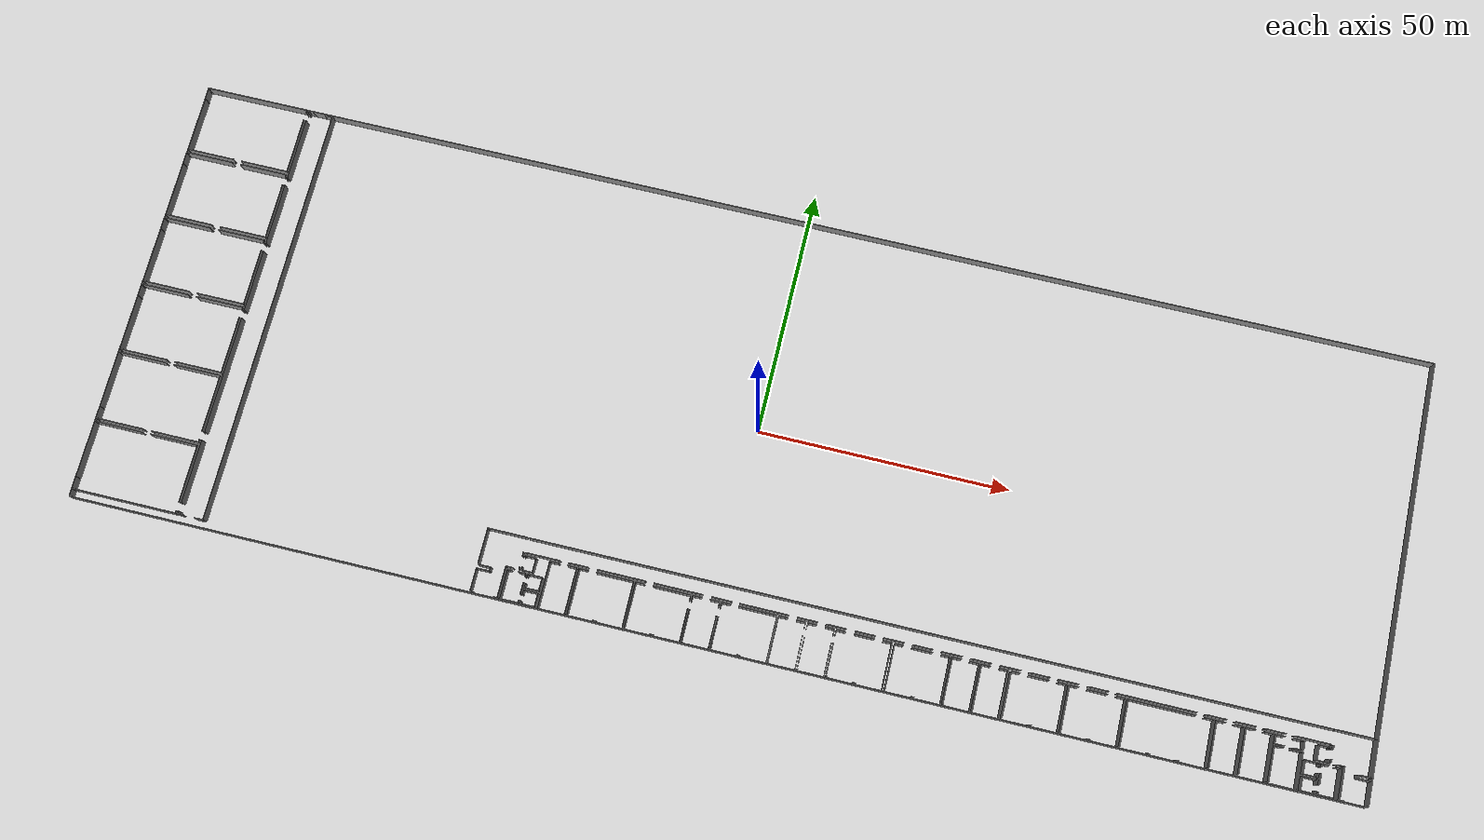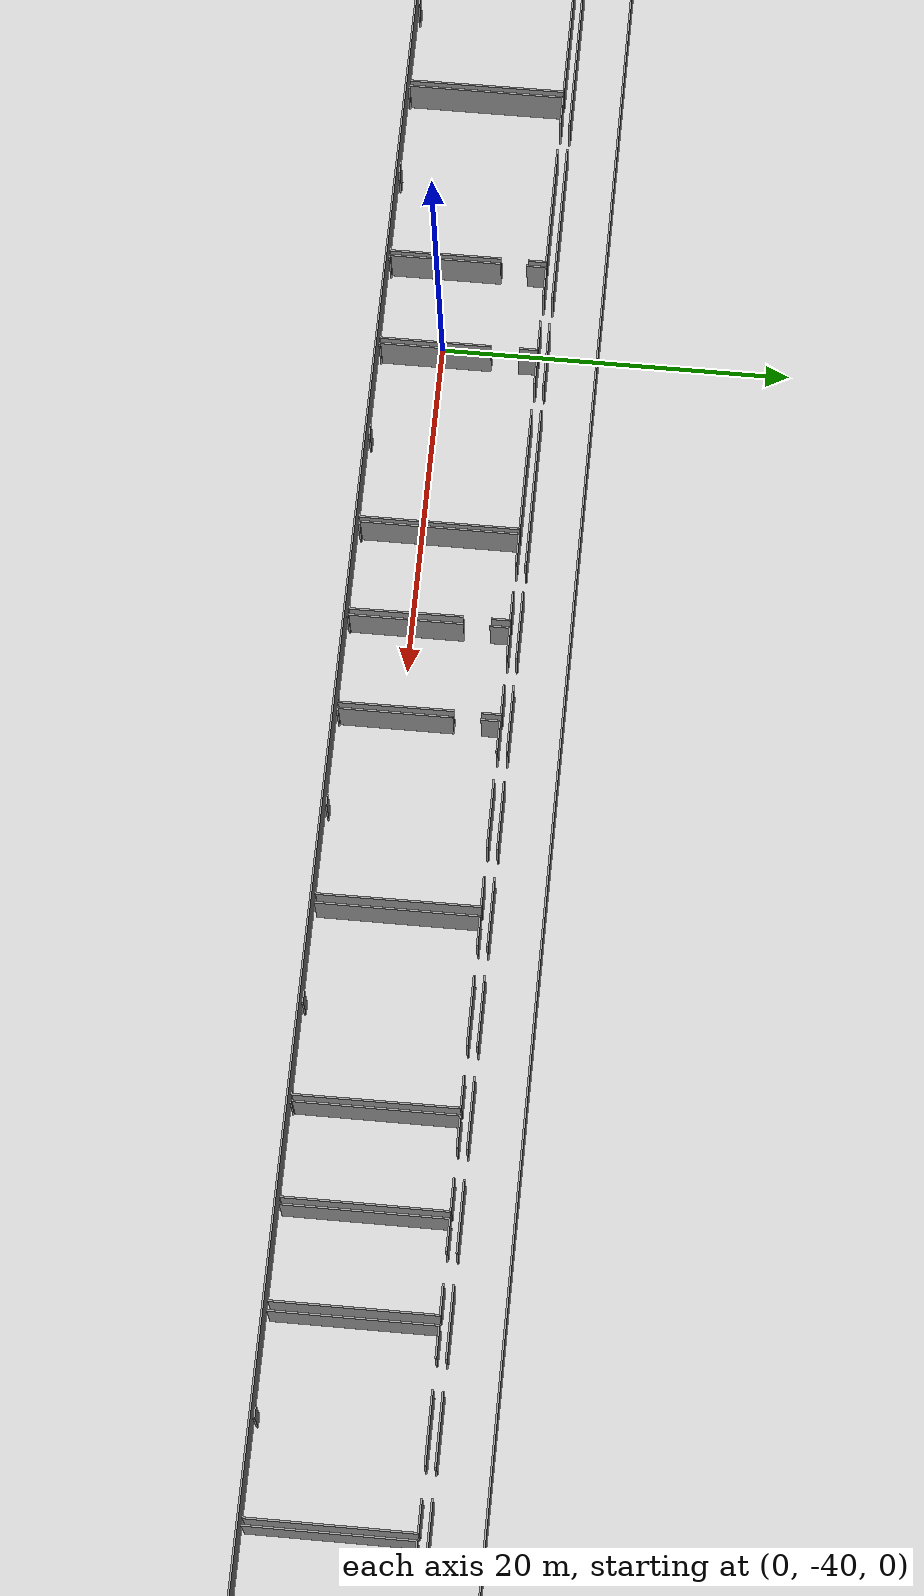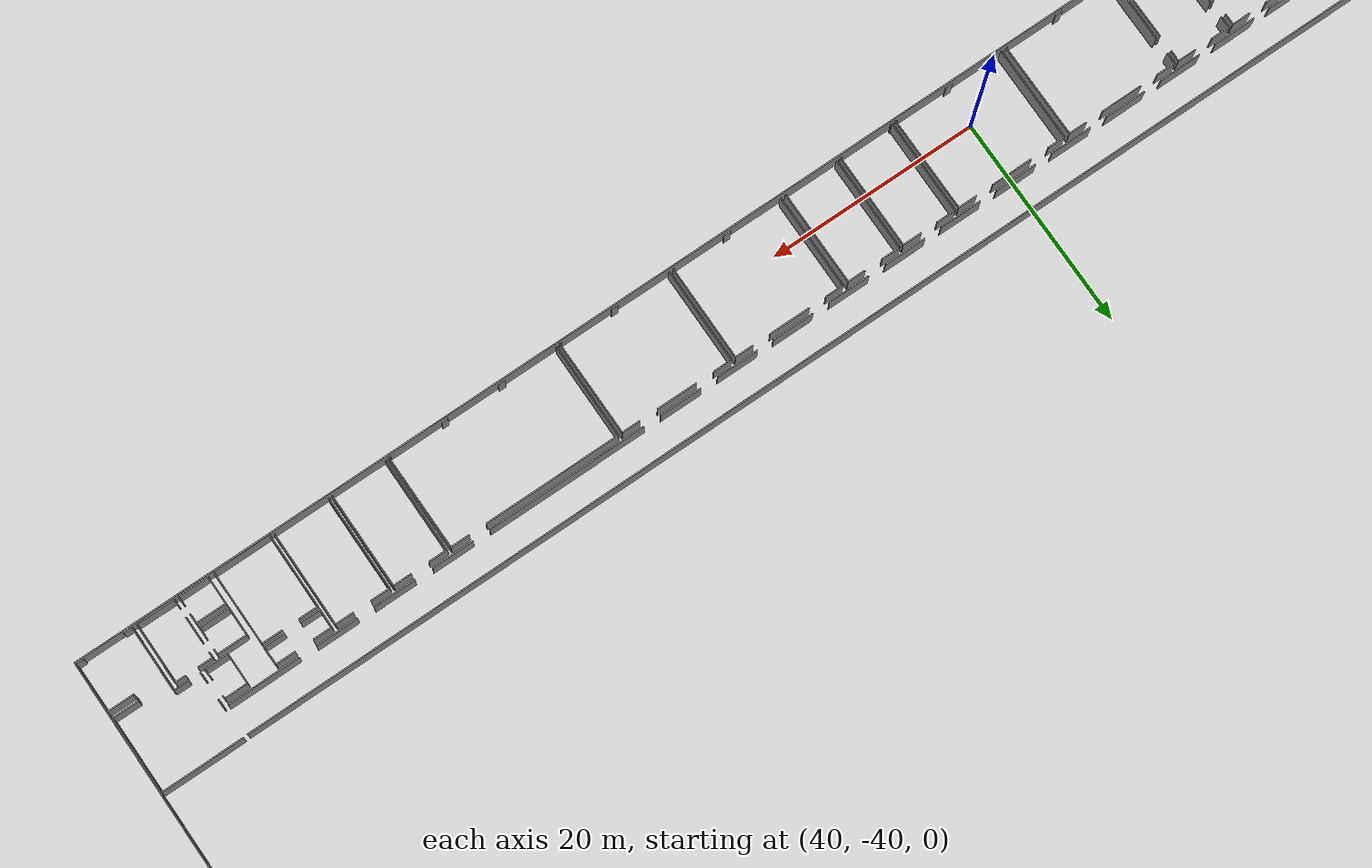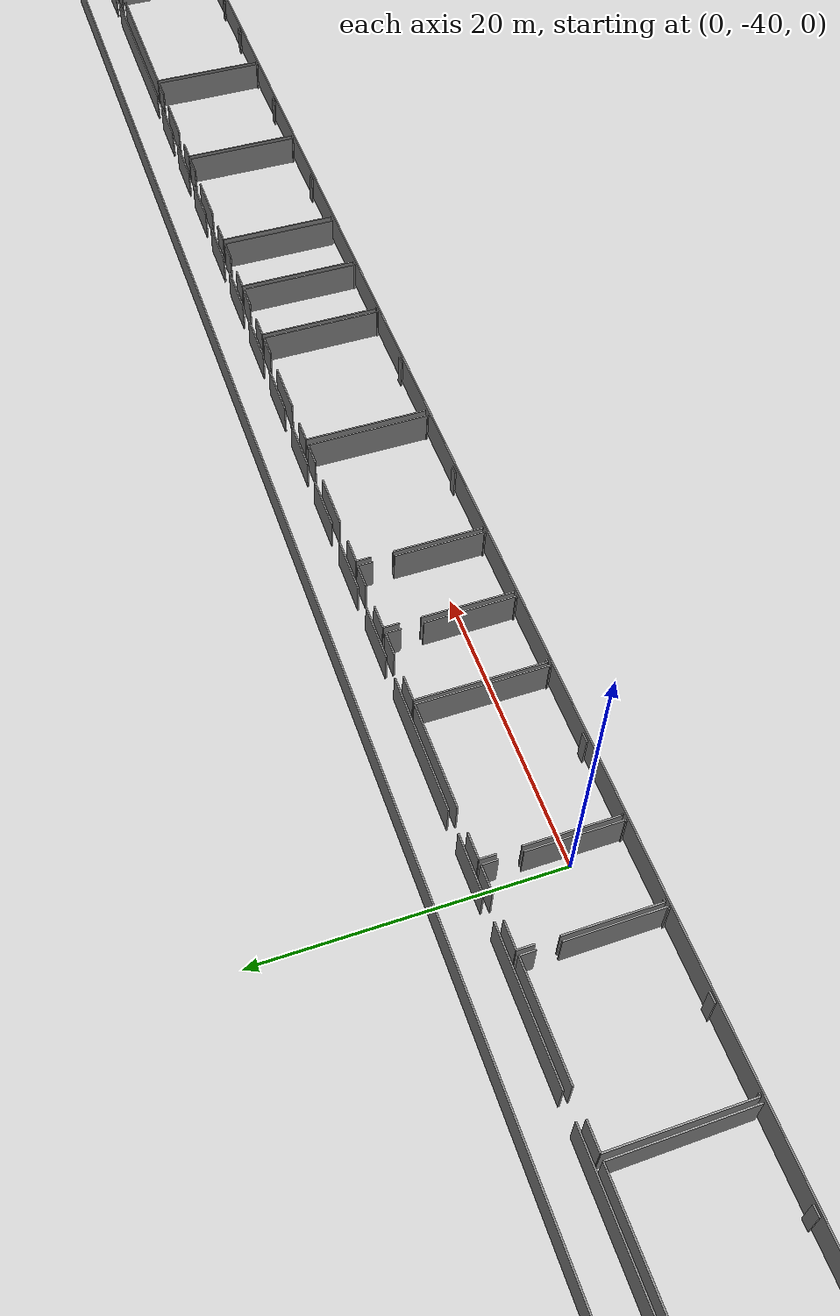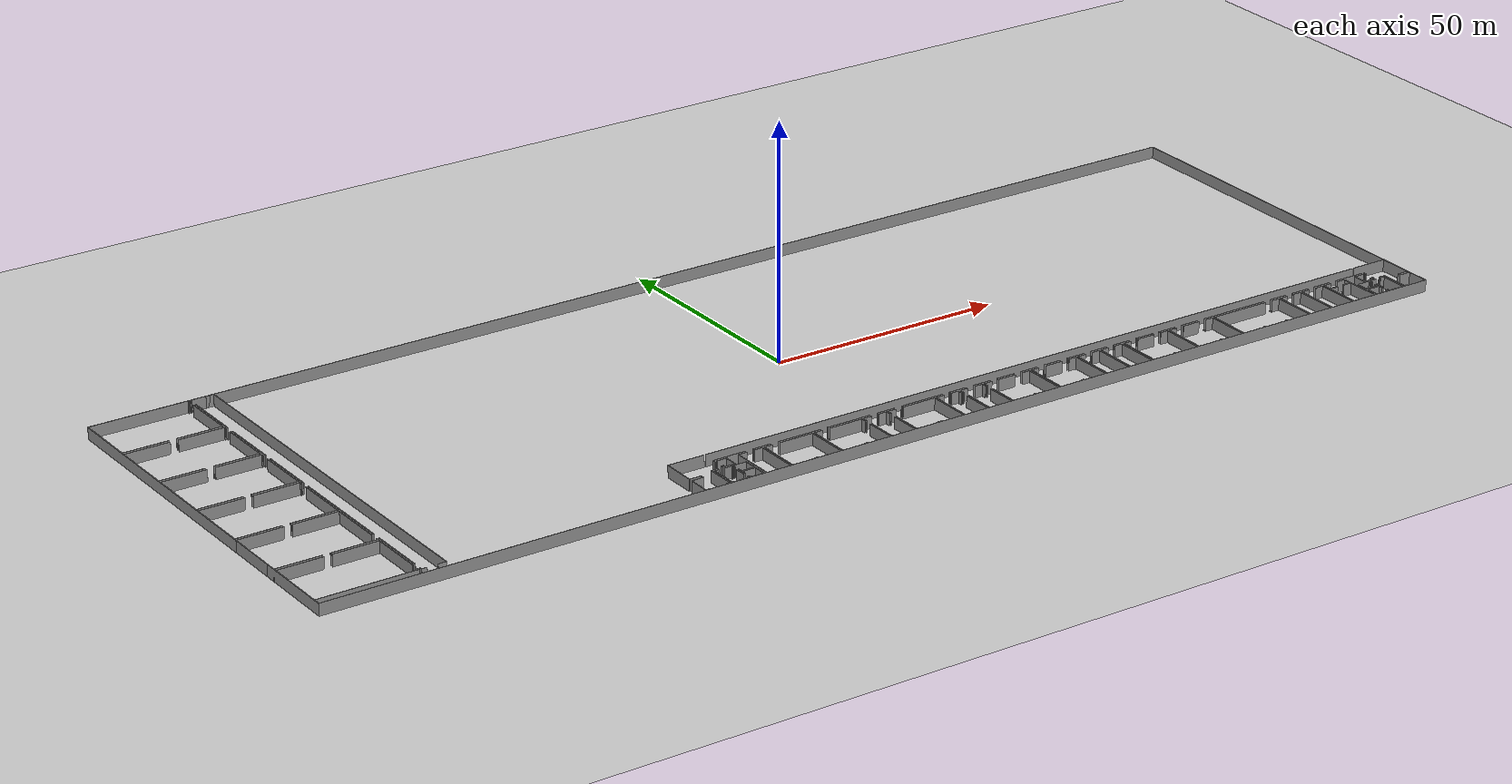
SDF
<sdf version="1.6">
  <world name="default">
    <light name="sun" type="directional">
      <cast_shadows>1</cast_shadows>
      <pose frame="">0 0 10 0 -0 0</pose>
      <diffuse>0.8 0.8 0.8 1</diffuse>
      <specular>0.1 0.1 0.1 1</specular>
      <attenuation>
        <range>1000</range>
        <constant>0.9</constant>
        <linear>0.01</linear>
        <quadratic>0.001</quadratic>
      </attenuation>
      <direction>-0.5 0.5 -1</direction>
    </light>
    <model name="ground_plane">
      <static>1</static>
      <link name="link">
        <collision name="collision">
          <geometry>
            <plane>
              <normal>0 0 1</normal>
              <size>100 100</size>
            </plane>
          </geometry>
          <surface>
            <friction>
              <ode>
                <mu>100</mu>
                <mu2>50</mu2>
              </ode>
              <torsional>
                <ode />
              </torsional>
            </friction>
            <contact>
              <ode />
            </contact>
            <bounce />
          </surface>
          <max_contacts>10</max_contacts>
        </collision>
        <visual name="visual">
          <cast_shadows>0</cast_shadows>
          <geometry>
            <plane>
              <normal>0 0 1</normal>
              <size>100 100</size>
            </plane>
          </geometry>
          <material>
            <script>
              <uri>file://media/materials/scripts/gazebo.material</uri>
              <name>Gazebo/Grey</name>
            </script>
          </material>
        </visual>
        <self_collide>0</self_collide>
        <kinematic>0</kinematic>
        <gravity>1</gravity>
      </link>
    </model>
    <gravity>0 0 -9.8</gravity>
    <magnetic_field>6e-06 2.3e-05 -4.2e-05</magnetic_field>
    <atmosphere type="adiabatic" />
    <physics default="0" name="default_physics" type="ode">
      <max_step_size>0.001</max_step_size>
      <real_time_factor>1</real_time_factor>
      <real_time_update_rate>1000</real_time_update_rate>
    </physics>
    <scene>
      <ambient>0.4 0.4 0.4 1</ambient>
      <background>0.7 0.7 0.7 1</background>
      <shadows>1</shadows>
    </scene>
    <spherical_coordinates>
      <surface_model>EARTH_WGS84</surface_model>
      <latitude_deg>0</latitude_deg>
      <longitude_deg>0</longitude_deg>
      <elevation>0</elevation>
      <heading_deg>0</heading_deg>
    </spherical_coordinates>
  <model name="50015849">
		<static>1</static>
		<link name="Wall_0">
			<collision name="Wall_0_Collision">
				<geometry>
					<box>
						<size>1.73699886325 0.1 2.5</size>
					</box>
				</geometry>
				<pose frame="">0.868499431627 0 1.25 0 0 0</pose>
			</collision>
			<visual name="Wall_0_Visual">
				<pose frame="">0.868499431627 0 1.25 0 0 0</pose>
				<geometry>
					<box>
						<size>1.73699886325 0.1 2.5</size>
					</box>
				</geometry>
				<material>
					<script>
						<uri>file://media/materials/scripts/gazebo.material</uri>
						<name>Gazebo/Grey</name>
					</script>
					<ambient>1 1 1 1</ambient>
				</material>
			</visual>
			<pose frame="">26.4807229451 -85.9171762973 0 0 0 3.14159265359</pose>
		</link>
		<link name="Wall_1">
			<collision name="Wall_1_Collision">
				<geometry>
					<box>
						<size>1.10931179231 0.1 2.5</size>
					</box>
				</geometry>
				<pose frame="">0.554655896156 0 1.25 0 0 0</pose>
			</collision>
			<visual name="Wall_1_Visual">
				<pose frame="">0.554655896156 0 1.25 0 0 0</pose>
				<geometry>
					<box>
						<size>1.10931179231 0.1 2.5</size>
					</box>
				</geometry>
				<material>
					<script>
						<uri>file://media/materials/scripts/gazebo.material</uri>
						<name>Gazebo/Grey</name>
					</script>
					<ambient>1 1 1 1</ambient>
				</material>
			</visual>
			<pose frame="">22.5347533134 -85.9171762973 0 0 0 3.14159265359</pose>
		</link>
		<link name="Wall_2">
			<collision name="Wall_2_Collision">
				<geometry>
					<box>
						<size>0.597712536595 0.1 2.5</size>
					</box>
				</geometry>
				<pose frame="">0.298856268297 0 1.25 0 0 0</pose>
			</collision>
			<visual name="Wall_2_Visual">
				<pose frame="">0.298856268297 0 1.25 0 0 0</pose>
				<geometry>
					<box>
						<size>0.597712536595 0.1 2.5</size>
					</box>
				</geometry>
				<material>
					<script>
						<uri>file://media/materials/scripts/gazebo.material</uri>
						<name>Gazebo/Grey</name>
					</script>
					<ambient>1 1 1 1</ambient>
				</material>
			</visual>
			<pose frame="">21.4254415211 -85.9171762973 0 0 0 1.57079632679</pose>
		</link>
		<link name="Wall_3">
			<collision name="Wall_3_Collision">
				<geometry>
					<box>
						<size>12.7940457366 0.1 2.5</size>
					</box>
				</geometry>
				<pose frame="">6.39702286828 0 1.25 0 0 0</pose>
			</collision>
			<visual name="Wall_3_Visual">
				<pose frame="">6.39702286828 0 1.25 0 0 0</pose>
				<geometry>
					<box>
						<size>12.7940457366 0.1 2.5</size>
					</box>
				</geometry>
				<material>
					<script>
						<uri>file://media/materials/scripts/gazebo.material</uri>
						<name>Gazebo/Grey</name>
					</script>
					<ambient>1 1 1 1</ambient>
				</material>
			</visual>
			<pose frame="">21.4254415211 -83.6957584764 0 0 0 1.57079632679</pose>
		</link>
		<link name="Wall_4">
			<collision name="Wall_4_Collision">
				<geometry>
					<box>
						<size>23.8416938152 0.1 2.5</size>
					</box>
				</geometry>
				<pose frame="">11.9208469076 0 1.25 0 0 0</pose>
			</collision>
			<visual name="Wall_4_Visual">
				<pose frame="">11.9208469076 0 1.25 0 0 0</pose>
				<geometry>
					<box>
						<size>23.8416938152 0.1 2.5</size>
					</box>
				</geometry>
				<material>
					<script>
						<uri>file://media/materials/scripts/gazebo.material</uri>
						<name>Gazebo/Grey</name>
					</script>
					<ambient>1 1 1 1</ambient>
				</material>
			</visual>
			<pose frame="">21.4254415211 -69.266576489 0 0 0 1.57079632679</pose>
		</link>
		<link name="Wall_5">
			<collision name="Wall_5_Collision">
				<geometry>
					<box>
						<size>12.8011583379 0.1 2.5</size>
					</box>
				</geometry>
				<pose frame="">6.40057916897 0 1.25 0 0 0</pose>
			</collision>
			<visual name="Wall_5_Visual">
				<pose frame="">6.40057916897 0 1.25 0 0 0</pose>
				<geometry>
					<box>
						<size>12.8011583379 0.1 2.5</size>
					</box>
				</geometry>
				<material>
					<script>
						<uri>file://media/materials/scripts/gazebo.material</uri>
						<name>Gazebo/Grey</name>
					</script>
					<ambient>1 1 1 1</ambient>
				</material>
			</visual>
			<pose frame="">21.4254415211 -43.81845085 0 0 0 1.57079632679</pose>
		</link>
		<link name="Wall_6">
			<collision name="Wall_6_Collision">
				<geometry>
					<box>
						<size>12.7688976103 0.1 2.5</size>
					</box>
				</geometry>
				<pose frame="">6.38444880515 0 1.25 0 0 0</pose>
			</collision>
			<visual name="Wall_6_Visual">
				<pose frame="">6.38444880515 0 1.25 0 0 0</pose>
				<geometry>
					<box>
						<size>12.7688976103 0.1 2.5</size>
					</box>
				</geometry>
				<material>
					<script>
						<uri>file://media/materials/scripts/gazebo.material</uri>
						<name>Gazebo/Grey</name>
					</script>
					<ambient>1 1 1 1</ambient>
				</material>
			</visual>
			<pose frame="">21.4254415211 -29.3879987553 0 0 0 1.57079632679</pose>
		</link>
		<link name="Wall_7">
			<collision name="Wall_7_Collision">
				<geometry>
					<box>
						<size>12.8303708079 0.1 2.5</size>
					</box>
				</geometry>
				<pose frame="">6.41518540393 0 1.25 0 0 0</pose>
			</collision>
			<visual name="Wall_7_Visual">
				<pose frame="">6.41518540393 0 1.25 0 0 0</pose>
				<geometry>
					<box>
						<size>12.8303708079 0.1 2.5</size>
					</box>
				</geometry>
				<material>
					<script>
						<uri>file://media/materials/scripts/gazebo.material</uri>
						<name>Gazebo/Grey</name>
					</script>
					<ambient>1 1 1 1</ambient>
				</material>
			</visual>
			<pose frame="">21.4254415211 -14.9684695841 0 0 0 1.57079632679</pose>
		</link>
		<link name="Wall_8">
			<collision name="Wall_8_Collision">
				<geometry>
					<box>
						<size>0.527094565846 0.1 2.5</size>
					</box>
				</geometry>
				<pose frame="">0.263547282923 0 1.25 0 0 0</pose>
			</collision>
			<visual name="Wall_8_Visual">
				<pose frame="">0.263547282923 0 1.25 0 0 0</pose>
				<geometry>
					<box>
						<size>0.527094565846 0.1 2.5</size>
					</box>
				</geometry>
				<material>
					<script>
						<uri>file://media/materials/scripts/gazebo.material</uri>
						<name>Gazebo/Grey</name>
					</script>
					<ambient>1 1 1 1</ambient>
				</material>
			</visual>
			<pose frame="">21.4254415211 -0.527094565846 0 0 0 1.57079632679</pose>
		</link>
		<link name="Wall_9">
			<collision name="Wall_9_Collision">
				<geometry>
					<box>
						<size>1.0653660767 0.1 2.5</size>
					</box>
				</geometry>
				<pose frame="">0.532683038351 0 1.25 0 0 0</pose>
			</collision>
			<visual name="Wall_9_Visual">
				<pose frame="">0.532683038351 0 1.25 0 0 0</pose>
				<geometry>
					<box>
						<size>1.0653660767 0.1 2.5</size>
					</box>
				</geometry>
				<material>
					<script>
						<uri>file://media/materials/scripts/gazebo.material</uri>
						<name>Gazebo/Grey</name>
					</script>
					<ambient>1 1 1 1</ambient>
				</material>
			</visual>
			<pose frame="">21.4254415211 -0.0 0 0 0 0.0</pose>
		</link>
		<link name="Wall_10">
			<collision name="Wall_10_Collision">
				<geometry>
					<box>
						<size>1.70219792083 0.1 2.5</size>
					</box>
				</geometry>
				<pose frame="">0.851098960417 0 1.25 0 0 0</pose>
			</collision>
			<visual name="Wall_10_Visual">
				<pose frame="">0.851098960417 0 1.25 0 0 0</pose>
				<geometry>
					<box>
						<size>1.70219792083 0.1 2.5</size>
					</box>
				</geometry>
				<material>
					<script>
						<uri>file://media/materials/scripts/gazebo.material</uri>
						<name>Gazebo/Grey</name>
					</script>
					<ambient>1 1 1 1</ambient>
				</material>
			</visual>
			<pose frame="">24.7091771609 -0.0 0 0 0 0.0</pose>
		</link>
		<link name="Wall_11">
			<collision name="Wall_11_Collision">
				<geometry>
					<box>
						<size>85.9172042842 0.1 2.5</size>
					</box>
				</geometry>
				<pose frame="">42.9586021421 0 1.25 0 0 0</pose>
			</collision>
			<visual name="Wall_11_Visual">
				<pose frame="">42.9586021421 0 1.25 0 0 0</pose>
				<geometry>
					<box>
						<size>85.9172042842 0.1 2.5</size>
					</box>
				</geometry>
				<material>
					<script>
						<uri>file://media/materials/scripts/gazebo.material</uri>
						<name>Gazebo/Grey</name>
					</script>
					<ambient>1 1 1 1</ambient>
				</material>
			</visual>
			<pose frame="">26.4113750818 -0.0 0 0 0 -1.56998917913</pose>
		</link>
		<link name="Wall_12">
			<collision name="Wall_12_Collision">
				<geometry>
					<box>
						<size>9.66602526244 0.1 2.5</size>
					</box>
				</geometry>
				<pose frame="">4.83301263122 0 1.25 0 0 0</pose>
			</collision>
			<visual name="Wall_12_Visual">
				<pose frame="">4.83301263122 0 1.25 0 0 0</pose>
				<geometry>
					<box>
						<size>9.66602526244 0.1 2.5</size>
					</box>
				</geometry>
				<material>
					<script>
						<uri>file://media/materials/scripts/gazebo.material</uri>
						<name>Gazebo/Grey</name>
					</script>
					<ambient>1 1 1 1</ambient>
				</material>
			</visual>
			<pose frame="">20.9521995085 -13.7463722558 0 0 0 3.14159265359</pose>
		</link>
		<link name="Wall_13">
			<collision name="Wall_13_Collision">
				<geometry>
					<box>
						<size>9.59820152794 0.1 2.5</size>
					</box>
				</geometry>
				<pose frame="">4.79910076397 0 1.25 0 0 0</pose>
			</collision>
			<visual name="Wall_13_Visual">
				<pose frame="">4.79910076397 0 1.25 0 0 0</pose>
				<geometry>
					<box>
						<size>9.59820152794 0.1 2.5</size>
					</box>
				</geometry>
				<material>
					<script>
						<uri>file://media/materials/scripts/gazebo.material</uri>
						<name>Gazebo/Grey</name>
					</script>
					<ambient>1 1 1 1</ambient>
				</material>
			</visual>
			<pose frame="">9.66145287584 -13.7463722558 0 0 0 3.14159265359</pose>
		</link>
		<link name="Wall_14">
			<collision name="Wall_14_Collision">
				<geometry>
					<box>
						<size>11.3191970381 0.1 2.5</size>
					</box>
				</geometry>
				<pose frame="">5.65959851905 0 1.25 0 0 0</pose>
			</collision>
			<visual name="Wall_14_Visual">
				<pose frame="">5.65959851905 0 1.25 0 0 0</pose>
				<geometry>
					<box>
						<size>11.3191970381 0.1 2.5</size>
					</box>
				</geometry>
				<material>
					<script>
						<uri>file://media/materials/scripts/gazebo.material</uri>
						<name>Gazebo/Grey</name>
					</script>
					<ambient>1 1 1 1</ambient>
				</material>
			</visual>
			<pose frame="">0.0632513479015 -13.7463722558 0 0 0 1.57079632679</pose>
		</link>
		<link name="Wall_15">
			<collision name="Wall_15_Collision">
				<geometry>
					<box>
						<size>0.153682993897 0.1 2.5</size>
					</box>
				</geometry>
				<pose frame="">0.0768414969486 0 1.25 0 0 0</pose>
			</collision>
			<visual name="Wall_15_Visual">
				<pose frame="">0.0768414969486 0 1.25 0 0 0</pose>
				<geometry>
					<box>
						<size>0.153682993897 0.1 2.5</size>
					</box>
				</geometry>
				<material>
					<script>
						<uri>file://media/materials/scripts/gazebo.material</uri>
						<name>Gazebo/Grey</name>
					</script>
					<ambient>1 1 1 1</ambient>
				</material>
			</visual>
			<pose frame="">0.0632513479015 -0.175782862441 0 0 0 1.57079632679</pose>
		</link>
		<link name="Wall_16">
			<collision name="Wall_16_Collision">
				<geometry>
					<box>
						<size>20.855671347 0.1 2.5</size>
					</box>
				</geometry>
				<pose frame="">10.4278356735 0 1.25 0 0 0</pose>
			</collision>
			<visual name="Wall_16_Visual">
				<pose frame="">10.4278356735 0 1.25 0 0 0</pose>
				<geometry>
					<box>
						<size>20.855671347 0.1 2.5</size>
					</box>
				</geometry>
				<material>
					<script>
						<uri>file://media/materials/scripts/gazebo.material</uri>
						<name>Gazebo/Grey</name>
					</script>
					<ambient>1 1 1 1</ambient>
				</material>
			</visual>
			<pose frame="">0.0632513479015 -0.0220998685439 0 0 0 0.0</pose>
		</link>
		<link name="Wall_17">
			<collision name="Wall_17_Collision">
				<geometry>
					<box>
						<size>0.510075126852 0.1 2.5</size>
					</box>
				</geometry>
				<pose frame="">0.255037563426 0 1.25 0 0 0</pose>
			</collision>
			<visual name="Wall_17_Visual">
				<pose frame="">0.255037563426 0 1.25 0 0 0</pose>
				<geometry>
					<box>
						<size>0.510075126852 0.1 2.5</size>
					</box>
				</geometry>
				<material>
					<script>
						<uri>file://media/materials/scripts/gazebo.material</uri>
						<name>Gazebo/Grey</name>
					</script>
					<ambient>1 1 1 1</ambient>
				</material>
			</visual>
			<pose frame="">20.9189226949 -0.0220998685439 0 0 0 -1.57079632679</pose>
		</link>
		<link name="Wall_18">
			<collision name="Wall_18_Collision">
				<geometry>
					<box>
						<size>11.5699640909 0.1 2.5</size>
					</box>
				</geometry>
				<pose frame="">5.78498204544 0 1.25 0 0 0</pose>
			</collision>
			<visual name="Wall_18_Visual">
				<pose frame="">5.78498204544 0 1.25 0 0 0</pose>
				<geometry>
					<box>
						<size>11.5699640909 0.1 2.5</size>
					</box>
				</geometry>
				<material>
					<script>
						<uri>file://media/materials/scripts/gazebo.material</uri>
						<name>Gazebo/Grey</name>
					</script>
					<ambient>1 1 1 1</ambient>
				</material>
			</visual>
			<pose frame="">20.9189226949 -2.17645601936 0 0 0 -1.56792018481</pose>
		</link>
		<link name="Wall_19">
			<collision name="Wall_19_Collision">
				<geometry>
					<box>
						<size>9.63655877104 0.1 2.5</size>
					</box>
				</geometry>
				<pose frame="">4.81827938552 0 1.25 0 0 0</pose>
			</collision>
			<visual name="Wall_19_Visual">
				<pose frame="">4.81827938552 0 1.25 0 0 0</pose>
				<geometry>
					<box>
						<size>9.63655877104 0.1 2.5</size>
					</box>
				</geometry>
				<material>
					<script>
						<uri>file://media/materials/scripts/gazebo.material</uri>
						<name>Gazebo/Grey</name>
					</script>
					<ambient>1 1 1 1</ambient>
				</material>
			</visual>
			<pose frame="">20.9313697473 -28.1798726082 0 0 0 3.14159265359</pose>
		</link>
		<link name="Wall_20">
			<collision name="Wall_20_Collision">
				<geometry>
					<box>
						<size>9.62055541796 0.1 2.5</size>
					</box>
				</geometry>
				<pose frame="">4.81027770898 0 1.25 0 0 0</pose>
			</collision>
			<visual name="Wall_20_Visual">
				<pose frame="">4.81027770898 0 1.25 0 0 0</pose>
				<geometry>
					<box>
						<size>9.62055541796 0.1 2.5</size>
					</box>
				</geometry>
				<material>
					<script>
						<uri>file://media/materials/scripts/gazebo.material</uri>
						<name>Gazebo/Grey</name>
					</script>
					<ambient>1 1 1 1</ambient>
				</material>
			</visual>
			<pose frame="">9.66145287584 -28.1798726082 0 0 0 3.14159265359</pose>
		</link>
		<link name="Wall_21">
			<collision name="Wall_21_Collision">
				<geometry>
					<box>
						<size>11.2993833629 0.1 2.5</size>
					</box>
				</geometry>
				<pose frame="">5.64969168143 0 1.25 0 0 0</pose>
			</collision>
			<visual name="Wall_21_Visual">
				<pose frame="">5.64969168143 0 1.25 0 0 0</pose>
				<geometry>
					<box>
						<size>11.2993833629 0.1 2.5</size>
					</box>
				</geometry>
				<material>
					<script>
						<uri>file://media/materials/scripts/gazebo.material</uri>
						<name>Gazebo/Grey</name>
					</script>
					<ambient>1 1 1 1</ambient>
				</material>
			</visual>
			<pose frame="">0.0408974578801 -28.1798726082 0 0 0 1.57079632679</pose>
		</link>
		<link name="Wall_22">
			<collision name="Wall_22_Collision">
				<geometry>
					<box>
						<size>0.153682993897 0.1 2.5</size>
					</box>
				</geometry>
				<pose frame="">0.0768414969486 0 1.25 0 0 0</pose>
			</collision>
			<visual name="Wall_22_Visual">
				<pose frame="">0.0768414969486 0 1.25 0 0 0</pose>
				<geometry>
					<box>
						<size>0.153682993897 0.1 2.5</size>
					</box>
				</geometry>
				<material>
					<script>
						<uri>file://media/materials/scripts/gazebo.material</uri>
						<name>Gazebo/Grey</name>
					</script>
					<ambient>1 1 1 1</ambient>
				</material>
			</visual>
			<pose frame="">0.0408974578801 -14.5948039907 0 0 0 1.57079632679</pose>
		</link>
		<link name="Wall_23">
			<collision name="Wall_23_Collision">
				<geometry>
					<box>
						<size>9.58727860441 0.1 2.5</size>
					</box>
				</geometry>
				<pose frame="">4.7936393022 0 1.25 0 0 0</pose>
			</collision>
			<visual name="Wall_23_Visual">
				<pose frame="">4.7936393022 0 1.25 0 0 0</pose>
				<geometry>
					<box>
						<size>9.58727860441 0.1 2.5</size>
					</box>
				</geometry>
				<material>
					<script>
						<uri>file://media/materials/scripts/gazebo.material</uri>
						<name>Gazebo/Grey</name>
					</script>
					<ambient>1 1 1 1</ambient>
				</material>
			</visual>
			<pose frame="">0.0408974578801 -14.4411209968 0 0 0 0.0</pose>
		</link>
		<link name="Wall_24">
			<collision name="Wall_24_Collision">
				<geometry>
					<box>
						<size>9.63605072809 0.1 2.5</size>
					</box>
				</geometry>
				<pose frame="">4.81802536404 0 1.25 0 0 0</pose>
			</collision>
			<visual name="Wall_24_Visual">
				<pose frame="">4.81802536404 0 1.25 0 0 0</pose>
				<geometry>
					<box>
						<size>9.63605072809 0.1 2.5</size>
					</box>
				</geometry>
				<material>
					<script>
						<uri>file://media/materials/scripts/gazebo.material</uri>
						<name>Gazebo/Grey</name>
					</script>
					<ambient>1 1 1 1</ambient>
				</material>
			</visual>
			<pose frame="">11.2907466326 -14.4411209968 0 0 0 0.0</pose>
		</link>
		<link name="Wall_25">
			<collision name="Wall_25_Collision">
				<geometry>
					<box>
						<size>0.498390138886 0.1 2.5</size>
					</box>
				</geometry>
				<pose frame="">0.249195069443 0 1.25 0 0 0</pose>
			</collision>
			<visual name="Wall_25_Visual">
				<pose frame="">0.249195069443 0 1.25 0 0 0</pose>
				<geometry>
					<box>
						<size>0.498390138886 0.1 2.5</size>
					</box>
				</geometry>
				<material>
					<script>
						<uri>file://media/materials/scripts/gazebo.material</uri>
						<name>Gazebo/Grey</name>
					</script>
					<ambient>1 1 1 1</ambient>
				</material>
			</visual>
			<pose frame="">20.9267973607 -14.4411209968 0 0 0 -1.57079632679</pose>
		</link>
		<link name="Wall_26">
			<collision name="Wall_26_Collision">
				<geometry>
					<box>
						<size>11.5490873804 0.1 2.5</size>
					</box>
				</geometry>
				<pose frame="">5.77454369019 0 1.25 0 0 0</pose>
			</collision>
			<visual name="Wall_26_Visual">
				<pose frame="">5.77454369019 0 1.25 0 0 0</pose>
				<geometry>
					<box>
						<size>11.5490873804 0.1 2.5</size>
					</box>
				</geometry>
				<material>
					<script>
						<uri>file://media/materials/scripts/gazebo.material</uri>
						<name>Gazebo/Grey</name>
					</script>
					<ambient>1 1 1 1</ambient>
				</material>
			</visual>
			<pose frame="">20.9267973607 -16.630786133 0 0 0 -1.57040041787</pose>
		</link>
		<link name="Wall_27">
			<collision name="Wall_27_Collision">
				<geometry>
					<box>
						<size>9.68456883029 0.1 2.5</size>
					</box>
				</geometry>
				<pose frame="">4.84228441515 0 1.25 0 0 0</pose>
			</collision>
			<visual name="Wall_27_Visual">
				<pose frame="">4.84228441515 0 1.25 0 0 0</pose>
				<geometry>
					<box>
						<size>9.68456883029 0.1 2.5</size>
					</box>
				</geometry>
				<material>
					<script>
						<uri>file://media/materials/scripts/gazebo.material</uri>
						<name>Gazebo/Grey</name>
					</script>
					<ambient>1 1 1 1</ambient>
				</material>
			</visual>
			<pose frame="">20.9521995085 -42.5978776506 0 0 0 3.14159265359</pose>
		</link>
		<link name="Wall_28">
			<collision name="Wall_28_Collision">
				<geometry>
					<box>
						<size>9.58042002451 0.1 2.5</size>
					</box>
				</geometry>
				<pose frame="">4.79021001226 0 1.25 0 0 0</pose>
			</collision>
			<visual name="Wall_28_Visual">
				<pose frame="">4.79021001226 0 1.25 0 0 0</pose>
				<geometry>
					<box>
						<size>9.58042002451 0.1 2.5</size>
					</box>
				</geometry>
				<material>
					<script>
						<uri>file://media/materials/scripts/gazebo.material</uri>
						<name>Gazebo/Grey</name>
					</script>
					<ambient>1 1 1 1</ambient>
				</material>
			</visual>
			<pose frame="">9.64163920059 -42.5978776506 0 0 0 3.14159265359</pose>
		</link>
		<link name="Wall_29">
			<collision name="Wall_29_Collision">
				<geometry>
					<box>
						<size>11.275505344 0.1 2.5</size>
					</box>
				</geometry>
				<pose frame="">5.63775267199 0 1.25 0 0 0</pose>
			</collision>
			<visual name="Wall_29_Visual">
				<pose frame="">5.63775267199 0 1.25 0 0 0</pose>
				<geometry>
					<box>
						<size>11.275505344 0.1 2.5</size>
					</box>
				</geometry>
				<material>
					<script>
						<uri>file://media/materials/scripts/gazebo.material</uri>
						<name>Gazebo/Grey</name>
					</script>
					<ambient>1 1 1 1</ambient>
				</material>
			</visual>
			<pose frame="">0.0612191760813 -42.5978776506 0 0 0 1.57079632679</pose>
		</link>
		<link name="Wall_30">
			<collision name="Wall_30_Collision">
				<geometry>
					<box>
						<size>0.143268113319 0.1 2.5</size>
					</box>
				</geometry>
				<pose frame="">0.0716340566595 0 1.25 0 0 0</pose>
			</collision>
			<visual name="Wall_30_Visual">
				<pose frame="">0.0716340566595 0 1.25 0 0 0</pose>
				<geometry>
					<box>
						<size>0.143268113319 0.1 2.5</size>
					</box>
				</geometry>
				<material>
					<script>
						<uri>file://media/materials/scripts/gazebo.material</uri>
						<name>Gazebo/Grey</name>
					</script>
					<ambient>1 1 1 1</ambient>
				</material>
			</visual>
			<pose frame="">0.0612191760813 -29.0084906679 0 0 0 1.57079632679</pose>
		</link>
		<link name="Wall_31">
			<collision name="Wall_31_Collision">
				<geometry>
					<box>
						<size>9.55425581233 0.1 2.5</size>
					</box>
				</geometry>
				<pose frame="">4.77712790616 0 1.25 0 0 0</pose>
			</collision>
			<visual name="Wall_31_Visual">
				<pose frame="">4.77712790616 0 1.25 0 0 0</pose>
				<geometry>
					<box>
						<size>9.55425581233 0.1 2.5</size>
					</box>
				</geometry>
				<material>
					<script>
						<uri>file://media/materials/scripts/gazebo.material</uri>
						<name>Gazebo/Grey</name>
					</script>
					<ambient>1 1 1 1</ambient>
				</material>
			</visual>
			<pose frame="">0.0612191760813 -28.8652225546 0 0 0 0.0</pose>
		</link>
		<link name="Wall_32">
			<collision name="Wall_32_Collision">
				<geometry>
					<box>
						<size>9.64367137241 0.1 2.5</size>
					</box>
				</geometry>
				<pose frame="">4.82183568621 0 1.25 0 0 0</pose>
			</collision>
			<visual name="Wall_32_Visual">
				<pose frame="">4.82183568621 0 1.25 0 0 0</pose>
				<geometry>
					<box>
						<size>9.64367137241 0.1 2.5</size>
					</box>
				</geometry>
				<material>
					<script>
						<uri>file://media/materials/scripts/gazebo.material</uri>
						<name>Gazebo/Grey</name>
					</script>
					<ambient>1 1 1 1</ambient>
				</material>
			</visual>
			<pose frame="">11.2737271936 -28.8652225546 0 0 0 0.0</pose>
		</link>
		<link name="Wall_33">
			<collision name="Wall_33_Collision">
				<geometry>
					<box>
						<size>0.510837191285 0.1 2.5</size>
					</box>
				</geometry>
				<pose frame="">0.255418595642 0 1.25 0 0 0</pose>
			</collision>
			<visual name="Wall_33_Visual">
				<pose frame="">0.255418595642 0 1.25 0 0 0</pose>
				<geometry>
					<box>
						<size>0.510837191285 0.1 2.5</size>
					</box>
				</geometry>
				<material>
					<script>
						<uri>file://media/materials/scripts/gazebo.material</uri>
						<name>Gazebo/Grey</name>
					</script>
					<ambient>1 1 1 1</ambient>
				</material>
			</visual>
			<pose frame="">20.917398566 -28.8652225546 0 0 0 -1.57079632679</pose>
		</link>
		<link name="Wall_34">
			<collision name="Wall_34_Collision">
				<geometry>
					<box>
						<size>11.5951165876 0.1 2.5</size>
					</box>
				</geometry>
				<pose frame="">5.79755829381 0 1.25 0 0 0</pose>
			</collision>
			<visual name="Wall_34_Visual">
				<pose frame="">5.79755829381 0 1.25 0 0 0</pose>
				<geometry>
					<box>
						<size>11.5951165876 0.1 2.5</size>
					</box>
				</geometry>
				<material>
					<script>
						<uri>file://media/materials/scripts/gazebo.material</uri>
						<name>Gazebo/Grey</name>
					</script>
					<ambient>1 1 1 1</ambient>
				</material>
			</visual>
			<pose frame="">20.917398566 -31.0028132879 0 0 0 -1.56779497753</pose>
		</link>
		<link name="Wall_35">
			<collision name="Wall_35_Collision">
				<geometry>
					<box>
						<size>9.66145287584 0.1 2.5</size>
					</box>
				</geometry>
				<pose frame="">4.83072643792 0 1.25 0 0 0</pose>
			</collision>
			<visual name="Wall_35_Visual">
				<pose frame="">4.83072643792 0 1.25 0 0 0</pose>
				<geometry>
					<box>
						<size>9.66145287584 0.1 2.5</size>
					</box>
				</geometry>
				<material>
					<script>
						<uri>file://media/materials/scripts/gazebo.material</uri>
						<name>Gazebo/Grey</name>
					</script>
					<ambient>1 1 1 1</ambient>
				</material>
			</visual>
			<pose frame="">20.9438167997 -57.0628766662 0 0 0 3.14159265359</pose>
		</link>
		<link name="Wall_36">
			<collision name="Wall_36_Collision">
				<geometry>
					<box>
						<size>9.66145287584 0.1 2.5</size>
					</box>
				</geometry>
				<pose frame="">4.83072643792 0 1.25 0 0 0</pose>
			</collision>
			<visual name="Wall_36_Visual">
				<pose frame="">4.83072643792 0 1.25 0 0 0</pose>
				<geometry>
					<box>
						<size>9.66145287584 0.1 2.5</size>
					</box>
				</geometry>
				<material>
					<script>
						<uri>file://media/materials/scripts/gazebo.material</uri>
						<name>Gazebo/Grey</name>
					</script>
					<ambient>1 1 1 1</ambient>
				</material>
			</visual>
			<pose frame="">9.71200314987 -57.0628766662 0 0 0 3.14159265359</pose>
		</link>
		<link name="Wall_37">
			<collision name="Wall_37_Collision">
				<geometry>
					<box>
						<size>11.3329141979 0.1 2.5</size>
					</box>
				</geometry>
				<pose frame="">5.66645709895 0 1.25 0 0 0</pose>
			</collision>
			<visual name="Wall_37_Visual">
				<pose frame="">5.66645709895 0 1.25 0 0 0</pose>
				<geometry>
					<box>
						<size>11.3329141979 0.1 2.5</size>
					</box>
				</geometry>
				<material>
					<script>
						<uri>file://media/materials/scripts/gazebo.material</uri>
						<name>Gazebo/Grey</name>
					</script>
					<ambient>1 1 1 1</ambient>
				</material>
			</visual>
			<pose frame="">0.0505502740257 -57.0628766662 0 0 0 1.57079632679</pose>
		</link>
		<link name="Wall_38">
			<collision name="Wall_38_Collision">
				<geometry>
					<box>
						<size>0.203217182013 0.1 2.5</size>
					</box>
				</geometry>
				<pose frame="">0.101608591006 0 1.25 0 0 0</pose>
			</collision>
			<visual name="Wall_38_Visual">
				<pose frame="">0.101608591006 0 1.25 0 0 0</pose>
				<geometry>
					<box>
						<size>0.203217182013 0.1 2.5</size>
					</box>
				</geometry>
				<material>
					<script>
						<uri>file://media/materials/scripts/gazebo.material</uri>
						<name>Gazebo/Grey</name>
					</script>
					<ambient>1 1 1 1</ambient>
				</material>
			</visual>
			<pose frame="">0.0505502740257 -43.4785701131 0 0 0 1.57079632679</pose>
		</link>
		<link name="Wall_39">
			<collision name="Wall_39_Collision">
				<geometry>
					<box>
						<size>9.55273168346 0.1 2.5</size>
					</box>
				</geometry>
				<pose frame="">4.77636584173 0 1.25 0 0 0</pose>
			</collision>
			<visual name="Wall_39_Visual">
				<pose frame="">4.77636584173 0 1.25 0 0 0</pose>
				<geometry>
					<box>
						<size>9.55273168346 0.1 2.5</size>
					</box>
				</geometry>
				<material>
					<script>
						<uri>file://media/materials/scripts/gazebo.material</uri>
						<name>Gazebo/Grey</name>
					</script>
					<ambient>1 1 1 1</ambient>
				</material>
			</visual>
			<pose frame="">0.0505502740257 -43.2753529311 0 0 0 0.0</pose>
		</link>
		<link name="Wall_40">
			<collision name="Wall_40_Collision">
				<geometry>
					<box>
						<size>9.65408625299 0.1 2.5</size>
					</box>
				</geometry>
				<pose frame="">4.8270431265 0 1.25 0 0 0</pose>
			</collision>
			<visual name="Wall_40_Visual">
				<pose frame="">4.8270431265 0 1.25 0 0 0</pose>
				<geometry>
					<box>
						<size>9.65408625299 0.1 2.5</size>
					</box>
				</geometry>
				<material>
					<script>
						<uri>file://media/materials/scripts/gazebo.material</uri>
						<name>Gazebo/Grey</name>
					</script>
					<ambient>1 1 1 1</ambient>
				</material>
			</visual>
			<pose frame="">11.2816018594 -43.2753529311 0 0 0 0.0</pose>
		</link>
		<link name="Wall_41">
			<collision name="Wall_41_Collision">
				<geometry>
					<box>
						<size>0.51845783561 0.1 2.5</size>
					</box>
				</geometry>
				<pose frame="">0.259228917805 0 1.25 0 0 0</pose>
			</collision>
			<visual name="Wall_41_Visual">
				<pose frame="">0.259228917805 0 1.25 0 0 0</pose>
				<geometry>
					<box>
						<size>0.51845783561 0.1 2.5</size>
					</box>
				</geometry>
				<material>
					<script>
						<uri>file://media/materials/scripts/gazebo.material</uri>
						<name>Gazebo/Grey</name>
					</script>
					<ambient>1 1 1 1</ambient>
				</material>
			</visual>
			<pose frame="">20.9356881124 -43.2753529311 0 0 0 -1.57079632679</pose>
		</link>
		<link name="Wall_42">
			<collision name="Wall_42_Collision">
				<geometry>
					<box>
						<size>11.6204693535 0.1 2.5</size>
					</box>
				</geometry>
				<pose frame="">5.81023467676 0 1.25 0 0 0</pose>
			</collision>
			<visual name="Wall_42_Visual">
				<pose frame="">5.81023467676 0 1.25 0 0 0</pose>
				<geometry>
					<box>
						<size>11.6204693535 0.1 2.5</size>
					</box>
				</geometry>
				<material>
					<script>
						<uri>file://media/materials/scripts/gazebo.material</uri>
						<name>Gazebo/Grey</name>
					</script>
					<ambient>1 1 1 1</ambient>
				</material>
			</visual>
			<pose frame="">20.9356881124 -45.4424101558 0 0 0 -1.5700968122</pose>
		</link>
		<link name="Wall_43">
			<collision name="Wall_43_Collision">
				<geometry>
					<box>
						<size>9.63655877104 0.1 2.5</size>
					</box>
				</geometry>
				<pose frame="">4.81827938552 0 1.25 0 0 0</pose>
			</collision>
			<visual name="Wall_43_Visual">
				<pose frame="">4.81827938552 0 1.25 0 0 0</pose>
				<geometry>
					<box>
						<size>9.63655877104 0.1 2.5</size>
					</box>
				</geometry>
				<material>
					<script>
						<uri>file://media/materials/scripts/gazebo.material</uri>
						<name>Gazebo/Grey</name>
					</script>
					<ambient>1 1 1 1</ambient>
				</material>
			</visual>
			<pose frame="">20.9247651889 -71.4879943099 0 0 0 3.14159265359</pose>
		</link>
		<link name="Wall_44">
			<collision name="Wall_44_Collision">
				<geometry>
					<box>
						<size>9.67415394972 0.1 2.5</size>
					</box>
				</geometry>
				<pose frame="">4.83707697486 0 1.25 0 0 0</pose>
			</collision>
			<visual name="Wall_44_Visual">
				<pose frame="">4.83707697486 0 1.25 0 0 0</pose>
				<geometry>
					<box>
						<size>9.67415394972 0.1 2.5</size>
					</box>
				</geometry>
				<material>
					<script>
						<uri>file://media/materials/scripts/gazebo.material</uri>
						<name>Gazebo/Grey</name>
					</script>
					<ambient>1 1 1 1</ambient>
				</material>
			</visual>
			<pose frame="">9.67415394972 -71.4879943099 0 0 0 3.14159265359</pose>
		</link>
		<link name="Wall_45">
			<collision name="Wall_45_Collision">
				<geometry>
					<box>
						<size>0.15850940197 0.1 2.5</size>
					</box>
				</geometry>
				<pose frame="">0.079254700985 0 1.25 0 0 0</pose>
			</collision>
			<visual name="Wall_45_Visual">
				<pose frame="">0.079254700985 0 1.25 0 0 0</pose>
				<geometry>
					<box>
						<size>0.15850940197 0.1 2.5</size>
					</box>
				</geometry>
				<material>
					<script>
						<uri>file://media/materials/scripts/gazebo.material</uri>
						<name>Gazebo/Grey</name>
					</script>
					<ambient>1 1 1 1</ambient>
				</material>
			</visual>
			<pose frame="">0.0 -71.4879943099 0 0 0 1.57079632679</pose>
		</link>
		<link name="Wall_46">
			<collision name="Wall_46_Collision">
				<geometry>
					<box>
						<size>11.3918471807 0.1 2.5</size>
					</box>
				</geometry>
				<pose frame="">5.69592359034 0 1.25 0 0 0</pose>
			</collision>
			<visual name="Wall_46_Visual">
				<pose frame="">5.69592359034 0 1.25 0 0 0</pose>
				<geometry>
					<box>
						<size>11.3918471807 0.1 2.5</size>
					</box>
				</geometry>
				<material>
					<script>
						<uri>file://media/materials/scripts/gazebo.material</uri>
						<name>Gazebo/Grey</name>
					</script>
					<ambient>1 1 1 1</ambient>
				</material>
			</visual>
			<pose frame="">0.0 -69.0689477795 0 0 0 1.57079632679</pose>
		</link>
		<link name="Wall_47">
			<collision name="Wall_47_Collision">
				<geometry>
					<box>
						<size>9.66145287584 0.1 2.5</size>
					</box>
				</geometry>
				<pose frame="">4.83072643792 0 1.25 0 0 0</pose>
			</collision>
			<visual name="Wall_47_Visual">
				<pose frame="">4.83072643792 0 1.25 0 0 0</pose>
				<geometry>
					<box>
						<size>9.66145287584 0.1 2.5</size>
					</box>
				</geometry>
				<material>
					<script>
						<uri>file://media/materials/scripts/gazebo.material</uri>
						<name>Gazebo/Grey</name>
					</script>
					<ambient>1 1 1 1</ambient>
				</material>
			</visual>
			<pose frame="">0.0 -57.6771005989 0 0 0 0.0</pose>
		</link>
		<link name="Wall_48">
			<collision name="Wall_48_Collision">
				<geometry>
					<box>
						<size>9.66145287584 0.1 2.5</size>
					</box>
				</geometry>
				<pose frame="">4.83072643792 0 1.25 0 0 0</pose>
			</collision>
			<visual name="Wall_48_Visual">
				<pose frame="">4.83072643792 0 1.25 0 0 0</pose>
				<geometry>
					<box>
						<size>9.66145287584 0.1 2.5</size>
					</box>
				</geometry>
				<material>
					<script>
						<uri>file://media/materials/scripts/gazebo.material</uri>
						<name>Gazebo/Grey</name>
					</script>
					<ambient>1 1 1 1</ambient>
				</material>
			</visual>
			<pose frame="">11.2633123131 -57.6771005989 0 0 0 0.0</pose>
		</link>
		<link name="Wall_49">
			<collision name="Wall_49_Collision">
				<geometry>
					<box>
						<size>11.5673760216 0.1 2.5</size>
					</box>
				</geometry>
				<pose frame="">5.78368801082 0 1.25 0 0 0</pose>
			</collision>
			<visual name="Wall_49_Visual">
				<pose frame="">5.78368801082 0 1.25 0 0 0</pose>
				<geometry>
					<box>
						<size>11.5673760216 0.1 2.5</size>
					</box>
				</geometry>
				<material>
					<script>
						<uri>file://media/materials/scripts/gazebo.material</uri>
						<name>Gazebo/Grey</name>
					</script>
					<ambient>1 1 1 1</ambient>
				</material>
			</visual>
			<pose frame="">20.9247651889 -57.6771005989 0 0 0 -1.57079632679</pose>
		</link>
		<link name="Wall_50">
			<collision name="Wall_50_Collision">
				<geometry>
					<box>
						<size>0.575104625096 0.1 2.5</size>
					</box>
				</geometry>
				<pose frame="">0.287552312548 0 1.25 0 0 0</pose>
			</collision>
			<visual name="Wall_50_Visual">
				<pose frame="">0.287552312548 0 1.25 0 0 0</pose>
				<geometry>
					<box>
						<size>0.575104625096 0.1 2.5</size>
					</box>
				</geometry>
				<material>
					<script>
						<uri>file://media/materials/scripts/gazebo.material</uri>
						<name>Gazebo/Grey</name>
					</script>
					<ambient>1 1 1 1</ambient>
				</material>
			</visual>
			<pose frame="">20.9247651889 -70.9128896848 0 0 0 -1.57079632679</pose>
		</link>
		<link name="Wall_51">
			<collision name="Wall_51_Collision">
				<geometry>
					<box>
						<size>20.912064115 0.1 2.5</size>
					</box>
				</geometry>
				<pose frame="">10.4560320575 0 1.25 0 0 0</pose>
			</collision>
			<visual name="Wall_51_Visual">
				<pose frame="">10.4560320575 0 1.25 0 0 0</pose>
				<geometry>
					<box>
						<size>20.912064115 0.1 2.5</size>
					</box>
				</geometry>
				<material>
					<script>
						<uri>file://media/materials/scripts/gazebo.material</uri>
						<name>Gazebo/Grey</name>
					</script>
					<ambient>1 1 1 1</ambient>
				</material>
			</visual>
			<pose frame="">20.9247651889 -85.8938063213 0 0 0 3.14159265359</pose>
		</link>
		<link name="Wall_52">
			<collision name="Wall_52_Collision">
				<geometry>
					<box>
						<size>0.141489962976 0.1 2.5</size>
					</box>
				</geometry>
				<pose frame="">0.0707449814882 0 1.25 0 0 0</pose>
			</collision>
			<visual name="Wall_52_Visual">
				<pose frame="">0.0707449814882 0 1.25 0 0 0</pose>
				<geometry>
					<box>
						<size>0.141489962976 0.1 2.5</size>
					</box>
				</geometry>
				<material>
					<script>
						<uri>file://media/materials/scripts/gazebo.material</uri>
						<name>Gazebo/Grey</name>
					</script>
					<ambient>1 1 1 1</ambient>
				</material>
			</visual>
			<pose frame="">0.0127010738758 -85.8938063213 0 0 0 1.57079632679</pose>
		</link>
		<link name="Wall_53">
			<collision name="Wall_53_Collision">
				<geometry>
					<box>
						<size>11.3740656773 0.1 2.5</size>
					</box>
				</geometry>
				<pose frame="">5.68703283863 0 1.25 0 0 0</pose>
			</collision>
			<visual name="Wall_53_Visual">
				<pose frame="">5.68703283863 0 1.25 0 0 0</pose>
				<geometry>
					<box>
						<size>11.3740656773 0.1 2.5</size>
					</box>
				</geometry>
				<material>
					<script>
						<uri>file://media/materials/scripts/gazebo.material</uri>
						<name>Gazebo/Grey</name>
					</script>
					<ambient>1 1 1 1</ambient>
				</material>
			</visual>
			<pose frame="">0.0127010738758 -83.5042262823 0 0 0 1.57079632679</pose>
		</link>
		<link name="Wall_54">
			<collision name="Wall_54_Collision">
				<geometry>
					<box>
						<size>9.60709227965 0.1 2.5</size>
					</box>
				</geometry>
				<pose frame="">4.80354613983 0 1.25 0 0 0</pose>
			</collision>
			<visual name="Wall_54_Visual">
				<pose frame="">4.80354613983 0 1.25 0 0 0</pose>
				<geometry>
					<box>
						<size>9.60709227965 0.1 2.5</size>
					</box>
				</geometry>
				<material>
					<script>
						<uri>file://media/materials/scripts/gazebo.material</uri>
						<name>Gazebo/Grey</name>
					</script>
					<ambient>1 1 1 1</ambient>
				</material>
			</visual>
			<pose frame="">0.0127010738758 -72.1301606051 0 0 0 0.0</pose>
		</link>
		<link name="Wall_55">
			<collision name="Wall_55_Collision">
				<geometry>
					<box>
						<size>9.61725313875 0.1 2.5</size>
					</box>
				</geometry>
				<pose frame="">4.80862656938 0 1.25 0 0 0</pose>
			</collision>
			<visual name="Wall_55_Visual">
				<pose frame="">4.80862656938 0 1.25 0 0 0</pose>
				<geometry>
					<box>
						<size>9.61725313875 0.1 2.5</size>
					</box>
				</geometry>
				<material>
					<script>
						<uri>file://media/materials/scripts/gazebo.material</uri>
						<name>Gazebo/Grey</name>
					</script>
					<ambient>1 1 1 1</ambient>
				</material>
			</visual>
			<pose frame="">11.3016695562 -72.1301606051 0 0 0 0.0</pose>
		</link>
		<link name="Wall_56">
			<collision name="Wall_56_Collision">
				<geometry>
					<box>
						<size>11.5488324538 0.1 2.5</size>
					</box>
				</geometry>
				<pose frame="">5.77441622689 0 1.25 0 0 0</pose>
			</collision>
			<visual name="Wall_56_Visual">
				<pose frame="">5.77441622689 0 1.25 0 0 0</pose>
				<geometry>
					<box>
						<size>11.5488324538 0.1 2.5</size>
					</box>
				</geometry>
				<material>
					<script>
						<uri>file://media/materials/scripts/gazebo.material</uri>
						<name>Gazebo/Grey</name>
					</script>
					<ambient>1 1 1 1</ambient>
				</material>
			</visual>
			<pose frame="">20.9189226949 -72.1301606051 0 0 0 -1.57079632679</pose>
		</link>
		<link name="Wall_57">
			<collision name="Wall_57_Collision">
				<geometry>
					<box>
						<size>0.528650980453 0.1 2.5</size>
					</box>
				</geometry>
				<pose frame="">0.264325490226 0 1.25 0 0 0</pose>
			</collision>
			<visual name="Wall_57_Visual">
				<pose frame="">0.264325490226 0 1.25 0 0 0</pose>
				<geometry>
					<box>
						<size>0.528650980453 0.1 2.5</size>
					</box>
				</geometry>
				<material>
					<script>
						<uri>file://media/materials/scripts/gazebo.material</uri>
						<name>Gazebo/Grey</name>
					</script>
					<ambient>1 1 1 1</ambient>
				</material>
			</visual>
			<pose frame="">20.9189226949 -85.3651876266 0 0 0 -1.55974439813</pose>
		</link>
		<link name="Wall_58">
			<collision name="Wall_58_Collision">
				<geometry>
					<box>
						<size>155.49721529 0.1 2.5</size>
					</box>
				</geometry>
				<pose frame="">77.7486076448 0 1.25 0 0 0</pose>
			</collision>
			<visual name="Wall_58_Visual">
				<pose frame="">77.7486076448 0 1.25 0 0 0</pose>
				<geometry>
					<box>
						<size>155.49721529 0.1 2.5</size>
					</box>
				</geometry>
				<material>
					<script>
						<uri>file://media/materials/scripts/gazebo.material</uri>
						<name>Gazebo/Grey</name>
					</script>
					<ambient>1 1 1 1</ambient>
				</material>
			</visual>
			<pose frame="">88.3225056679 -74.7658874558 0 0 0 0.0</pose>
		</link>
		<link name="Wall_59">
			<collision name="Wall_59_Collision">
				<geometry>
					<box>
						<size>6.86112010771 0.1 2.5</size>
					</box>
				</geometry>
				<pose frame="">3.43056005385 0 1.25 0 0 0</pose>
			</collision>
			<visual name="Wall_59_Visual">
				<pose frame="">3.43056005385 0 1.25 0 0 0</pose>
				<geometry>
					<box>
						<size>6.86112010771 0.1 2.5</size>
					</box>
				</geometry>
				<material>
					<script>
						<uri>file://media/materials/scripts/gazebo.material</uri>
						<name>Gazebo/Grey</name>
					</script>
					<ambient>1 1 1 1</ambient>
				</material>
			</visual>
			<pose frame="">243.819720957 -77.6431887316 0 0 0 3.14159265359</pose>
		</link>
		<link name="Wall_60">
			<collision name="Wall_60_Collision">
				<geometry>
					<box>
						<size>3.99575784133 0.1 2.5</size>
					</box>
				</geometry>
				<pose frame="">1.99787892066 0 1.25 0 0 0</pose>
			</collision>
			<visual name="Wall_60_Visual">
				<pose frame="">1.99787892066 0 1.25 0 0 0</pose>
				<geometry>
					<box>
						<size>3.99575784133 0.1 2.5</size>
					</box>
				</geometry>
				<material>
					<script>
						<uri>file://media/materials/scripts/gazebo.material</uri>
						<name>Gazebo/Grey</name>
					</script>
					<ambient>1 1 1 1</ambient>
				</material>
			</visual>
			<pose frame="">235.332863394 -77.6431887316 0 0 0 3.14159265359</pose>
		</link>
		<link name="Wall_61">
			<collision name="Wall_61_Collision">
				<geometry>
					<box>
						<size>3.98051655267 0.1 2.5</size>
					</box>
				</geometry>
				<pose frame="">1.99025827634 0 1.25 0 0 0</pose>
			</collision>
			<visual name="Wall_61_Visual">
				<pose frame="">1.99025827634 0 1.25 0 0 0</pose>
				<geometry>
					<box>
						<size>3.98051655267 0.1 2.5</size>
					</box>
				</geometry>
				<material>
					<script>
						<uri>file://media/materials/scripts/gazebo.material</uri>
						<name>Gazebo/Grey</name>
					</script>
					<ambient>1 1 1 1</ambient>
				</material>
			</visual>
			<pose frame="">229.754551747 -77.6431887316 0 0 0 3.14159265359</pose>
		</link>
		<link name="Wall_62">
			<collision name="Wall_62_Collision">
				<geometry>
					<box>
						<size>3.93987311627 0.1 2.5</size>
					</box>
				</geometry>
				<pose frame="">1.96993655814 0 1.25 0 0 0</pose>
			</collision>
			<visual name="Wall_62_Visual">
				<pose frame="">1.96993655814 0 1.25 0 0 0</pose>
				<geometry>
					<box>
						<size>3.93987311627 0.1 2.5</size>
					</box>
				</geometry>
				<material>
					<script>
						<uri>file://media/materials/scripts/gazebo.material</uri>
						<name>Gazebo/Grey</name>
					</script>
					<ambient>1 1 1 1</ambient>
				</material>
			</visual>
			<pose frame="">224.082252154 -77.6431887316 0 0 0 3.14159265359</pose>
		</link>
		<link name="Wall_63">
			<collision name="Wall_63_Collision">
				<geometry>
					<box>
						<size>15.1480627687 0.1 2.5</size>
					</box>
				</geometry>
				<pose frame="">7.57403138435 0 1.25 0 0 0</pose>
			</collision>
			<visual name="Wall_63_Visual">
				<pose frame="">7.57403138435 0 1.25 0 0 0</pose>
				<geometry>
					<box>
						<size>15.1480627687 0.1 2.5</size>
					</box>
				</geometry>
				<material>
					<script>
						<uri>file://media/materials/scripts/gazebo.material</uri>
						<name>Gazebo/Grey</name>
					</script>
					<ambient>1 1 1 1</ambient>
				</material>
			</visual>
			<pose frame="">218.506480723 -77.6431887316 0 0 0 3.14159265359</pose>
		</link>
		<link name="Wall_64">
			<collision name="Wall_64_Collision">
				<geometry>
					<box>
						<size>3.99093143325 0.1 2.5</size>
					</box>
				</geometry>
				<pose frame="">1.99546571663 0 1.25 0 0 0</pose>
			</collision>
			<visual name="Wall_64_Visual">
				<pose frame="">1.99546571663 0 1.25 0 0 0</pose>
				<geometry>
					<box>
						<size>3.99093143325 0.1 2.5</size>
					</box>
				</geometry>
				<material>
					<script>
						<uri>file://media/materials/scripts/gazebo.material</uri>
						<name>Gazebo/Grey</name>
					</script>
					<ambient>1 1 1 1</ambient>
				</material>
			</visual>
			<pose frame="">201.728870176 -77.6431887316 0 0 0 3.14159265359</pose>
		</link>
		<link name="Wall_65">
			<collision name="Wall_65_Collision">
				<geometry>
					<box>
						<size>3.96476722107 0.1 2.5</size>
					</box>
				</geometry>
				<pose frame="">1.98238361053 0 1.25 0 0 0</pose>
			</collision>
			<visual name="Wall_65_Visual">
				<pose frame="">1.98238361053 0 1.25 0 0 0</pose>
				<geometry>
					<box>
						<size>3.96476722107 0.1 2.5</size>
					</box>
				</geometry>
				<material>
					<script>
						<uri>file://media/materials/scripts/gazebo.material</uri>
						<name>Gazebo/Grey</name>
					</script>
					<ambient>1 1 1 1</ambient>
				</material>
			</visual>
			<pose frame="">196.073844044 -77.6431887316 0 0 0 3.14159265359</pose>
		</link>
		<link name="Wall_66">
			<collision name="Wall_66_Collision">
				<geometry>
					<box>
						<size>3.9655292855 0.1 2.5</size>
					</box>
				</geometry>
				<pose frame="">1.98276464275 0 1.25 0 0 0</pose>
			</collision>
			<visual name="Wall_66_Visual">
				<pose frame="">1.98276464275 0 1.25 0 0 0</pose>
				<geometry>
					<box>
						<size>3.9655292855 0.1 2.5</size>
					</box>
				</geometry>
				<material>
					<script>
						<uri>file://media/materials/scripts/gazebo.material</uri>
						<name>Gazebo/Grey</name>
					</script>
					<ambient>1 1 1 1</ambient>
				</material>
			</visual>
			<pose frame="">190.526523018 -77.6431887316 0 0 0 3.14159265359</pose>
		</link>
		<link name="Wall_67">
			<collision name="Wall_67_Collision">
				<geometry>
					<box>
						<size>3.93606279411 0.1 2.5</size>
					</box>
				</geometry>
				<pose frame="">1.96803139705 0 1.25 0 0 0</pose>
			</collision>
			<visual name="Wall_67_Visual">
				<pose frame="">1.96803139705 0 1.25 0 0 0</pose>
				<geometry>
					<box>
						<size>3.93606279411 0.1 2.5</size>
					</box>
				</geometry>
				<material>
					<script>
						<uri>file://media/materials/scripts/gazebo.material</uri>
						<name>Gazebo/Grey</name>
					</script>
					<ambient>1 1 1 1</ambient>
				</material>
			</visual>
			<pose frame="">184.905281742 -77.6431887316 0 0 0 3.14159265359</pose>
		</link>
		<link name="Wall_68">
			<collision name="Wall_68_Collision">
				<geometry>
					<box>
						<size>3.97823035938 0.1 2.5</size>
					</box>
				</geometry>
				<pose frame="">1.98911517969 0 1.25 0 0 0</pose>
			</collision>
			<visual name="Wall_68_Visual">
				<pose frame="">1.98911517969 0 1.25 0 0 0</pose>
				<geometry>
					<box>
						<size>3.97823035938 0.1 2.5</size>
					</box>
				</geometry>
				<material>
					<script>
						<uri>file://media/materials/scripts/gazebo.material</uri>
						<name>Gazebo/Grey</name>
					</script>
					<ambient>1 1 1 1</ambient>
				</material>
			</visual>
			<pose frame="">179.299027733 -77.6431887316 0 0 0 3.14159265359</pose>
		</link>
		<link name="Wall_69">
			<collision name="Wall_69_Collision">
				<geometry>
					<box>
						<size>3.97823035938 0.1 2.5</size>
					</box>
				</geometry>
				<pose frame="">1.98911517969 0 1.25 0 0 0</pose>
			</collision>
			<visual name="Wall_69_Visual">
				<pose frame="">1.98911517969 0 1.25 0 0 0</pose>
				<geometry>
					<box>
						<size>3.97823035938 0.1 2.5</size>
					</box>
				</geometry>
				<material>
					<script>
						<uri>file://media/materials/scripts/gazebo.material</uri>
						<name>Gazebo/Grey</name>
					</script>
					<ambient>1 1 1 1</ambient>
				</material>
			</visual>
			<pose frame="">173.691503617 -77.6431887316 0 0 0 3.14159265359</pose>
		</link>
		<link name="Wall_70">
			<collision name="Wall_70_Collision">
				<geometry>
					<box>
						<size>3.97823035938 0.1 2.5</size>
					</box>
				</geometry>
				<pose frame="">1.98911517969 0 1.25 0 0 0</pose>
			</collision>
			<visual name="Wall_70_Visual">
				<pose frame="">1.98911517969 0 1.25 0 0 0</pose>
				<geometry>
					<box>
						<size>3.97823035938 0.1 2.5</size>
					</box>
				</geometry>
				<material>
					<script>
						<uri>file://media/materials/scripts/gazebo.material</uri>
						<name>Gazebo/Grey</name>
					</script>
					<ambient>1 1 1 1</ambient>
				</material>
			</visual>
			<pose frame="">168.084233522 -77.6431887316 0 0 0 3.14159265359</pose>
		</link>
		<link name="Wall_71">
			<collision name="Wall_71_Collision">
				<geometry>
					<box>
						<size>3.93606279411 0.1 2.5</size>
					</box>
				</geometry>
				<pose frame="">1.96803139705 0 1.25 0 0 0</pose>
			</collision>
			<visual name="Wall_71_Visual">
				<pose frame="">1.96803139705 0 1.25 0 0 0</pose>
				<geometry>
					<box>
						<size>3.93606279411 0.1 2.5</size>
					</box>
				</geometry>
				<material>
					<script>
						<uri>file://media/materials/scripts/gazebo.material</uri>
						<name>Gazebo/Grey</name>
					</script>
					<ambient>1 1 1 1</ambient>
				</material>
			</visual>
			<pose frame="">162.466040504 -77.6431887316 0 0 0 3.14159265359</pose>
		</link>
		<link name="Wall_72">
			<collision name="Wall_72_Collision">
				<geometry>
					<box>
						<size>3.93606279411 0.1 2.5</size>
					</box>
				</geometry>
				<pose frame="">1.96803139705 0 1.25 0 0 0</pose>
			</collision>
			<visual name="Wall_72_Visual">
				<pose frame="">1.96803139705 0 1.25 0 0 0</pose>
				<geometry>
					<box>
						<size>3.93606279411 0.1 2.5</size>
					</box>
				</geometry>
				<material>
					<script>
						<uri>file://media/materials/scripts/gazebo.material</uri>
						<name>Gazebo/Grey</name>
					</script>
					<ambient>1 1 1 1</ambient>
				</material>
			</visual>
			<pose frame="">156.903478189 -77.6431887316 0 0 0 3.14159265359</pose>
		</link>
		<link name="Wall_73">
			<collision name="Wall_73_Collision">
				<geometry>
					<box>
						<size>3.97594416608 0.1 2.5</size>
					</box>
				</geometry>
				<pose frame="">1.98797208304 0 1.25 0 0 0</pose>
			</collision>
			<visual name="Wall_73_Visual">
				<pose frame="">1.98797208304 0 1.25 0 0 0</pose>
				<geometry>
					<box>
						<size>3.97594416608 0.1 2.5</size>
					</box>
				</geometry>
				<material>
					<script>
						<uri>file://media/materials/scripts/gazebo.material</uri>
						<name>Gazebo/Grey</name>
					</script>
					<ambient>1 1 1 1</ambient>
				</material>
			</visual>
			<pose frame="">151.306368953 -77.6431887316 0 0 0 3.14159265359</pose>
		</link>
		<link name="Wall_74">
			<collision name="Wall_74_Collision">
				<geometry>
					<box>
						<size>3.99524979837 0.1 2.5</size>
					</box>
				</geometry>
				<pose frame="">1.99762489919 0 1.25 0 0 0</pose>
			</collision>
			<visual name="Wall_74_Visual">
				<pose frame="">1.99762489919 0 1.25 0 0 0</pose>
				<geometry>
					<box>
						<size>3.99524979837 0.1 2.5</size>
					</box>
				</geometry>
				<material>
					<script>
						<uri>file://media/materials/scripts/gazebo.material</uri>
						<name>Gazebo/Grey</name>
					</script>
					<ambient>1 1 1 1</ambient>
				</material>
			</visual>
			<pose frame="">145.688683978 -77.6431887316 0 0 0 3.14159265359</pose>
		</link>
		<link name="Wall_75">
			<collision name="Wall_75_Collision">
				<geometry>
					<box>
						<size>9.58473838963 0.1 2.5</size>
					</box>
				</geometry>
				<pose frame="">4.79236919482 0 1.25 0 0 0</pose>
			</collision>
			<visual name="Wall_75_Visual">
				<pose frame="">4.79236919482 0 1.25 0 0 0</pose>
				<geometry>
					<box>
						<size>9.58473838963 0.1 2.5</size>
					</box>
				</geometry>
				<material>
					<script>
						<uri>file://media/materials/scripts/gazebo.material</uri>
						<name>Gazebo/Grey</name>
					</script>
					<ambient>1 1 1 1</ambient>
				</material>
			</visual>
			<pose frame="">140.10834016 -77.6431887316 0 0 0 3.14159265359</pose>
		</link>
		<link name="Wall_76">
			<collision name="Wall_76_Collision">
				<geometry>
					<box>
						<size>3.97594416608 0.1 2.5</size>
					</box>
				</geometry>
				<pose frame="">1.98797208304 0 1.25 0 0 0</pose>
			</collision>
			<visual name="Wall_76_Visual">
				<pose frame="">1.98797208304 0 1.25 0 0 0</pose>
				<geometry>
					<box>
						<size>3.97594416608 0.1 2.5</size>
					</box>
				</geometry>
				<material>
					<script>
						<uri>file://media/materials/scripts/gazebo.material</uri>
						<name>Gazebo/Grey</name>
					</script>
					<ambient>1 1 1 1</ambient>
				</material>
			</visual>
			<pose frame="">128.94866861 -77.6431887316 0 0 0 3.14159265359</pose>
		</link>
		<link name="Wall_77">
			<collision name="Wall_77_Collision">
				<geometry>
					<box>
						<size>9.65815059663 0.1 2.5</size>
					</box>
				</geometry>
				<pose frame="">4.82907529832 0 1.25 0 0 0</pose>
			</collision>
			<visual name="Wall_77_Visual">
				<pose frame="">4.82907529832 0 1.25 0 0 0</pose>
				<geometry>
					<box>
						<size>9.65815059663 0.1 2.5</size>
					</box>
				</geometry>
				<material>
					<script>
						<uri>file://media/materials/scripts/gazebo.material</uri>
						<name>Gazebo/Grey</name>
					</script>
					<ambient>1 1 1 1</ambient>
				</material>
			</visual>
			<pose frame="">123.3388583 -77.6431887316 0 0 0 3.14159265359</pose>
		</link>
		<link name="Wall_78">
			<collision name="Wall_78_Collision">
				<geometry>
					<box>
						<size>9.58702458293 0.1 2.5</size>
					</box>
				</geometry>
				<pose frame="">4.79351229146 0 1.25 0 0 0</pose>
			</collision>
			<visual name="Wall_78_Visual">
				<pose frame="">4.79351229146 0 1.25 0 0 0</pose>
				<geometry>
					<box>
						<size>9.58702458293 0.1 2.5</size>
					</box>
				</geometry>
				<material>
					<script>
						<uri>file://media/materials/scripts/gazebo.material</uri>
						<name>Gazebo/Grey</name>
					</script>
					<ambient>1 1 1 1</ambient>
				</material>
			</visual>
			<pose frame="">112.063352956 -77.6431887316 0 0 0 3.14159265359</pose>
		</link>
		<link name="Wall_79">
			<collision name="Wall_79_Collision">
				<geometry>
					<box>
						<size>3.96451319959 0.1 2.5</size>
					</box>
				</geometry>
				<pose frame="">1.9822565998 0 1.25 0 0 0</pose>
			</collision>
			<visual name="Wall_79_Visual">
				<pose frame="">1.9822565998 0 1.25 0 0 0</pose>
				<geometry>
					<box>
						<size>3.96451319959 0.1 2.5</size>
					</box>
				</geometry>
				<material>
					<script>
						<uri>file://media/materials/scripts/gazebo.material</uri>
						<name>Gazebo/Grey</name>
					</script>
					<ambient>1 1 1 1</ambient>
				</material>
			</visual>
			<pose frame="">100.880565452 -77.6431887316 0 0 0 3.14159265359</pose>
		</link>
		<link name="Wall_80">
			<collision name="Wall_80_Collision">
				<geometry>
					<box>
						<size>6.95512826103 0.1 2.5</size>
					</box>
				</geometry>
				<pose frame="">3.47756413052 0 1.25 0 0 0</pose>
			</collision>
			<visual name="Wall_80_Visual">
				<pose frame="">3.47756413052 0 1.25 0 0 0</pose>
				<geometry>
					<box>
						<size>6.95512826103 0.1 2.5</size>
					</box>
				</geometry>
				<material>
					<script>
						<uri>file://media/materials/scripts/gazebo.material</uri>
						<name>Gazebo/Grey</name>
					</script>
					<ambient>1 1 1 1</ambient>
				</material>
			</visual>
			<pose frame="">95.2776137222 -77.6431887316 0 0 0 -3.13918213963</pose>
		</link>
		<link name="Wall_81">
			<collision name="Wall_81_Collision">
				<geometry>
					<box>
						<size>0.726247404218 0.1 2.5</size>
					</box>
				</geometry>
				<pose frame="">0.363123702109 0 1.25 0 0 0</pose>
			</collision>
			<visual name="Wall_81_Visual">
				<pose frame="">0.363123702109 0 1.25 0 0 0</pose>
				<geometry>
					<box>
						<size>0.726247404218 0.1 2.5</size>
					</box>
				</geometry>
				<material>
					<script>
						<uri>file://media/materials/scripts/gazebo.material</uri>
						<name>Gazebo/Grey</name>
					</script>
					<ambient>1 1 1 1</ambient>
				</material>
			</visual>
			<pose frame="">85.4319952752 -87.2822877174 0 0 0 3.14159265359</pose>
		</link>
		<link name="Wall_82">
			<collision name="Wall_82_Collision">
				<geometry>
					<box>
						<size>0.784418322569 0.1 2.5</size>
					</box>
				</geometry>
				<pose frame="">0.392209161285 0 1.25 0 0 0</pose>
			</collision>
			<visual name="Wall_82_Visual">
				<pose frame="">0.392209161285 0 1.25 0 0 0</pose>
				<geometry>
					<box>
						<size>0.784418322569 0.1 2.5</size>
					</box>
				</geometry>
				<material>
					<script>
						<uri>file://media/materials/scripts/gazebo.material</uri>
						<name>Gazebo/Grey</name>
					</script>
					<ambient>1 1 1 1</ambient>
				</material>
			</visual>
			<pose frame="">80.8715476894 -87.2822877174 0 0 0 3.14159265359</pose>
		</link>
		<link name="Wall_83">
			<collision name="Wall_83_Collision">
				<geometry>
					<box>
						<size>4.6038852585 0.1 2.5</size>
					</box>
				</geometry>
				<pose frame="">2.30194262925 0 1.25 0 0 0</pose>
			</collision>
			<visual name="Wall_83_Visual">
				<pose frame="">2.30194262925 0 1.25 0 0 0</pose>
				<geometry>
					<box>
						<size>4.6038852585 0.1 2.5</size>
					</box>
				</geometry>
				<material>
					<script>
						<uri>file://media/materials/scripts/gazebo.material</uri>
						<name>Gazebo/Grey</name>
					</script>
					<ambient>1 1 1 1</ambient>
				</material>
			</visual>
			<pose frame="">80.0871293668 -87.2822877174 0 0 0 1.57079632679</pose>
		</link>
		<link name="Wall_84">
			<collision name="Wall_84_Collision">
				<geometry>
					<box>
						<size>2.55621812824 0.1 2.5</size>
					</box>
				</geometry>
				<pose frame="">1.27810906412 0 1.25 0 0 0</pose>
			</collision>
			<visual name="Wall_84_Visual">
				<pose frame="">1.27810906412 0 1.25 0 0 0</pose>
				<geometry>
					<box>
						<size>2.55621812824 0.1 2.5</size>
					</box>
				</geometry>
				<material>
					<script>
						<uri>file://media/materials/scripts/gazebo.material</uri>
						<name>Gazebo/Grey</name>
					</script>
					<ambient>1 1 1 1</ambient>
				</material>
			</visual>
			<pose frame="">80.0871293668 -82.6784024589 0 0 0 0.0</pose>
		</link>
		<link name="Wall_85">
			<collision name="Wall_85_Collision">
				<geometry>
					<box>
						<size>0.769939098351 0.1 2.5</size>
					</box>
				</geometry>
				<pose frame="">0.384969549175 0 1.25 0 0 0</pose>
			</collision>
			<visual name="Wall_85_Visual">
				<pose frame="">0.384969549175 0 1.25 0 0 0</pose>
				<geometry>
					<box>
						<size>0.769939098351 0.1 2.5</size>
					</box>
				</geometry>
				<material>
					<script>
						<uri>file://media/materials/scripts/gazebo.material</uri>
						<name>Gazebo/Grey</name>
					</script>
					<ambient>1 1 1 1</ambient>
				</material>
			</visual>
			<pose frame="">82.643347495 -82.6784024589 0 0 0 1.57079632679</pose>
		</link>
		<link name="Wall_86">
			<collision name="Wall_86_Collision">
				<geometry>
					<box>
						<size>2.52700565833 0.1 2.5</size>
					</box>
				</geometry>
				<pose frame="">1.26350282916 0 1.25 0 0 0</pose>
			</collision>
			<visual name="Wall_86_Visual">
				<pose frame="">1.26350282916 0 1.25 0 0 0</pose>
				<geometry>
					<box>
						<size>2.52700565833 0.1 2.5</size>
					</box>
				</geometry>
				<material>
					<script>
						<uri>file://media/materials/scripts/gazebo.material</uri>
						<name>Gazebo/Grey</name>
					</script>
					<ambient>1 1 1 1</ambient>
				</material>
			</visual>
			<pose frame="">82.643347495 -81.9084633606 0 0 0 3.14159265359</pose>
		</link>
		<link name="Wall_87">
			<collision name="Wall_87_Collision">
				<geometry>
					<box>
						<size>7.16518381629 0.1 2.5</size>
					</box>
				</geometry>
				<pose frame="">3.58259190815 0 1.25 0 0 0</pose>
			</collision>
			<visual name="Wall_87_Visual">
				<pose frame="">3.58259190815 0 1.25 0 0 0</pose>
				<geometry>
					<box>
						<size>7.16518381629 0.1 2.5</size>
					</box>
				</geometry>
				<material>
					<script>
						<uri>file://media/materials/scripts/gazebo.material</uri>
						<name>Gazebo/Grey</name>
					</script>
					<ambient>1 1 1 1</ambient>
				</material>
			</visual>
			<pose frame="">80.1163418367 -81.9084633606 0 0 0 1.57079632679</pose>
		</link>
		<link name="Wall_88">
			<collision name="Wall_88_Collision">
				<geometry>
					<box>
						<size>7.88228644732 0.1 2.5</size>
					</box>
				</geometry>
				<pose frame="">3.94114322366 0 1.25 0 0 0</pose>
			</collision>
			<visual name="Wall_88_Visual">
				<pose frame="">3.94114322366 0 1.25 0 0 0</pose>
				<geometry>
					<box>
						<size>7.88228644732 0.1 2.5</size>
					</box>
				</geometry>
				<material>
					<script>
						<uri>file://media/materials/scripts/gazebo.material</uri>
						<name>Gazebo/Grey</name>
					</script>
					<ambient>1 1 1 1</ambient>
				</material>
			</visual>
			<pose frame="">80.1163418367 -74.7432795443 0 0 0 0.0</pose>
		</link>
		<link name="Wall_89">
			<collision name="Wall_89_Collision">
				<geometry>
					<box>
						<size>0.811852642141 0.1 2.5</size>
					</box>
				</geometry>
				<pose frame="">0.40592632107 0 1.25 0 0 0</pose>
			</collision>
			<visual name="Wall_89_Visual">
				<pose frame="">0.40592632107 0 1.25 0 0 0</pose>
				<geometry>
					<box>
						<size>0.811852642141 0.1 2.5</size>
					</box>
				</geometry>
				<material>
					<script>
						<uri>file://media/materials/scripts/gazebo.material</uri>
						<name>Gazebo/Grey</name>
					</script>
					<ambient>1 1 1 1</ambient>
				</material>
			</visual>
			<pose frame="">87.998628284 -77.6254072282 0 0 0 -1.57079632679</pose>
		</link>
		<link name="Wall_90">
			<collision name="Wall_90_Collision">
				<geometry>
					<box>
						<size>0.520998050385 0.1 2.5</size>
					</box>
				</geometry>
				<pose frame="">0.260499025193 0 1.25 0 0 0</pose>
			</collision>
			<visual name="Wall_90_Visual">
				<pose frame="">0.260499025193 0 1.25 0 0 0</pose>
				<geometry>
					<box>
						<size>0.520998050385 0.1 2.5</size>
					</box>
				</geometry>
				<material>
					<script>
						<uri>file://media/materials/scripts/gazebo.material</uri>
						<name>Gazebo/Grey</name>
					</script>
					<ambient>1 1 1 1</ambient>
				</material>
			</visual>
			<pose frame="">87.998628284 -80.5082969765 0 0 0 -1.57079632679</pose>
		</link>
		<link name="Wall_91">
			<collision name="Wall_91_Collision">
				<geometry>
					<box>
						<size>1.41998005931 0.1 2.5</size>
					</box>
				</geometry>
				<pose frame="">0.709990029657 0 1.25 0 0 0</pose>
			</collision>
			<visual name="Wall_91_Visual">
				<pose frame="">0.709990029657 0 1.25 0 0 0</pose>
				<geometry>
					<box>
						<size>1.41998005931 0.1 2.5</size>
					</box>
				</geometry>
				<material>
					<script>
						<uri>file://media/materials/scripts/gazebo.material</uri>
						<name>Gazebo/Grey</name>
					</script>
					<ambient>1 1 1 1</ambient>
				</material>
			</visual>
			<pose frame="">86.8611201077 -81.0292950269 0 0 0 3.14159265359</pose>
		</link>
		<link name="Wall_92">
			<collision name="Wall_92_Collision">
				<geometry>
					<box>
						<size>6.25299937748 0.1 2.5</size>
					</box>
				</geometry>
				<pose frame="">3.12649968874 0 1.25 0 0 0</pose>
			</collision>
			<visual name="Wall_92_Visual">
				<pose frame="">3.12649968874 0 1.25 0 0 0</pose>
				<geometry>
					<box>
						<size>6.25299937748 0.1 2.5</size>
					</box>
				</geometry>
				<material>
					<script>
						<uri>file://media/materials/scripts/gazebo.material</uri>
						<name>Gazebo/Grey</name>
					</script>
					<ambient>1 1 1 1</ambient>
				</material>
			</visual>
			<pose frame="">85.4411400484 -81.0292950269 0 0 0 -1.57225878919</pose>
		</link>
		<link name="Wall_93">
			<collision name="Wall_93_Collision">
				<geometry>
					<box>
						<size>2.15816647298 0.1 2.5</size>
					</box>
				</geometry>
				<pose frame="">1.07908323649 0 1.25 0 0 0</pose>
			</collision>
			<visual name="Wall_93_Visual">
				<pose frame="">1.07908323649 0 1.25 0 0 0</pose>
				<geometry>
					<box>
						<size>2.15816647298 0.1 2.5</size>
					</box>
				</geometry>
				<material>
					<script>
						<uri>file://media/materials/scripts/gazebo.material</uri>
						<name>Gazebo/Grey</name>
					</script>
					<ambient>1 1 1 1</ambient>
				</material>
			</visual>
			<pose frame="">90.6343551347 -81.072986721 0 0 0 3.14159265359</pose>
		</link>
		<link name="Wall_94">
			<collision name="Wall_94_Collision">
				<geometry>
					<box>
						<size>0.620828491049 0.1 2.5</size>
					</box>
				</geometry>
				<pose frame="">0.310414245524 0 1.25 0 0 0</pose>
			</collision>
			<visual name="Wall_94_Visual">
				<pose frame="">0.310414245524 0 1.25 0 0 0</pose>
				<geometry>
					<box>
						<size>0.620828491049 0.1 2.5</size>
					</box>
				</geometry>
				<material>
					<script>
						<uri>file://media/materials/scripts/gazebo.material</uri>
						<name>Gazebo/Grey</name>
					</script>
					<ambient>1 1 1 1</ambient>
				</material>
			</visual>
			<pose frame="">88.4761886618 -81.072986721 0 0 0 1.57079632679</pose>
		</link>
		<link name="Wall_95">
			<collision name="Wall_95_Collision">
				<geometry>
					<box>
						<size>0.304825773019 0.1 2.5</size>
					</box>
				</geometry>
				<pose frame="">0.15241288651 0 1.25 0 0 0</pose>
			</collision>
			<visual name="Wall_95_Visual">
				<pose frame="">0.15241288651 0 1.25 0 0 0</pose>
				<geometry>
					<box>
						<size>0.304825773019 0.1 2.5</size>
					</box>
				</geometry>
				<material>
					<script>
						<uri>file://media/materials/scripts/gazebo.material</uri>
						<name>Gazebo/Grey</name>
					</script>
					<ambient>1 1 1 1</ambient>
				</material>
			</visual>
			<pose frame="">88.4761886618 -78.5099100129 0 0 0 1.57079632679</pose>
		</link>
		<link name="Wall_96">
			<collision name="Wall_96_Collision">
				<geometry>
					<box>
						<size>2.2132891336 0.1 2.5</size>
					</box>
				</geometry>
				<pose frame="">1.1066445668 0 1.25 0 0 0</pose>
			</collision>
			<visual name="Wall_96_Visual">
				<pose frame="">1.1066445668 0 1.25 0 0 0</pose>
				<geometry>
					<box>
						<size>2.2132891336 0.1 2.5</size>
					</box>
				</geometry>
				<material>
					<script>
						<uri>file://media/materials/scripts/gazebo.material</uri>
						<name>Gazebo/Grey</name>
					</script>
					<ambient>1 1 1 1</ambient>
				</material>
			</visual>
			<pose frame="">88.4761886618 -78.2050842399 0 0 0 0.0</pose>
		</link>
		<link name="Wall_97">
			<collision name="Wall_97_Collision">
				<geometry>
					<box>
						<size>2.86843217614 0.1 2.5</size>
					</box>
				</geometry>
				<pose frame="">1.43421608807 0 1.25 0 0 0</pose>
			</collision>
			<visual name="Wall_97_Visual">
				<pose frame="">1.43421608807 0 1.25 0 0 0</pose>
				<geometry>
					<box>
						<size>2.86843217614 0.1 2.5</size>
					</box>
				</geometry>
				<material>
					<script>
						<uri>file://media/materials/scripts/gazebo.material</uri>
						<name>Gazebo/Grey</name>
					</script>
					<ambient>1 1 1 1</ambient>
				</material>
			</visual>
			<pose frame="">90.6894777953 -78.2050842399 0 0 0 -1.5900145096</pose>
		</link>
		<link name="Wall_98">
			<collision name="Wall_98_Collision">
				<geometry>
					<box>
						<size>3.61624975392 0.1 2.5</size>
					</box>
				</geometry>
				<pose frame="">1.80812487696 0 1.25 0 0 0</pose>
			</collision>
			<visual name="Wall_98_Visual">
				<pose frame="">1.80812487696 0 1.25 0 0 0</pose>
				<geometry>
					<box>
						<size>3.61624975392 0.1 2.5</size>
					</box>
				</geometry>
				<material>
					<script>
						<uri>file://media/materials/scripts/gazebo.material</uri>
						<name>Gazebo/Grey</name>
					</script>
					<ambient>1 1 1 1</ambient>
				</material>
			</visual>
			<pose frame="">89.5275835572 -87.2822877174 0 0 0 3.14159265359</pose>
		</link>
		<link name="Wall_99">
			<collision name="Wall_99_Collision">
				<geometry>
					<box>
						<size>5.722341824 0.1 2.5</size>
					</box>
				</geometry>
				<pose frame="">2.861170912 0 1.25 0 0 0</pose>
			</collision>
			<visual name="Wall_99_Visual">
				<pose frame="">2.861170912 0 1.25 0 0 0</pose>
				<geometry>
					<box>
						<size>5.722341824 0.1 2.5</size>
					</box>
				</geometry>
				<material>
					<script>
						<uri>file://media/materials/scripts/gazebo.material</uri>
						<name>Gazebo/Grey</name>
					</script>
					<ambient>1 1 1 1</ambient>
				</material>
			</visual>
			<pose frame="">85.9113338033 -87.2822877174 0 0 0 1.57079632679</pose>
		</link>
		<link name="Wall_100">
			<collision name="Wall_100_Collision">
				<geometry>
					<box>
						<size>0.912699168715 0.1 2.5</size>
					</box>
				</geometry>
				<pose frame="">0.456349584357 0 1.25 0 0 0</pose>
			</collision>
			<visual name="Wall_100_Visual">
				<pose frame="">0.456349584357 0 1.25 0 0 0</pose>
				<geometry>
					<box>
						<size>0.912699168715 0.1 2.5</size>
					</box>
				</geometry>
				<material>
					<script>
						<uri>file://media/materials/scripts/gazebo.material</uri>
						<name>Gazebo/Grey</name>
					</script>
					<ambient>1 1 1 1</ambient>
				</material>
			</visual>
			<pose frame="">85.9113338033 -81.5599458934 0 0 0 0.0</pose>
		</link>
		<link name="Wall_101">
			<collision name="Wall_101_Collision">
				<geometry>
					<box>
						<size>1.4946623737 0.1 2.5</size>
					</box>
				</geometry>
				<pose frame="">0.747331186852 0 1.25 0 0 0</pose>
			</collision>
			<visual name="Wall_101_Visual">
				<pose frame="">0.747331186852 0 1.25 0 0 0</pose>
				<geometry>
					<box>
						<size>1.4946623737 0.1 2.5</size>
					</box>
				</geometry>
				<material>
					<script>
						<uri>file://media/materials/scripts/gazebo.material</uri>
						<name>Gazebo/Grey</name>
					</script>
					<ambient>1 1 1 1</ambient>
				</material>
			</visual>
			<pose frame="">88.0235223888 -81.5599458934 0 0 0 0.0</pose>
		</link>
		<link name="Wall_102">
			<collision name="Wall_102_Collision">
				<geometry>
					<box>
						<size>0.542589875974 0.1 2.5</size>
					</box>
				</geometry>
				<pose frame="">0.271294937987 0 1.25 0 0 0</pose>
			</collision>
			<visual name="Wall_102_Visual">
				<pose frame="">0.271294937987 0 1.25 0 0 0</pose>
				<geometry>
					<box>
						<size>0.542589875974 0.1 2.5</size>
					</box>
				</geometry>
				<material>
					<script>
						<uri>file://media/materials/scripts/gazebo.material</uri>
						<name>Gazebo/Grey</name>
					</script>
					<ambient>1 1 1 1</ambient>
				</material>
			</visual>
			<pose frame="">89.5181847625 -81.5599458934 0 0 0 -1.57079632679</pose>
		</link>
		<link name="Wall_103">
			<collision name="Wall_103_Collision">
				<geometry>
					<box>
						<size>2.28593927617 0.1 2.5</size>
					</box>
				</geometry>
				<pose frame="">1.14296963808 0 1.25 0 0 0</pose>
			</collision>
			<visual name="Wall_103_Visual">
				<pose frame="">1.14296963808 0 1.25 0 0 0</pose>
				<geometry>
					<box>
						<size>2.28593927617 0.1 2.5</size>
					</box>
				</geometry>
				<material>
					<script>
						<uri>file://media/materials/scripts/gazebo.material</uri>
						<name>Gazebo/Grey</name>
					</script>
					<ambient>1 1 1 1</ambient>
				</material>
			</visual>
			<pose frame="">89.5181847625 -83.2517289337 0 0 0 -1.57079632679</pose>
		</link>
		<link name="Wall_104">
			<collision name="Wall_104_Collision">
				<geometry>
					<box>
						<size>0.584832969683 0.1 2.5</size>
					</box>
				</geometry>
				<pose frame="">0.292416484842 0 1.25 0 0 0</pose>
			</collision>
			<visual name="Wall_104_Visual">
				<pose frame="">0.292416484842 0 1.25 0 0 0</pose>
				<geometry>
					<box>
						<size>0.584832969683 0.1 2.5</size>
					</box>
				</geometry>
				<material>
					<script>
						<uri>file://media/materials/scripts/gazebo.material</uri>
						<name>Gazebo/Grey</name>
					</script>
					<ambient>1 1 1 1</ambient>
				</material>
			</visual>
			<pose frame="">89.5181847625 -86.6975302762 0 0 0 -1.55472473066</pose>
		</link>
		<link name="Wall_105">
			<collision name="Wall_105_Collision">
				<geometry>
					<box>
						<size>2.84580261261 0.1 2.5</size>
					</box>
				</geometry>
				<pose frame="">1.42290130631 0 1.25 0 0 0</pose>
			</collision>
			<visual name="Wall_105_Visual">
				<pose frame="">1.42290130631 0 1.25 0 0 0</pose>
				<geometry>
					<box>
						<size>2.84580261261 0.1 2.5</size>
					</box>
				</geometry>
				<material>
					<script>
						<uri>file://media/materials/scripts/gazebo.material</uri>
						<name>Gazebo/Grey</name>
					</script>
					<ambient>1 1 1 1</ambient>
				</material>
			</visual>
			<pose frame="">92.7734699969 -84.1956727441 0 0 0 3.14159265359</pose>
		</link>
		<link name="Wall_106">
			<collision name="Wall_106_Collision">
				<geometry>
					<box>
						<size>0.916763512355 0.1 2.5</size>
					</box>
				</geometry>
				<pose frame="">0.458381756177 0 1.25 0 0 0</pose>
			</collision>
			<visual name="Wall_106_Visual">
				<pose frame="">0.458381756177 0 1.25 0 0 0</pose>
				<geometry>
					<box>
						<size>0.916763512355 0.1 2.5</size>
					</box>
				</geometry>
				<material>
					<script>
						<uri>file://media/materials/scripts/gazebo.material</uri>
						<name>Gazebo/Grey</name>
					</script>
					<ambient>1 1 1 1</ambient>
				</material>
			</visual>
			<pose frame="">89.9276673843 -84.1956727441 0 0 0 1.57079632679</pose>
		</link>
		<link name="Wall_107">
			<collision name="Wall_107_Collision">
				<geometry>
					<box>
						<size>0.582471247944 0.1 2.5</size>
					</box>
				</geometry>
				<pose frame="">0.291235623972 0 1.25 0 0 0</pose>
			</collision>
			<visual name="Wall_107_Visual">
				<pose frame="">0.291235623972 0 1.25 0 0 0</pose>
				<geometry>
					<box>
						<size>0.582471247944 0.1 2.5</size>
					</box>
				</geometry>
				<material>
					<script>
						<uri>file://media/materials/scripts/gazebo.material</uri>
						<name>Gazebo/Grey</name>
					</script>
					<ambient>1 1 1 1</ambient>
				</material>
			</visual>
			<pose frame="">89.9276673843 -82.1233655306 0 0 0 1.57079632679</pose>
		</link>
		<link name="Wall_108">
			<collision name="Wall_108_Collision">
				<geometry>
					<box>
						<size>2.85545542876 0.1 2.5</size>
					</box>
				</geometry>
				<pose frame="">1.42772771438 0 1.25 0 0 0</pose>
			</collision>
			<visual name="Wall_108_Visual">
				<pose frame="">1.42772771438 0 1.25 0 0 0</pose>
				<geometry>
					<box>
						<size>2.85545542876 0.1 2.5</size>
					</box>
				</geometry>
				<material>
					<script>
						<uri>file://media/materials/scripts/gazebo.material</uri>
						<name>Gazebo/Grey</name>
					</script>
					<ambient>1 1 1 1</ambient>
				</material>
			</visual>
			<pose frame="">89.9276673843 -81.5408942826 0 0 0 0.0</pose>
		</link>
		<link name="Wall_109">
			<collision name="Wall_109_Collision">
				<geometry>
					<box>
						<size>2.65479601036 0.1 2.5</size>
					</box>
				</geometry>
				<pose frame="">1.32739800518 0 1.25 0 0 0</pose>
			</collision>
			<visual name="Wall_109_Visual">
				<pose frame="">1.32739800518 0 1.25 0 0 0</pose>
				<geometry>
					<box>
						<size>2.65479601036 0.1 2.5</size>
					</box>
				</geometry>
				<material>
					<script>
						<uri>file://media/materials/scripts/gazebo.material</uri>
						<name>Gazebo/Grey</name>
					</script>
					<ambient>1 1 1 1</ambient>
				</material>
			</visual>
			<pose frame="">92.783122813 -81.5408942826 0 0 0 -1.57443232646</pose>
		</link>
		<link name="Wall_110">
			<collision name="Wall_110_Collision">
				<geometry>
					<box>
						<size>2.84656467704 0.1 2.5</size>
					</box>
				</geometry>
				<pose frame="">1.42328233852 0 1.25 0 0 0</pose>
			</collision>
			<visual name="Wall_110_Visual">
				<pose frame="">1.42328233852 0 1.25 0 0 0</pose>
				<geometry>
					<box>
						<size>2.84656467704 0.1 2.5</size>
					</box>
				</geometry>
				<material>
					<script>
						<uri>file://media/materials/scripts/gazebo.material</uri>
						<name>Gazebo/Grey</name>
					</script>
					<ambient>1 1 1 1</ambient>
				</material>
			</visual>
			<pose frame="">92.7663573955 -87.2822877174 0 0 0 3.14159265359</pose>
		</link>
		<link name="Wall_111">
			<collision name="Wall_111_Collision">
				<geometry>
					<box>
						<size>0.551988670642 0.1 2.5</size>
					</box>
				</geometry>
				<pose frame="">0.275994335321 0 1.25 0 0 0</pose>
			</collision>
			<visual name="Wall_111_Visual">
				<pose frame="">0.275994335321 0 1.25 0 0 0</pose>
				<geometry>
					<box>
						<size>0.551988670642 0.1 2.5</size>
					</box>
				</geometry>
				<material>
					<script>
						<uri>file://media/materials/scripts/gazebo.material</uri>
						<name>Gazebo/Grey</name>
					</script>
					<ambient>1 1 1 1</ambient>
				</material>
			</visual>
			<pose frame="">89.9197927185 -87.2822877174 0 0 0 1.57079632679</pose>
		</link>
		<link name="Wall_112">
			<collision name="Wall_112_Collision">
				<geometry>
					<box>
						<size>0.916763512355 0.1 2.5</size>
					</box>
				</geometry>
				<pose frame="">0.458381756177 0 1.25 0 0 0</pose>
			</collision>
			<visual name="Wall_112_Visual">
				<pose frame="">0.458381756177 0 1.25 0 0 0</pose>
				<geometry>
					<box>
						<size>0.916763512355 0.1 2.5</size>
					</box>
				</geometry>
				<material>
					<script>
						<uri>file://media/materials/scripts/gazebo.material</uri>
						<name>Gazebo/Grey</name>
					</script>
					<ambient>1 1 1 1</ambient>
				</material>
			</visual>
			<pose frame="">89.9197927185 -85.5135361695 0 0 0 1.57079632679</pose>
		</link>
		<link name="Wall_113">
			<collision name="Wall_113_Collision">
				<geometry>
					<box>
						<size>2.86333009456 0.1 2.5</size>
					</box>
				</geometry>
				<pose frame="">1.43166504728 0 1.25 0 0 0</pose>
			</collision>
			<visual name="Wall_113_Visual">
				<pose frame="">1.43166504728 0 1.25 0 0 0</pose>
				<geometry>
					<box>
						<size>2.86333009456 0.1 2.5</size>
					</box>
				</geometry>
				<material>
					<script>
						<uri>file://media/materials/scripts/gazebo.material</uri>
						<name>Gazebo/Grey</name>
					</script>
					<ambient>1 1 1 1</ambient>
				</material>
			</visual>
			<pose frame="">89.9197927185 -84.5967726571 0 0 0 0.0</pose>
		</link>
		<link name="Wall_114">
			<collision name="Wall_114_Collision">
				<geometry>
					<box>
						<size>2.68556739225 0.1 2.5</size>
					</box>
				</geometry>
				<pose frame="">1.34278369612 0 1.25 0 0 0</pose>
			</collision>
			<visual name="Wall_114_Visual">
				<pose frame="">1.34278369612 0 1.25 0 0 0</pose>
				<geometry>
					<box>
						<size>2.68556739225 0.1 2.5</size>
					</box>
				</geometry>
				<material>
					<script>
						<uri>file://media/materials/scripts/gazebo.material</uri>
						<name>Gazebo/Grey</name>
					</script>
					<ambient>1 1 1 1</ambient>
				</material>
			</visual>
			<pose frame="">92.783122813 -84.5967726571 0 0 0 -1.57703915148</pose>
		</link>
		<link name="Wall_115">
			<collision name="Wall_115_Collision">
				<geometry>
					<box>
						<size>9.26797360717 0.1 2.5</size>
					</box>
				</geometry>
				<pose frame="">4.63398680358 0 1.25 0 0 0</pose>
			</collision>
			<visual name="Wall_115_Visual">
				<pose frame="">4.63398680358 0 1.25 0 0 0</pose>
				<geometry>
					<box>
						<size>9.26797360717 0.1 2.5</size>
					</box>
				</geometry>
				<material>
					<script>
						<uri>file://media/materials/scripts/gazebo.material</uri>
						<name>Gazebo/Grey</name>
					</script>
					<ambient>1 1 1 1</ambient>
				</material>
			</visual>
			<pose frame="">93.3559412448 -87.4425752697 0 0 0 1.57079632679</pose>
		</link>
		<link name="Wall_116">
			<collision name="Wall_116_Collision">
				<geometry>
					<box>
						<size>1.89474620079 0.1 2.5</size>
					</box>
				</geometry>
				<pose frame="">0.947373100396 0 1.25 0 0 0</pose>
			</collision>
			<visual name="Wall_116_Visual">
				<pose frame="">0.947373100396 0 1.25 0 0 0</pose>
				<geometry>
					<box>
						<size>1.89474620079 0.1 2.5</size>
					</box>
				</geometry>
				<material>
					<script>
						<uri>file://media/materials/scripts/gazebo.material</uri>
						<name>Gazebo/Grey</name>
					</script>
					<ambient>1 1 1 1</ambient>
				</material>
			</visual>
			<pose frame="">93.3559412448 -78.1746016626 0 0 0 0.0</pose>
		</link>
		<link name="Wall_117">
			<collision name="Wall_117_Collision">
				<geometry>
					<box>
						<size>1.77205382715 0.1 2.5</size>
					</box>
				</geometry>
				<pose frame="">0.886026913576 0 1.25 0 0 0</pose>
			</collision>
			<visual name="Wall_117_Visual">
				<pose frame="">0.886026913576 0 1.25 0 0 0</pose>
				<geometry>
					<box>
						<size>1.77205382715 0.1 2.5</size>
					</box>
				</geometry>
				<material>
					<script>
						<uri>file://media/materials/scripts/gazebo.material</uri>
						<name>Gazebo/Grey</name>
					</script>
					<ambient>1 1 1 1</ambient>
				</material>
			</visual>
			<pose frame="">96.9056373716 -78.1746016626 0 0 0 0.0</pose>
		</link>
		<link name="Wall_118">
			<collision name="Wall_118_Collision">
				<geometry>
					<box>
						<size>9.02055668807 0.1 2.5</size>
					</box>
				</geometry>
				<pose frame="">4.51027834403 0 1.25 0 0 0</pose>
			</collision>
			<visual name="Wall_118_Visual">
				<pose frame="">4.51027834403 0 1.25 0 0 0</pose>
				<geometry>
					<box>
						<size>9.02055668807 0.1 2.5</size>
					</box>
				</geometry>
				<material>
					<script>
						<uri>file://media/materials/scripts/gazebo.material</uri>
						<name>Gazebo/Grey</name>
					</script>
					<ambient>1 1 1 1</ambient>
				</material>
			</visual>
			<pose frame="">98.6776911988 -78.1746016626 0 0 0 -1.57079632679</pose>
		</link>
		<link name="Wall_119">
			<collision name="Wall_119_Collision">
				<geometry>
					<box>
						<size>0.087129366788 0.1 2.5</size>
					</box>
				</geometry>
				<pose frame="">0.043564683394 0 1.25 0 0 0</pose>
			</collision>
			<visual name="Wall_119_Visual">
				<pose frame="">0.043564683394 0 1.25 0 0 0</pose>
				<geometry>
					<box>
						<size>0.087129366788 0.1 2.5</size>
					</box>
				</geometry>
				<material>
					<script>
						<uri>file://media/materials/scripts/gazebo.material</uri>
						<name>Gazebo/Grey</name>
					</script>
					<ambient>1 1 1 1</ambient>
				</material>
			</visual>
			<pose frame="">98.6776911988 -87.1951583506 0 0 0 3.14159265359</pose>
		</link>
		<link name="Wall_120">
			<collision name="Wall_120_Collision">
				<geometry>
					<box>
						<size>0.248271007007 0.1 2.5</size>
					</box>
				</geometry>
				<pose frame="">0.124135503504 0 1.25 0 0 0</pose>
			</collision>
			<visual name="Wall_120_Visual">
				<pose frame="">0.124135503504 0 1.25 0 0 0</pose>
				<geometry>
					<box>
						<size>0.248271007007 0.1 2.5</size>
					</box>
				</geometry>
				<material>
					<script>
						<uri>file://media/materials/scripts/gazebo.material</uri>
						<name>Gazebo/Grey</name>
					</script>
					<ambient>1 1 1 1</ambient>
				</material>
			</visual>
			<pose frame="">98.590561832 -87.1951583506 0 0 0 -1.65376762071</pose>
		</link>
		<link name="Wall_121">
			<collision name="Wall_121_Collision">
				<geometry>
					<box>
						<size>0.669854636209 0.1 2.5</size>
					</box>
				</geometry>
				<pose frame="">0.334927318105 0 1.25 0 0 0</pose>
			</collision>
			<visual name="Wall_121_Visual">
				<pose frame="">0.334927318105 0 1.25 0 0 0</pose>
				<geometry>
					<box>
						<size>0.669854636209 0.1 2.5</size>
					</box>
				</geometry>
				<material>
					<script>
						<uri>file://media/materials/scripts/gazebo.material</uri>
						<name>Gazebo/Grey</name>
					</script>
					<ambient>1 1 1 1</ambient>
				</material>
			</visual>
			<pose frame="">104.812055859 -87.2195444125 0 0 0 3.14159265359</pose>
		</link>
		<link name="Wall_122">
			<collision name="Wall_122_Collision">
				<geometry>
					<box>
						<size>0.153682993897 0.1 2.5</size>
					</box>
				</geometry>
				<pose frame="">0.0768414969486 0 1.25 0 0 0</pose>
			</collision>
			<visual name="Wall_122_Visual">
				<pose frame="">0.0768414969486 0 1.25 0 0 0</pose>
				<geometry>
					<box>
						<size>0.153682993897 0.1 2.5</size>
					</box>
				</geometry>
				<material>
					<script>
						<uri>file://media/materials/scripts/gazebo.material</uri>
						<name>Gazebo/Grey</name>
					</script>
					<ambient>1 1 1 1</ambient>
				</material>
			</visual>
			<pose frame="">99.2441590937 -87.2195444125 0 0 0 3.14159265359</pose>
		</link>
		<link name="Wall_123">
			<collision name="Wall_123_Collision">
				<geometry>
					<box>
						<size>9.03554395524 0.1 2.5</size>
					</box>
				</geometry>
				<pose frame="">4.51777197762 0 1.25 0 0 0</pose>
			</collision>
			<visual name="Wall_123_Visual">
				<pose frame="">4.51777197762 0 1.25 0 0 0</pose>
				<geometry>
					<box>
						<size>9.03554395524 0.1 2.5</size>
					</box>
				</geometry>
				<material>
					<script>
						<uri>file://media/materials/scripts/gazebo.material</uri>
						<name>Gazebo/Grey</name>
					</script>
					<ambient>1 1 1 1</ambient>
				</material>
			</visual>
			<pose frame="">99.0904760998 -87.2195444125 0 0 0 1.57079632679</pose>
		</link>
		<link name="Wall_124">
			<collision name="Wall_124_Collision">
				<geometry>
					<box>
						<size>1.76570329021 0.1 2.5</size>
					</box>
				</geometry>
				<pose frame="">0.882851645107 0 1.25 0 0 0</pose>
			</collision>
			<visual name="Wall_124_Visual">
				<pose frame="">0.882851645107 0 1.25 0 0 0</pose>
				<geometry>
					<box>
						<size>1.76570329021 0.1 2.5</size>
					</box>
				</geometry>
				<material>
					<script>
						<uri>file://media/materials/scripts/gazebo.material</uri>
						<name>Gazebo/Grey</name>
					</script>
					<ambient>1 1 1 1</ambient>
				</material>
			</visual>
			<pose frame="">99.0904760998 -78.1840004572 0 0 0 0.0</pose>
		</link>
		<link name="Wall_125">
			<collision name="Wall_125_Collision">
				<geometry>
					<box>
						<size>7.38821467355 0.1 2.5</size>
					</box>
				</geometry>
				<pose frame="">3.69410733678 0 1.25 0 0 0</pose>
			</collision>
			<visual name="Wall_125_Visual">
				<pose frame="">3.69410733678 0 1.25 0 0 0</pose>
				<geometry>
					<box>
						<size>7.38821467355 0.1 2.5</size>
					</box>
				</geometry>
				<material>
					<script>
						<uri>file://media/materials/scripts/gazebo.material</uri>
						<name>Gazebo/Grey</name>
					</script>
					<ambient>1 1 1 1</ambient>
				</material>
			</visual>
			<pose frame="">102.487251297 -78.1840004572 0 0 0 0.0</pose>
		</link>
		<link name="Wall_126">
			<collision name="Wall_126_Collision">
				<geometry>
					<box>
						<size>9.03564836625 0.1 2.5</size>
					</box>
				</geometry>
				<pose frame="">4.51782418312 0 1.25 0 0 0</pose>
			</collision>
			<visual name="Wall_126_Visual">
				<pose frame="">4.51782418312 0 1.25 0 0 0</pose>
				<geometry>
					<box>
						<size>9.03564836625 0.1 2.5</size>
					</box>
				</geometry>
				<material>
					<script>
						<uri>file://media/materials/scripts/gazebo.material</uri>
						<name>Gazebo/Grey</name>
					</script>
					<ambient>1 1 1 1</ambient>
				</material>
			</visual>
			<pose frame="">109.875465971 -78.1840004572 0 0 0 -1.56598894184</pose>
		</link>
		<link name="Wall_127">
			<collision name="Wall_127_Collision">
				<geometry>
					<box>
						<size>0.176798948351 0.1 2.5</size>
					</box>
				</geometry>
				<pose frame="">0.0883994741755 0 1.25 0 0 0</pose>
			</collision>
			<visual name="Wall_127_Visual">
				<pose frame="">0.0883994741755 0 1.25 0 0 0</pose>
				<geometry>
					<box>
						<size>0.176798948351 0.1 2.5</size>
					</box>
				</geometry>
				<material>
					<script>
						<uri>file://media/materials/scripts/gazebo.material</uri>
						<name>Gazebo/Grey</name>
					</script>
					<ambient>1 1 1 1</ambient>
				</material>
			</visual>
			<pose frame="">121.140810456 -87.2299592931 0 0 0 3.14159265359</pose>
		</link>
		<link name="Wall_128">
			<collision name="Wall_128_Collision">
				<geometry>
					<box>
						<size>0.707195793404 0.1 2.5</size>
					</box>
				</geometry>
				<pose frame="">0.353597896702 0 1.25 0 0 0</pose>
			</collision>
			<visual name="Wall_128_Visual">
				<pose frame="">0.353597896702 0 1.25 0 0 0</pose>
				<geometry>
					<box>
						<size>0.707195793404 0.1 2.5</size>
					</box>
				</geometry>
				<material>
					<script>
						<uri>file://media/materials/scripts/gazebo.material</uri>
						<name>Gazebo/Grey</name>
					</script>
					<ambient>1 1 1 1</ambient>
				</material>
			</visual>
			<pose frame="">116.051236132 -87.2299592931 0 0 0 3.14159265359</pose>
		</link>
		<link name="Wall_129">
			<collision name="Wall_129_Collision">
				<geometry>
					<box>
						<size>0.189500022227 0.1 2.5</size>
					</box>
				</geometry>
				<pose frame="">0.0947500111134 0 1.25 0 0 0</pose>
			</collision>
			<visual name="Wall_129_Visual">
				<pose frame="">0.0947500111134 0 1.25 0 0 0</pose>
				<geometry>
					<box>
						<size>0.189500022227 0.1 2.5</size>
					</box>
				</geometry>
				<material>
					<script>
						<uri>file://media/materials/scripts/gazebo.material</uri>
						<name>Gazebo/Grey</name>
					</script>
					<ambient>1 1 1 1</ambient>
				</material>
			</visual>
			<pose frame="">110.443712016 -87.2299592931 0 0 0 3.14159265359</pose>
		</link>
		<link name="Wall_130">
			<collision name="Wall_130_Collision">
				<geometry>
					<box>
						<size>9.02995548274 0.1 2.5</size>
					</box>
				</geometry>
				<pose frame="">4.51497774137 0 1.25 0 0 0</pose>
			</collision>
			<visual name="Wall_130_Visual">
				<pose frame="">4.51497774137 0 1.25 0 0 0</pose>
				<geometry>
					<box>
						<size>9.02995548274 0.1 2.5</size>
					</box>
				</geometry>
				<material>
					<script>
						<uri>file://media/materials/scripts/gazebo.material</uri>
						<name>Gazebo/Grey</name>
					</script>
					<ambient>1 1 1 1</ambient>
				</material>
			</visual>
			<pose frame="">110.254211994 -87.2299592931 0 0 0 1.57079632679</pose>
		</link>
		<link name="Wall_131">
			<collision name="Wall_131_Collision">
				<geometry>
					<box>
						<size>1.75554243111 0.1 2.5</size>
					</box>
				</geometry>
				<pose frame="">0.877771215556 0 1.25 0 0 0</pose>
			</collision>
			<visual name="Wall_131_Visual">
				<pose frame="">0.877771215556 0 1.25 0 0 0</pose>
				<geometry>
					<box>
						<size>1.75554243111 0.1 2.5</size>
					</box>
				</geometry>
				<material>
					<script>
						<uri>file://media/materials/scripts/gazebo.material</uri>
						<name>Gazebo/Grey</name>
					</script>
					<ambient>1 1 1 1</ambient>
				</material>
			</visual>
			<pose frame="">110.254211994 -78.2000038103 0 0 0 0.0</pose>
		</link>
		<link name="Wall_132">
			<collision name="Wall_132_Collision">
				<geometry>
					<box>
						<size>7.37805381445 0.1 2.5</size>
					</box>
				</geometry>
				<pose frame="">3.68902690723 0 1.25 0 0 0</pose>
			</collision>
			<visual name="Wall_132_Visual">
				<pose frame="">3.68902690723 0 1.25 0 0 0</pose>
				<geometry>
					<box>
						<size>7.37805381445 0.1 2.5</size>
					</box>
				</geometry>
				<material>
					<script>
						<uri>file://media/materials/scripts/gazebo.material</uri>
						<name>Gazebo/Grey</name>
					</script>
					<ambient>1 1 1 1</ambient>
				</material>
			</visual>
			<pose frame="">113.724145376 -78.2000038103 0 0 0 0.0</pose>
		</link>
		<link name="Wall_133">
			<collision name="Wall_133_Collision">
				<geometry>
					<box>
						<size>1.03615360679 0.1 2.5</size>
					</box>
				</geometry>
				<pose frame="">0.518076803394 0 1.25 0 0 0</pose>
			</collision>
			<visual name="Wall_133_Visual">
				<pose frame="">0.518076803394 0 1.25 0 0 0</pose>
				<geometry>
					<box>
						<size>1.03615360679 0.1 2.5</size>
					</box>
				</geometry>
				<material>
					<script>
						<uri>file://media/materials/scripts/gazebo.material</uri>
						<name>Gazebo/Grey</name>
					</script>
					<ambient>1 1 1 1</ambient>
				</material>
			</visual>
			<pose frame="">121.102199191 -78.2000038103 0 0 0 -1.57079632679</pose>
		</link>
		<link name="Wall_134">
			<collision name="Wall_134_Collision">
				<geometry>
					<box>
						<size>6.45378515922 0.1 2.5</size>
					</box>
				</geometry>
				<pose frame="">3.22689257961 0 1.25 0 0 0</pose>
			</collision>
			<visual name="Wall_134_Visual">
				<pose frame="">3.22689257961 0 1.25 0 0 0</pose>
				<geometry>
					<box>
						<size>6.45378515922 0.1 2.5</size>
					</box>
				</geometry>
				<material>
					<script>
						<uri>file://media/materials/scripts/gazebo.material</uri>
						<name>Gazebo/Grey</name>
					</script>
					<ambient>1 1 1 1</ambient>
				</material>
			</visual>
			<pose frame="">121.102199191 -80.7762896353 0 0 0 -1.56481355948</pose>
		</link>
		<link name="Wall_135">
			<collision name="Wall_135_Collision">
				<geometry>
					<box>
						<size>0.138949748201 0.1 2.5</size>
					</box>
				</geometry>
				<pose frame="">0.0694748741006 0 1.25 0 0 0</pose>
			</collision>
			<visual name="Wall_135_Visual">
				<pose frame="">0.0694748741006 0 1.25 0 0 0</pose>
				<geometry>
					<box>
						<size>0.138949748201 0.1 2.5</size>
					</box>
				</geometry>
				<material>
					<script>
						<uri>file://media/materials/scripts/gazebo.material</uri>
						<name>Gazebo/Grey</name>
					</script>
					<ambient>1 1 1 1</ambient>
				</material>
			</visual>
			<pose frame="">126.748334572 -87.2045571453 0 0 0 3.14159265359</pose>
		</link>
		<link name="Wall_136">
			<collision name="Wall_136_Collision">
				<geometry>
					<box>
						<size>0.201947074625 0.1 2.5</size>
					</box>
				</geometry>
				<pose frame="">0.100973537313 0 1.25 0 0 0</pose>
			</collision>
			<visual name="Wall_136_Visual">
				<pose frame="">0.100973537313 0 1.25 0 0 0</pose>
				<geometry>
					<box>
						<size>0.201947074625 0.1 2.5</size>
					</box>
				</geometry>
				<material>
					<script>
						<uri>file://media/materials/scripts/gazebo.material</uri>
						<name>Gazebo/Grey</name>
					</script>
					<ambient>1 1 1 1</ambient>
				</material>
			</visual>
			<pose frame="">121.6333581 -87.2045571453 0 0 0 3.14159265359</pose>
		</link>
		<link name="Wall_137">
			<collision name="Wall_137_Collision">
				<geometry>
					<box>
						<size>6.39981710454 0.1 2.5</size>
					</box>
				</geometry>
				<pose frame="">3.19990855227 0 1.25 0 0 0</pose>
			</collision>
			<visual name="Wall_137_Visual">
				<pose frame="">3.19990855227 0 1.25 0 0 0</pose>
				<geometry>
					<box>
						<size>6.39981710454 0.1 2.5</size>
					</box>
				</geometry>
				<material>
					<script>
						<uri>file://media/materials/scripts/gazebo.material</uri>
						<name>Gazebo/Grey</name>
					</script>
					<ambient>1 1 1 1</ambient>
				</material>
			</visual>
			<pose frame="">121.431411026 -87.2045571453 0 0 0 1.57079632679</pose>
		</link>
		<link name="Wall_138">
			<collision name="Wall_138_Collision">
				<geometry>
					<box>
						<size>1.1184565655 0.1 2.5</size>
					</box>
				</geometry>
				<pose frame="">0.559228282751 0 1.25 0 0 0</pose>
			</collision>
			<visual name="Wall_138_Visual">
				<pose frame="">0.559228282751 0 1.25 0 0 0</pose>
				<geometry>
					<box>
						<size>1.1184565655 0.1 2.5</size>
					</box>
				</geometry>
				<material>
					<script>
						<uri>file://media/materials/scripts/gazebo.material</uri>
						<name>Gazebo/Grey</name>
					</script>
					<ambient>1 1 1 1</ambient>
				</material>
			</visual>
			<pose frame="">121.431411026 -79.2943283355 0 0 0 1.57079632679</pose>
		</link>
		<link name="Wall_139">
			<collision name="Wall_139_Collision">
				<geometry>
					<box>
						<size>1.83505115358 0.1 2.5</size>
					</box>
				</geometry>
				<pose frame="">0.917525576788 0 1.25 0 0 0</pose>
			</collision>
			<visual name="Wall_139_Visual">
				<pose frame="">0.917525576788 0 1.25 0 0 0</pose>
				<geometry>
					<box>
						<size>1.83505115358 0.1 2.5</size>
					</box>
				</geometry>
				<material>
					<script>
						<uri>file://media/materials/scripts/gazebo.material</uri>
						<name>Gazebo/Grey</name>
					</script>
					<ambient>1 1 1 1</ambient>
				</material>
			</visual>
			<pose frame="">121.431411026 -78.17587177 0 0 0 0.0</pose>
		</link>
		<link name="Wall_140">
			<collision name="Wall_140_Collision">
				<geometry>
					<box>
						<size>1.84394190529 0.1 2.5</size>
					</box>
				</geometry>
				<pose frame="">0.921970952644 0 1.25 0 0 0</pose>
			</collision>
			<visual name="Wall_140_Visual">
				<pose frame="">0.921970952644 0 1.25 0 0 0</pose>
				<geometry>
					<box>
						<size>1.84394190529 0.1 2.5</size>
					</box>
				</geometry>
				<material>
					<script>
						<uri>file://media/materials/scripts/gazebo.material</uri>
						<name>Gazebo/Grey</name>
					</script>
					<ambient>1 1 1 1</ambient>
				</material>
			</visual>
			<pose frame="">124.895755936 -78.17587177 0 0 0 0.0</pose>
		</link>
		<link name="Wall_141">
			<collision name="Wall_141_Collision">
				<geometry>
					<box>
						<size>1.07197063512 0.1 2.5</size>
					</box>
				</geometry>
				<pose frame="">0.535985317559 0 1.25 0 0 0</pose>
			</collision>
			<visual name="Wall_141_Visual">
				<pose frame="">0.535985317559 0 1.25 0 0 0</pose>
				<geometry>
					<box>
						<size>1.07197063512 0.1 2.5</size>
					</box>
				</geometry>
				<material>
					<script>
						<uri>file://media/materials/scripts/gazebo.material</uri>
						<name>Gazebo/Grey</name>
					</script>
					<ambient>1 1 1 1</ambient>
				</material>
			</visual>
			<pose frame="">126.739697841 -78.17587177 0 0 0 -1.57079632679</pose>
		</link>
		<link name="Wall_142">
			<collision name="Wall_142_Collision">
				<geometry>
					<box>
						<size>6.38178742385 0.1 2.5</size>
					</box>
				</geometry>
				<pose frame="">3.19089371193 0 1.25 0 0 0</pose>
			</collision>
			<visual name="Wall_142_Visual">
				<pose frame="">3.19089371193 0 1.25 0 0 0</pose>
				<geometry>
					<box>
						<size>6.38178742385 0.1 2.5</size>
					</box>
				</geometry>
				<material>
					<script>
						<uri>file://media/materials/scripts/gazebo.material</uri>
						<name>Gazebo/Grey</name>
					</script>
					<ambient>1 1 1 1</ambient>
				</material>
			</visual>
			<pose frame="">126.739697841 -80.8227755657 0 0 0 -1.56944298606</pose>
		</link>
		<link name="Wall_143">
			<collision name="Wall_143_Collision">
				<geometry>
					<box>
						<size>0.151650822077 0.1 2.5</size>
					</box>
				</geometry>
				<pose frame="">0.0758254110385 0 1.25 0 0 0</pose>
			</collision>
			<visual name="Wall_143_Visual">
				<pose frame="">0.0758254110385 0 1.25 0 0 0</pose>
				<geometry>
					<box>
						<size>0.151650822077 0.1 2.5</size>
					</box>
				</geometry>
				<material>
					<script>
						<uri>file://media/materials/scripts/gazebo.material</uri>
						<name>Gazebo/Grey</name>
					</script>
					<ambient>1 1 1 1</ambient>
				</material>
			</visual>
			<pose frame="">137.937980656 -87.1921100929 0 0 0 3.14159265359</pose>
		</link>
		<link name="Wall_144">
			<collision name="Wall_144_Collision">
				<geometry>
					<box>
						<size>0.658931712676 0.1 2.5</size>
					</box>
				</geometry>
				<pose frame="">0.329465856338 0 1.25 0 0 0</pose>
			</collision>
			<visual name="Wall_144_Visual">
				<pose frame="">0.329465856338 0 1.25 0 0 0</pose>
				<geometry>
					<box>
						<size>0.658931712676 0.1 2.5</size>
					</box>
				</geometry>
				<material>
					<script>
						<uri>file://media/materials/scripts/gazebo.material</uri>
						<name>Gazebo/Grey</name>
					</script>
					<ambient>1 1 1 1</ambient>
				</material>
			</visual>
			<pose frame="">132.849422419 -87.1921100929 0 0 0 3.14159265359</pose>
		</link>
		<link name="Wall_145">
			<collision name="Wall_145_Collision">
				<geometry>
					<box>
						<size>0.12066020182 0.1 2.5</size>
					</box>
				</geometry>
				<pose frame="">0.06033010091 0 1.25 0 0 0</pose>
			</collision>
			<visual name="Wall_145_Visual">
				<pose frame="">0.06033010091 0 1.25 0 0 0</pose>
				<geometry>
					<box>
						<size>0.12066020182 0.1 2.5</size>
					</box>
				</geometry>
				<material>
					<script>
						<uri>file://media/materials/scripts/gazebo.material</uri>
						<name>Gazebo/Grey</name>
					</script>
					<ambient>1 1 1 1</ambient>
				</material>
			</visual>
			<pose frame="">127.204557145 -87.1921100929 0 0 0 3.14159265359</pose>
		</link>
		<link name="Wall_146">
			<collision name="Wall_146_Collision">
				<geometry>
					<box>
						<size>6.35002889494 0.1 2.5</size>
					</box>
				</geometry>
				<pose frame="">3.17501444747 0 1.25 0 0 0</pose>
			</collision>
			<visual name="Wall_146_Visual">
				<pose frame="">3.17501444747 0 1.25 0 0 0</pose>
				<geometry>
					<box>
						<size>6.35002889494 0.1 2.5</size>
					</box>
				</geometry>
				<material>
					<script>
						<uri>file://media/materials/scripts/gazebo.material</uri>
						<name>Gazebo/Grey</name>
					</script>
					<ambient>1 1 1 1</ambient>
				</material>
			</visual>
			<pose frame="">127.083896943 -87.1921100929 0 0 0 1.57079632679</pose>
		</link>
		<link name="Wall_147">
			<collision name="Wall_147_Collision">
				<geometry>
					<box>
						<size>1.08721192377 0.1 2.5</size>
					</box>
				</geometry>
				<pose frame="">0.543605961884 0 1.25 0 0 0</pose>
			</collision>
			<visual name="Wall_147_Visual">
				<pose frame="">0.543605961884 0 1.25 0 0 0</pose>
				<geometry>
					<box>
						<size>1.08721192377 0.1 2.5</size>
					</box>
				</geometry>
				<material>
					<script>
						<uri>file://media/materials/scripts/gazebo.material</uri>
						<name>Gazebo/Grey</name>
					</script>
					<ambient>1 1 1 1</ambient>
				</material>
			</visual>
			<pose frame="">127.083896943 -79.2684181448 0 0 0 1.57079632679</pose>
		</link>
		<link name="Wall_148">
			<collision name="Wall_148_Collision">
				<geometry>
					<box>
						<size>1.76798948351 0.1 2.5</size>
					</box>
				</geometry>
				<pose frame="">0.883994741755 0 1.25 0 0 0</pose>
			</collision>
			<visual name="Wall_148_Visual">
				<pose frame="">0.883994741755 0 1.25 0 0 0</pose>
				<geometry>
					<box>
						<size>1.76798948351 0.1 2.5</size>
					</box>
				</geometry>
				<material>
					<script>
						<uri>file://media/materials/scripts/gazebo.material</uri>
						<name>Gazebo/Grey</name>
					</script>
					<ambient>1 1 1 1</ambient>
				</material>
			</visual>
			<pose frame="">127.083896943 -78.181206221 0 0 0 0.0</pose>
		</link>
		<link name="Wall_149">
			<collision name="Wall_149_Collision">
				<geometry>
					<box>
						<size>7.41412486426 0.1 2.5</size>
					</box>
				</geometry>
				<pose frame="">3.70706243213 0 1.25 0 0 0</pose>
			</collision>
			<visual name="Wall_149_Visual">
				<pose frame="">3.70706243213 0 1.25 0 0 0</pose>
				<geometry>
					<box>
						<size>7.41412486426 0.1 2.5</size>
					</box>
				</geometry>
				<material>
					<script>
						<uri>file://media/materials/scripts/gazebo.material</uri>
						<name>Gazebo/Grey</name>
					</script>
					<ambient>1 1 1 1</ambient>
				</material>
			</visual>
			<pose frame="">130.50455016 -78.181206221 0 0 0 0.0</pose>
		</link>
		<link name="Wall_150">
			<collision name="Wall_150_Collision">
				<geometry>
					<box>
						<size>9.01092455281 0.1 2.5</size>
					</box>
				</geometry>
				<pose frame="">4.50546227641 0 1.25 0 0 0</pose>
			</collision>
			<visual name="Wall_150_Visual">
				<pose frame="">4.50546227641 0 1.25 0 0 0</pose>
				<geometry>
					<box>
						<size>9.01092455281 0.1 2.5</size>
					</box>
				</geometry>
				<material>
					<script>
						<uri>file://media/materials/scripts/gazebo.material</uri>
						<name>Gazebo/Grey</name>
					</script>
					<ambient>1 1 1 1</ambient>
				</material>
			</visual>
			<pose frame="">137.918675024 -78.181206221 0 0 0 -1.56865385551</pose>
		</link>
		<link name="Wall_151">
			<collision name="Wall_151_Collision">
				<geometry>
					<box>
						<size>0.166892110728 0.1 2.5</size>
					</box>
				</geometry>
				<pose frame="">0.083446055364 0 1.25 0 0 0</pose>
			</collision>
			<visual name="Wall_151_Visual">
				<pose frame="">0.083446055364 0 1.25 0 0 0</pose>
				<geometry>
					<box>
						<size>0.166892110728 0.1 2.5</size>
					</box>
				</geometry>
				<material>
					<script>
						<uri>file://media/materials/scripts/gazebo.material</uri>
						<name>Gazebo/Grey</name>
					</script>
					<ambient>1 1 1 1</ambient>
				</material>
			</visual>
			<pose frame="">143.547282923 -87.1697562029 0 0 0 3.14159265359</pose>
		</link>
		<link name="Wall_152">
			<collision name="Wall_152_Collision">
				<geometry>
					<box>
						<size>0.217950427709 0.1 2.5</size>
					</box>
				</geometry>
				<pose frame="">0.108975213854 0 1.25 0 0 0</pose>
			</collision>
			<visual name="Wall_152_Visual">
				<pose frame="">0.108975213854 0 1.25 0 0 0</pose>
				<geometry>
					<box>
						<size>0.217950427709 0.1 2.5</size>
					</box>
				</geometry>
				<material>
					<script>
						<uri>file://media/materials/scripts/gazebo.material</uri>
						<name>Gazebo/Grey</name>
					</script>
					<ambient>1 1 1 1</ambient>
				</material>
			</visual>
			<pose frame="">138.443737418 -87.1697562029 0 0 0 3.14159265359</pose>
		</link>
		<link name="Wall_153">
			<collision name="Wall_153_Collision">
				<geometry>
					<box>
						<size>8.97940520871 0.1 2.5</size>
					</box>
				</geometry>
				<pose frame="">4.48970260436 0 1.25 0 0 0</pose>
			</collision>
			<visual name="Wall_153_Visual">
				<pose frame="">4.48970260436 0 1.25 0 0 0</pose>
				<geometry>
					<box>
						<size>8.97940520871 0.1 2.5</size>
					</box>
				</geometry>
				<material>
					<script>
						<uri>file://media/materials/scripts/gazebo.material</uri>
						<name>Gazebo/Grey</name>
					</script>
					<ambient>1 1 1 1</ambient>
				</material>
			</visual>
			<pose frame="">138.22578699 -87.1697562029 0 0 0 1.57079632679</pose>
		</link>
		<link name="Wall_154">
			<collision name="Wall_154_Collision">
				<geometry>
					<box>
						<size>1.81549149981 0.1 2.5</size>
					</box>
				</geometry>
				<pose frame="">0.907745749903 0 1.25 0 0 0</pose>
			</collision>
			<visual name="Wall_154_Visual">
				<pose frame="">0.907745749903 0 1.25 0 0 0</pose>
				<geometry>
					<box>
						<size>1.81549149981 0.1 2.5</size>
					</box>
				</geometry>
				<material>
					<script>
						<uri>file://media/materials/scripts/gazebo.material</uri>
						<name>Gazebo/Grey</name>
					</script>
					<ambient>1 1 1 1</ambient>
				</material>
			</visual>
			<pose frame="">138.22578699 -78.1903509942 0 0 0 0.0</pose>
		</link>
		<link name="Wall_155">
			<collision name="Wall_155_Collision">
				<geometry>
					<box>
						<size>1.74284135724 0.1 2.5</size>
					</box>
				</geometry>
				<pose frame="">0.871420678618 0 1.25 0 0 0</pose>
			</collision>
			<visual name="Wall_155_Visual">
				<pose frame="">0.871420678618 0 1.25 0 0 0</pose>
				<geometry>
					<box>
						<size>1.74284135724 0.1 2.5</size>
					</box>
				</geometry>
				<material>
					<script>
						<uri>file://media/materials/scripts/gazebo.material</uri>
						<name>Gazebo/Grey</name>
					</script>
					<ambient>1 1 1 1</ambient>
				</material>
			</visual>
			<pose frame="">141.725948929 -78.1903509942 0 0 0 0.0</pose>
		</link>
		<link name="Wall_156">
			<collision name="Wall_156_Collision">
				<geometry>
					<box>
						<size>1.06028564715 0.1 2.5</size>
					</box>
				</geometry>
				<pose frame="">0.530142823576 0 1.25 0 0 0</pose>
			</collision>
			<visual name="Wall_156_Visual">
				<pose frame="">0.530142823576 0 1.25 0 0 0</pose>
				<geometry>
					<box>
						<size>1.06028564715 0.1 2.5</size>
					</box>
				</geometry>
				<material>
					<script>
						<uri>file://media/materials/scripts/gazebo.material</uri>
						<name>Gazebo/Grey</name>
					</script>
					<ambient>1 1 1 1</ambient>
				</material>
			</visual>
			<pose frame="">143.468790286 -78.1903509942 0 0 0 -1.57079632679</pose>
		</link>
		<link name="Wall_157">
			<collision name="Wall_157_Collision">
				<geometry>
					<box>
						<size>6.37997825061 0.1 2.5</size>
					</box>
				</geometry>
				<pose frame="">3.18998912531 0 1.25 0 0 0</pose>
			</collision>
			<visual name="Wall_157_Visual">
				<pose frame="">3.18998912531 0 1.25 0 0 0</pose>
				<geometry>
					<box>
						<size>6.37997825061 0.1 2.5</size>
					</box>
				</geometry>
				<material>
					<script>
						<uri>file://media/materials/scripts/gazebo.material</uri>
						<name>Gazebo/Grey</name>
					</script>
					<ambient>1 1 1 1</ambient>
				</material>
			</visual>
			<pose frame="">143.468790286 -80.7902608166 0 0 0 -1.55849305337</pose>
		</link>
		<link name="Wall_158">
			<collision name="Wall_158_Collision">
				<geometry>
					<box>
						<size>0.145300285139 0.1 2.5</size>
					</box>
				</geometry>
				<pose frame="">0.0726501425696 0 1.25 0 0 0</pose>
			</collision>
			<visual name="Wall_158_Visual">
				<pose frame="">0.0726501425696 0 1.25 0 0 0</pose>
				<geometry>
					<box>
						<size>0.145300285139 0.1 2.5</size>
					</box>
				</geometry>
				<material>
					<script>
						<uri>file://media/materials/scripts/gazebo.material</uri>
						<name>Gazebo/Grey</name>
					</script>
					<ambient>1 1 1 1</ambient>
				</material>
			</visual>
			<pose frame="">149.133215213 -87.1951583506 0 0 0 3.14159265359</pose>
		</link>
		<link name="Wall_159">
			<collision name="Wall_159_Collision">
				<geometry>
					<box>
						<size>0.145046263662 0.1 2.5</size>
					</box>
				</geometry>
				<pose frame="">0.0725231318308 0 1.25 0 0 0</pose>
			</collision>
			<visual name="Wall_159_Visual">
				<pose frame="">0.0725231318308 0 1.25 0 0 0</pose>
				<geometry>
					<box>
						<size>0.145046263662 0.1 2.5</size>
					</box>
				</geometry>
				<material>
					<script>
						<uri>file://media/materials/scripts/gazebo.material</uri>
						<name>Gazebo/Grey</name>
					</script>
					<ambient>1 1 1 1</ambient>
				</material>
			</visual>
			<pose frame="">144.049737405 -87.1951583506 0 0 0 3.14159265359</pose>
		</link>
		<link name="Wall_160">
			<collision name="Wall_160_Collision">
				<geometry>
					<box>
						<size>6.43919043355 0.1 2.5</size>
					</box>
				</geometry>
				<pose frame="">3.21959521678 0 1.25 0 0 0</pose>
			</collision>
			<visual name="Wall_160_Visual">
				<pose frame="">3.21959521678 0 1.25 0 0 0</pose>
				<geometry>
					<box>
						<size>6.43919043355 0.1 2.5</size>
					</box>
				</geometry>
				<material>
					<script>
						<uri>file://media/materials/scripts/gazebo.material</uri>
						<name>Gazebo/Grey</name>
					</script>
					<ambient>1 1 1 1</ambient>
				</material>
			</visual>
			<pose frame="">143.904691142 -87.1951583506 0 0 0 1.57079632679</pose>
		</link>
		<link name="Wall_161">
			<collision name="Wall_161_Collision">
				<geometry>
					<box>
						<size>1.11134396413 0.1 2.5</size>
					</box>
				</geometry>
				<pose frame="">0.555671982066 0 1.25 0 0 0</pose>
			</collision>
			<visual name="Wall_161_Visual">
				<pose frame="">0.555671982066 0 1.25 0 0 0</pose>
				<geometry>
					<box>
						<size>1.11134396413 0.1 2.5</size>
					</box>
				</geometry>
				<material>
					<script>
						<uri>file://media/materials/scripts/gazebo.material</uri>
						<name>Gazebo/Grey</name>
					</script>
					<ambient>1 1 1 1</ambient>
				</material>
			</visual>
			<pose frame="">143.904691142 -79.2859456267 0 0 0 1.57079632679</pose>
		</link>
		<link name="Wall_162">
			<collision name="Wall_162_Collision">
				<geometry>
					<box>
						<size>1.76240101101 0.1 2.5</size>
					</box>
				</geometry>
				<pose frame="">0.881200505503 0 1.25 0 0 0</pose>
			</collision>
			<visual name="Wall_162_Visual">
				<pose frame="">0.881200505503 0 1.25 0 0 0</pose>
				<geometry>
					<box>
						<size>1.76240101101 0.1 2.5</size>
					</box>
				</geometry>
				<material>
					<script>
						<uri>file://media/materials/scripts/gazebo.material</uri>
						<name>Gazebo/Grey</name>
					</script>
					<ambient>1 1 1 1</ambient>
				</material>
			</visual>
			<pose frame="">143.904691142 -78.1746016626 0 0 0 0.0</pose>
		</link>
		<link name="Wall_163">
			<collision name="Wall_163_Collision">
				<geometry>
					<box>
						<size>1.7669733976 0.1 2.5</size>
					</box>
				</geometry>
				<pose frame="">0.8834866988 0 1.25 0 0 0</pose>
			</collision>
			<visual name="Wall_163_Visual">
				<pose frame="">0.8834866988 0 1.25 0 0 0</pose>
				<geometry>
					<box>
						<size>1.7669733976 0.1 2.5</size>
					</box>
				</geometry>
				<material>
					<script>
						<uri>file://media/materials/scripts/gazebo.material</uri>
						<name>Gazebo/Grey</name>
					</script>
					<ambient>1 1 1 1</ambient>
				</material>
			</visual>
			<pose frame="">147.330424787 -78.1746016626 0 0 0 0.0</pose>
		</link>
		<link name="Wall_164">
			<collision name="Wall_164_Collision">
				<geometry>
					<box>
						<size>1.0732407425 0.1 2.5</size>
					</box>
				</geometry>
				<pose frame="">0.536620371252 0 1.25 0 0 0</pose>
			</collision>
			<visual name="Wall_164_Visual">
				<pose frame="">0.536620371252 0 1.25 0 0 0</pose>
				<geometry>
					<box>
						<size>1.0732407425 0.1 2.5</size>
					</box>
				</geometry>
				<material>
					<script>
						<uri>file://media/materials/scripts/gazebo.material</uri>
						<name>Gazebo/Grey</name>
					</script>
					<ambient>1 1 1 1</ambient>
				</material>
			</visual>
			<pose frame="">149.097398185 -78.1746016626 0 0 0 -1.57079632679</pose>
		</link>
		<link name="Wall_165">
			<collision name="Wall_165_Collision">
				<geometry>
					<box>
						<size>6.42989139714 0.1 2.5</size>
					</box>
				</geometry>
				<pose frame="">3.21494569857 0 1.25 0 0 0</pose>
			</collision>
			<visual name="Wall_165_Visual">
				<pose frame="">3.21494569857 0 1.25 0 0 0</pose>
				<geometry>
					<box>
						<size>6.42989139714 0.1 2.5</size>
					</box>
				</geometry>
				<material>
					<script>
						<uri>file://media/materials/scripts/gazebo.material</uri>
						<name>Gazebo/Grey</name>
					</script>
					<ambient>1 1 1 1</ambient>
				</material>
			</visual>
			<pose frame="">149.097398185 -80.7653667118 0 0 0 -1.56522590401</pose>
		</link>
		<link name="Wall_166">
			<collision name="Wall_166_Collision">
				<geometry>
					<box>
						<size>0.116087815225 0.1 2.5</size>
					</box>
				</geometry>
				<pose frame="">0.0580439076124 0 1.25 0 0 0</pose>
			</collision>
			<visual name="Wall_166_Visual">
				<pose frame="">0.0580439076124 0 1.25 0 0 0</pose>
				<geometry>
					<box>
						<size>0.116087815225 0.1 2.5</size>
					</box>
				</geometry>
				<material>
					<script>
						<uri>file://media/materials/scripts/gazebo.material</uri>
						<name>Gazebo/Grey</name>
					</script>
					<ambient>1 1 1 1</ambient>
				</material>
			</visual>
			<pose frame="">160.287298291 -87.1806791264 0 0 0 3.14159265359</pose>
		</link>
		<link name="Wall_167">
			<collision name="Wall_167_Collision">
				<geometry>
					<box>
						<size>0.653343240171 0.1 2.5</size>
					</box>
				</geometry>
				<pose frame="">0.326671620085 0 1.25 0 0 0</pose>
			</collision>
			<visual name="Wall_167_Visual">
				<pose frame="">0.326671620085 0 1.25 0 0 0</pose>
				<geometry>
					<box>
						<size>0.653343240171 0.1 2.5</size>
					</box>
				</geometry>
				<material>
					<script>
						<uri>file://media/materials/scripts/gazebo.material</uri>
						<name>Gazebo/Grey</name>
					</script>
					<ambient>1 1 1 1</ambient>
				</material>
			</visual>
			<pose frame="">155.233032953 -87.1806791264 0 0 0 3.14159265359</pose>
		</link>
		<link name="Wall_168">
			<collision name="Wall_168_Collision">
				<geometry>
					<box>
						<size>0.159779509358 0.1 2.5</size>
					</box>
				</geometry>
				<pose frame="">0.0798897546788 0 1.25 0 0 0</pose>
			</collision>
			<visual name="Wall_168_Visual">
				<pose frame="">0.0798897546788 0 1.25 0 0 0</pose>
				<geometry>
					<box>
						<size>0.159779509358 0.1 2.5</size>
					</box>
				</geometry>
				<material>
					<script>
						<uri>file://media/materials/scripts/gazebo.material</uri>
						<name>Gazebo/Grey</name>
					</script>
					<ambient>1 1 1 1</ambient>
				</material>
			</visual>
			<pose frame="">149.64151219 -87.1806791264 0 0 0 3.14159265359</pose>
		</link>
		<link name="Wall_169">
			<collision name="Wall_169_Collision">
				<geometry>
					<box>
						<size>6.39041830987 0.1 2.5</size>
					</box>
				</geometry>
				<pose frame="">3.19520915493 0 1.25 0 0 0</pose>
			</collision>
			<visual name="Wall_169_Visual">
				<pose frame="">3.19520915493 0 1.25 0 0 0</pose>
				<geometry>
					<box>
						<size>6.39041830987 0.1 2.5</size>
					</box>
				</geometry>
				<material>
					<script>
						<uri>file://media/materials/scripts/gazebo.material</uri>
						<name>Gazebo/Grey</name>
					</script>
					<ambient>1 1 1 1</ambient>
				</material>
			</visual>
			<pose frame="">149.48173268 -87.1806791264 0 0 0 1.57079632679</pose>
		</link>
		<link name="Wall_170">
			<collision name="Wall_170_Collision">
				<geometry>
					<box>
						<size>1.04555240146 0.1 2.5</size>
					</box>
				</geometry>
				<pose frame="">0.522776200728 0 1.25 0 0 0</pose>
			</collision>
			<visual name="Wall_170_Visual">
				<pose frame="">0.522776200728 0 1.25 0 0 0</pose>
				<geometry>
					<box>
						<size>1.04555240146 0.1 2.5</size>
					</box>
				</geometry>
				<material>
					<script>
						<uri>file://media/materials/scripts/gazebo.material</uri>
						<name>Gazebo/Grey</name>
					</script>
					<ambient>1 1 1 1</ambient>
				</material>
			</visual>
			<pose frame="">149.48173268 -79.2506366413 0 0 0 1.57079632679</pose>
		</link>
		<link name="Wall_171">
			<collision name="Wall_171_Collision">
				<geometry>
					<box>
						<size>1.78653305137 0.1 2.5</size>
					</box>
				</geometry>
				<pose frame="">0.893266525685 0 1.25 0 0 0</pose>
			</collision>
			<visual name="Wall_171_Visual">
				<pose frame="">0.893266525685 0 1.25 0 0 0</pose>
				<geometry>
					<box>
						<size>1.78653305137 0.1 2.5</size>
					</box>
				</geometry>
				<material>
					<script>
						<uri>file://media/materials/scripts/gazebo.material</uri>
						<name>Gazebo/Grey</name>
					</script>
					<ambient>1 1 1 1</ambient>
				</material>
			</visual>
			<pose frame="">149.48173268 -78.2050842399 0 0 0 0.0</pose>
		</link>
		<link name="Wall_172">
			<collision name="Wall_172_Collision">
				<geometry>
					<box>
						<size>3.92132954841 0.1 2.5</size>
					</box>
				</geometry>
				<pose frame="">1.96066477421 0 1.25 0 0 0</pose>
			</collision>
			<visual name="Wall_172_Visual">
				<pose frame="">1.96066477421 0 1.25 0 0 0</pose>
				<geometry>
					<box>
						<size>3.92132954841 0.1 2.5</size>
					</box>
				</geometry>
				<material>
					<script>
						<uri>file://media/materials/scripts/gazebo.material</uri>
						<name>Gazebo/Grey</name>
					</script>
					<ambient>1 1 1 1</ambient>
				</material>
			</visual>
			<pose frame="">152.938456947 -78.2050842399 0 0 0 0.0</pose>
		</link>
		<link name="Wall_173">
			<collision name="Wall_173_Collision">
				<geometry>
					<box>
						<size>1.72048746722 0.1 2.5</size>
					</box>
				</geometry>
				<pose frame="">0.860243733608 0 1.25 0 0 0</pose>
			</collision>
			<visual name="Wall_173_Visual">
				<pose frame="">0.860243733608 0 1.25 0 0 0</pose>
				<geometry>
					<box>
						<size>1.72048746722 0.1 2.5</size>
					</box>
				</geometry>
				<material>
					<script>
						<uri>file://media/materials/scripts/gazebo.material</uri>
						<name>Gazebo/Grey</name>
					</script>
					<ambient>1 1 1 1</ambient>
				</material>
			</visual>
			<pose frame="">158.529215645 -78.2050842399 0 0 0 0.0</pose>
		</link>
		<link name="Wall_174">
			<collision name="Wall_174_Collision">
				<geometry>
					<box>
						<size>8.97567362179 0.1 2.5</size>
					</box>
				</geometry>
				<pose frame="">4.48783681089 0 1.25 0 0 0</pose>
			</collision>
			<visual name="Wall_174_Visual">
				<pose frame="">4.48783681089 0 1.25 0 0 0</pose>
				<geometry>
					<box>
						<size>8.97567362179 0.1 2.5</size>
					</box>
				</geometry>
				<material>
					<script>
						<uri>file://media/materials/scripts/gazebo.material</uri>
						<name>Gazebo/Grey</name>
					</script>
					<ambient>1 1 1 1</ambient>
				</material>
			</visual>
			<pose frame="">160.249703112 -78.2050842399 0 0 0 -1.56660775108</pose>
		</link>
		<link name="Wall_175">
			<collision name="Wall_175_Collision">
				<geometry>
					<box>
						<size>0.138949748201 0.1 2.5</size>
					</box>
				</geometry>
				<pose frame="">0.0694748741006 0 1.25 0 0 0</pose>
			</collision>
			<visual name="Wall_175_Visual">
				<pose frame="">0.0694748741006 0 1.25 0 0 0</pose>
				<geometry>
					<box>
						<size>0.138949748201 0.1 2.5</size>
					</box>
				</geometry>
				<material>
					<script>
						<uri>file://media/materials/scripts/gazebo.material</uri>
						<name>Gazebo/Grey</name>
					</script>
					<ambient>1 1 1 1</ambient>
				</material>
			</visual>
			<pose frame="">171.532067036 -87.2045571453 0 0 0 3.14159265359</pose>
		</link>
		<link name="Wall_176">
			<collision name="Wall_176_Collision">
				<geometry>
					<box>
						<size>0.664012142227 0.1 2.5</size>
					</box>
				</geometry>
				<pose frame="">0.332006071113 0 1.25 0 0 0</pose>
			</collision>
			<visual name="Wall_176_Visual">
				<pose frame="">0.332006071113 0 1.25 0 0 0</pose>
				<geometry>
					<box>
						<size>0.664012142227 0.1 2.5</size>
					</box>
				</geometry>
				<material>
					<script>
						<uri>file://media/materials/scripts/gazebo.material</uri>
						<name>Gazebo/Grey</name>
					</script>
					<ambient>1 1 1 1</ambient>
				</material>
			</visual>
			<pose frame="">166.442238691 -87.2045571453 0 0 0 3.14159265359</pose>
		</link>
		<link name="Wall_177">
			<collision name="Wall_177_Collision">
				<geometry>
					<box>
						<size>8.99947290543 0.1 2.5</size>
					</box>
				</geometry>
				<pose frame="">4.49973645272 0 1.25 0 0 0</pose>
			</collision>
			<visual name="Wall_177_Visual">
				<pose frame="">4.49973645272 0 1.25 0 0 0</pose>
				<geometry>
					<box>
						<size>8.99947290543 0.1 2.5</size>
					</box>
				</geometry>
				<material>
					<script>
						<uri>file://media/materials/scripts/gazebo.material</uri>
						<name>Gazebo/Grey</name>
					</script>
					<ambient>1 1 1 1</ambient>
				</material>
			</visual>
			<pose frame="">160.781370065 -87.2045571453 0 0 0 1.57079632679</pose>
		</link>
		<link name="Wall_178">
			<collision name="Wall_178_Collision">
				<geometry>
					<box>
						<size>1.64097874475 0.1 2.5</size>
					</box>
				</geometry>
				<pose frame="">0.820489372376 0 1.25 0 0 0</pose>
			</collision>
			<visual name="Wall_178_Visual">
				<pose frame="">0.820489372376 0 1.25 0 0 0</pose>
				<geometry>
					<box>
						<size>1.64097874475 0.1 2.5</size>
					</box>
				</geometry>
				<material>
					<script>
						<uri>file://media/materials/scripts/gazebo.material</uri>
						<name>Gazebo/Grey</name>
					</script>
					<ambient>1 1 1 1</ambient>
				</material>
			</visual>
			<pose frame="">160.781370065 -78.2050842399 0 0 0 0.0</pose>
		</link>
		<link name="Wall_179">
			<collision name="Wall_179_Collision">
				<geometry>
					<box>
						<size>3.92768008535 0.1 2.5</size>
					</box>
				</geometry>
				<pose frame="">1.96384004268 0 1.25 0 0 0</pose>
			</collision>
			<visual name="Wall_179_Visual">
				<pose frame="">1.96384004268 0 1.25 0 0 0</pose>
				<geometry>
					<box>
						<size>3.92768008535 0.1 2.5</size>
					</box>
				</geometry>
				<material>
					<script>
						<uri>file://media/materials/scripts/gazebo.material</uri>
						<name>Gazebo/Grey</name>
					</script>
					<ambient>1 1 1 1</ambient>
				</material>
			</visual>
			<pose frame="">164.131151289 -78.2050842399 0 0 0 0.0</pose>
		</link>
		<link name="Wall_180">
			<collision name="Wall_180_Collision">
				<geometry>
					<box>
						<size>1.78653305137 0.1 2.5</size>
					</box>
				</geometry>
				<pose frame="">0.893266525685 0 1.25 0 0 0</pose>
			</collision>
			<visual name="Wall_180_Visual">
				<pose frame="">0.893266525685 0 1.25 0 0 0</pose>
				<geometry>
					<box>
						<size>1.78653305137 0.1 2.5</size>
					</box>
				</geometry>
				<material>
					<script>
						<uri>file://media/materials/scripts/gazebo.material</uri>
						<name>Gazebo/Grey</name>
					</script>
					<ambient>1 1 1 1</ambient>
				</material>
			</visual>
			<pose frame="">169.713273257 -78.2050842399 0 0 0 0.0</pose>
		</link>
		<link name="Wall_181">
			<collision name="Wall_181_Collision">
				<geometry>
					<box>
						<size>8.99953072833 0.1 2.5</size>
					</box>
				</geometry>
				<pose frame="">4.49976536417 0 1.25 0 0 0</pose>
			</collision>
			<visual name="Wall_181_Visual">
				<pose frame="">4.49976536417 0 1.25 0 0 0</pose>
				<geometry>
					<box>
						<size>8.99953072833 0.1 2.5</size>
					</box>
				</geometry>
				<material>
					<script>
						<uri>file://media/materials/scripts/gazebo.material</uri>
						<name>Gazebo/Grey</name>
					</script>
					<ambient>1 1 1 1</ambient>
				</material>
			</visual>
			<pose frame="">171.499806309 -78.2050842399 0 0 0 -1.56721160691</pose>
		</link>
		<link name="Wall_182">
			<collision name="Wall_182_Collision">
				<geometry>
					<box>
						<size>0.101862612484 0.1 2.5</size>
					</box>
				</geometry>
				<pose frame="">0.0509313062419 0 1.25 0 0 0</pose>
			</collision>
			<visual name="Wall_182_Visual">
				<pose frame="">0.0509313062419 0 1.25 0 0 0</pose>
				<geometry>
					<box>
						<size>0.101862612484 0.1 2.5</size>
					</box>
				</geometry>
				<material>
					<script>
						<uri>file://media/materials/scripts/gazebo.material</uri>
						<name>Gazebo/Grey</name>
					</script>
					<ambient>1 1 1 1</ambient>
				</material>
			</visual>
			<pose frame="">177.106060317 -87.1951583506 0 0 0 3.14159265359</pose>
		</link>
		<link name="Wall_183">
			<collision name="Wall_183_Collision">
				<geometry>
					<box>
						<size>0.142760070364 0.1 2.5</size>
					</box>
				</geometry>
				<pose frame="">0.071380035182 0 1.25 0 0 0</pose>
			</collision>
			<visual name="Wall_183_Visual">
				<pose frame="">0.071380035182 0 1.25 0 0 0</pose>
				<geometry>
					<box>
						<size>0.142760070364 0.1 2.5</size>
					</box>
				</geometry>
				<material>
					<script>
						<uri>file://media/materials/scripts/gazebo.material</uri>
						<name>Gazebo/Grey</name>
					</script>
					<ambient>1 1 1 1</ambient>
				</material>
			</visual>
			<pose frame="">172.033251411 -87.1951583506 0 0 0 3.14159265359</pose>
		</link>
		<link name="Wall_184">
			<collision name="Wall_184_Collision">
				<geometry>
					<box>
						<size>9.00480735646 0.1 2.5</size>
					</box>
				</geometry>
				<pose frame="">4.50240367823 0 1.25 0 0 0</pose>
			</collision>
			<visual name="Wall_184_Visual">
				<pose frame="">4.50240367823 0 1.25 0 0 0</pose>
				<geometry>
					<box>
						<size>9.00480735646 0.1 2.5</size>
					</box>
				</geometry>
				<material>
					<script>
						<uri>file://media/materials/scripts/gazebo.material</uri>
						<name>Gazebo/Grey</name>
					</script>
					<ambient>1 1 1 1</ambient>
				</material>
			</visual>
			<pose frame="">171.890491341 -87.1951583506 0 0 0 1.57079632679</pose>
		</link>
		<link name="Wall_185">
			<collision name="Wall_185_Collision">
				<geometry>
					<box>
						<size>1.78780315876 0.1 2.5</size>
					</box>
				</geometry>
				<pose frame="">0.893901579379 0 1.25 0 0 0</pose>
			</collision>
			<visual name="Wall_185_Visual">
				<pose frame="">0.893901579379 0 1.25 0 0 0</pose>
				<geometry>
					<box>
						<size>1.78780315876 0.1 2.5</size>
					</box>
				</geometry>
				<material>
					<script>
						<uri>file://media/materials/scripts/gazebo.material</uri>
						<name>Gazebo/Grey</name>
					</script>
					<ambient>1 1 1 1</ambient>
				</material>
			</visual>
			<pose frame="">171.890491341 -78.1903509942 0 0 0 0.0</pose>
		</link>
		<link name="Wall_186">
			<collision name="Wall_186_Collision">
				<geometry>
					<box>
						<size>1.81879377901 0.1 2.5</size>
					</box>
				</geometry>
				<pose frame="">0.909396889507 0 1.25 0 0 0</pose>
			</collision>
			<visual name="Wall_186_Visual">
				<pose frame="">0.909396889507 0 1.25 0 0 0</pose>
				<geometry>
					<box>
						<size>1.81879377901 0.1 2.5</size>
					</box>
				</geometry>
				<material>
					<script>
						<uri>file://media/materials/scripts/gazebo.material</uri>
						<name>Gazebo/Grey</name>
					</script>
					<ambient>1 1 1 1</ambient>
				</material>
			</visual>
			<pose frame="">175.295395226 -78.1903509942 0 0 0 0.0</pose>
		</link>
		<link name="Wall_187">
			<collision name="Wall_187_Collision">
				<geometry>
					<box>
						<size>9.00481102537 0.1 2.5</size>
					</box>
				</geometry>
				<pose frame="">4.50240551268 0 1.25 0 0 0</pose>
			</collision>
			<visual name="Wall_187_Visual">
				<pose frame="">4.50240551268 0 1.25 0 0 0</pose>
				<geometry>
					<box>
						<size>9.00481102537 0.1 2.5</size>
					</box>
				</geometry>
				<material>
					<script>
						<uri>file://media/materials/scripts/gazebo.material</uri>
						<name>Gazebo/Grey</name>
					</script>
					<ambient>1 1 1 1</ambient>
				</material>
			</visual>
			<pose frame="">177.114189005 -78.1903509942 0 0 0 -1.57169903184</pose>
		</link>
		<link name="Wall_188">
			<collision name="Wall_188_Collision">
				<geometry>
					<box>
						<size>9.00531539942 0.1 2.5</size>
					</box>
				</geometry>
				<pose frame="">4.50265769971 0 1.25 0 0 0</pose>
			</collision>
			<visual name="Wall_188_Visual">
				<pose frame="">4.50265769971 0 1.25 0 0 0</pose>
				<geometry>
					<box>
						<size>9.00531539942 0.1 2.5</size>
					</box>
				</geometry>
				<material>
					<script>
						<uri>file://media/materials/scripts/gazebo.material</uri>
						<name>Gazebo/Grey</name>
					</script>
					<ambient>1 1 1 1</ambient>
				</material>
			</visual>
			<pose frame="">177.491410899 -87.1974445439 0 0 0 1.57079632679</pose>
		</link>
		<link name="Wall_189">
			<collision name="Wall_189_Collision">
				<geometry>
					<box>
						<size>1.75706655998 0.1 2.5</size>
					</box>
				</geometry>
				<pose frame="">0.878533279989 0 1.25 0 0 0</pose>
			</collision>
			<visual name="Wall_189_Visual">
				<pose frame="">0.878533279989 0 1.25 0 0 0</pose>
				<geometry>
					<box>
						<size>1.75706655998 0.1 2.5</size>
					</box>
				</geometry>
				<material>
					<script>
						<uri>file://media/materials/scripts/gazebo.material</uri>
						<name>Gazebo/Grey</name>
					</script>
					<ambient>1 1 1 1</ambient>
				</material>
			</visual>
			<pose frame="">177.491410899 -78.1921291445 0 0 0 0.0</pose>
		</link>
		<link name="Wall_190">
			<collision name="Wall_190_Collision">
				<geometry>
					<box>
						<size>1.69229108321 0.1 2.5</size>
					</box>
				</geometry>
				<pose frame="">0.846145541606 0 1.25 0 0 0</pose>
			</collision>
			<visual name="Wall_190_Visual">
				<pose frame="">0.846145541606 0 1.25 0 0 0</pose>
				<geometry>
					<box>
						<size>1.69229108321 0.1 2.5</size>
					</box>
				</geometry>
				<material>
					<script>
						<uri>file://media/materials/scripts/gazebo.material</uri>
						<name>Gazebo/Grey</name>
					</script>
					<ambient>1 1 1 1</ambient>
				</material>
			</visual>
			<pose frame="">180.953469616 -78.1921291445 0 0 0 0.0</pose>
		</link>
		<link name="Wall_191">
			<collision name="Wall_191_Collision">
				<geometry>
					<box>
						<size>9.00531820826 0.1 2.5</size>
					</box>
				</geometry>
				<pose frame="">4.50265910413 0 1.25 0 0 0</pose>
			</collision>
			<visual name="Wall_191_Visual">
				<pose frame="">4.50265910413 0 1.25 0 0 0</pose>
				<geometry>
					<box>
						<size>9.00531820826 0.1 2.5</size>
					</box>
				</geometry>
				<material>
					<script>
						<uri>file://media/materials/scripts/gazebo.material</uri>
						<name>Gazebo/Grey</name>
					</script>
					<ambient>1 1 1 1</ambient>
				</material>
			</visual>
			<pose frame="">182.645760699 -78.1921291445 0 0 0 -1.57000650439</pose>
		</link>
		<link name="Wall_192">
			<collision name="Wall_192_Collision">
				<geometry>
					<box>
						<size>0.130567039443 0.1 2.5</size>
					</box>
				</geometry>
				<pose frame="">0.0652835197216 0 1.25 0 0 0</pose>
			</collision>
			<visual name="Wall_192_Visual">
				<pose frame="">0.0652835197216 0 1.25 0 0 0</pose>
				<geometry>
					<box>
						<size>0.130567039443 0.1 2.5</size>
					</box>
				</geometry>
				<material>
					<script>
						<uri>file://media/materials/scripts/gazebo.material</uri>
						<name>Gazebo/Grey</name>
					</script>
					<ambient>1 1 1 1</ambient>
				</material>
			</visual>
			<pose frame="">193.909835077 -87.1951583506 0 0 0 3.14159265359</pose>
		</link>
		<link name="Wall_193">
			<collision name="Wall_193_Collision">
				<geometry>
					<box>
						<size>0.670108657687 0.1 2.5</size>
					</box>
				</geometry>
				<pose frame="">0.335054328843 0 1.25 0 0 0</pose>
			</collision>
			<visual name="Wall_193_Visual">
				<pose frame="">0.335054328843 0 1.25 0 0 0</pose>
				<geometry>
					<box>
						<size>0.670108657687 0.1 2.5</size>
					</box>
				</geometry>
				<material>
					<script>
						<uri>file://media/materials/scripts/gazebo.material</uri>
						<name>Gazebo/Grey</name>
					</script>
					<ambient>1 1 1 1</ambient>
				</material>
			</visual>
			<pose frame="">188.846933008 -87.1951583506 0 0 0 3.14159265359</pose>
		</link>
		<link name="Wall_194">
			<collision name="Wall_194_Collision">
				<geometry>
					<box>
						<size>9.00633148533 0.1 2.5</size>
					</box>
				</geometry>
				<pose frame="">4.50316574266 0 1.25 0 0 0</pose>
			</collision>
			<visual name="Wall_194_Visual">
				<pose frame="">4.50316574266 0 1.25 0 0 0</pose>
				<geometry>
					<box>
						<size>9.00633148533 0.1 2.5</size>
					</box>
				</geometry>
				<material>
					<script>
						<uri>file://media/materials/scripts/gazebo.material</uri>
						<name>Gazebo/Grey</name>
					</script>
					<ambient>1 1 1 1</ambient>
				</material>
			</visual>
			<pose frame="">183.169044943 -87.1951583506 0 0 0 1.57079632679</pose>
		</link>
		<link name="Wall_195">
			<collision name="Wall_195_Collision">
				<geometry>
					<box>
						<size>1.71997942426 0.1 2.5</size>
					</box>
				</geometry>
				<pose frame="">0.85998971213 0 1.25 0 0 0</pose>
			</collision>
			<visual name="Wall_195_Visual">
				<pose frame="">0.85998971213 0 1.25 0 0 0</pose>
				<geometry>
					<box>
						<size>1.71997942426 0.1 2.5</size>
					</box>
				</geometry>
				<material>
					<script>
						<uri>file://media/materials/scripts/gazebo.material</uri>
						<name>Gazebo/Grey</name>
					</script>
					<ambient>1 1 1 1</ambient>
				</material>
			</visual>
			<pose frame="">183.169044943 -78.1888268653 0 0 0 0.0</pose>
		</link>
		<link name="Wall_196">
			<collision name="Wall_196_Collision">
				<geometry>
					<box>
						<size>3.94266735252 0.1 2.5</size>
					</box>
				</geometry>
				<pose frame="">1.97133367626 0 1.25 0 0 0</pose>
			</collision>
			<visual name="Wall_196_Visual">
				<pose frame="">1.97133367626 0 1.25 0 0 0</pose>
				<geometry>
					<box>
						<size>3.94266735252 0.1 2.5</size>
					</box>
				</geometry>
				<material>
					<script>
						<uri>file://media/materials/scripts/gazebo.material</uri>
						<name>Gazebo/Grey</name>
					</script>
					<ambient>1 1 1 1</ambient>
				</material>
			</visual>
			<pose frame="">186.529495069 -78.1888268653 0 0 0 0.0</pose>
		</link>
		<link name="Wall_197">
			<collision name="Wall_197_Collision">
				<geometry>
					<box>
						<size>1.75706655998 0.1 2.5</size>
					</box>
				</geometry>
				<pose frame="">0.878533279989 0 1.25 0 0 0</pose>
			</collision>
			<visual name="Wall_197_Visual">
				<pose frame="">0.878533279989 0 1.25 0 0 0</pose>
				<geometry>
					<box>
						<size>1.75706655998 0.1 2.5</size>
					</box>
				</geometry>
				<material>
					<script>
						<uri>file://media/materials/scripts/gazebo.material</uri>
						<name>Gazebo/Grey</name>
					</script>
					<ambient>1 1 1 1</ambient>
				</material>
			</visual>
			<pose frame="">192.156324817 -78.1888268653 0 0 0 0.0</pose>
		</link>
		<link name="Wall_198">
			<collision name="Wall_198_Collision">
				<geometry>
					<box>
						<size>9.00633218746 0.1 2.5</size>
					</box>
				</geometry>
				<pose frame="">4.50316609373 0 1.25 0 0 0</pose>
			</collision>
			<visual name="Wall_198_Visual">
				<pose frame="">4.50316609373 0 1.25 0 0 0</pose>
				<geometry>
					<box>
						<size>9.00633218746 0.1 2.5</size>
					</box>
				</geometry>
				<material>
					<script>
						<uri>file://media/materials/scripts/gazebo.material</uri>
						<name>Gazebo/Grey</name>
					</script>
					<ambient>1 1 1 1</ambient>
				</material>
			</visual>
			<pose frame="">193.913391377 -78.1888268653 0 0 0 -1.57119119351</pose>
		</link>
		<link name="Wall_199">
			<collision name="Wall_199_Collision">
				<geometry>
					<box>
						<size>0.187721871884 0.1 2.5</size>
					</box>
				</geometry>
				<pose frame="">0.0938609359421 0 1.25 0 0 0</pose>
			</collision>
			<visual name="Wall_199_Visual">
				<pose frame="">0.0938609359421 0 1.25 0 0 0</pose>
				<geometry>
					<box>
						<size>0.187721871884 0.1 2.5</size>
					</box>
				</geometry>
				<material>
					<script>
						<uri>file://media/materials/scripts/gazebo.material</uri>
						<name>Gazebo/Grey</name>
					</script>
					<ambient>1 1 1 1</ambient>
				</material>
			</visual>
			<pose frame="">205.164764681 -87.2190363695 0 0 0 3.14159265359</pose>
		</link>
		<link name="Wall_200">
			<collision name="Wall_200_Collision">
				<geometry>
					<box>
						<size>0.668330507344 0.1 2.5</size>
					</box>
				</geometry>
				<pose frame="">0.334165253672 0 1.25 0 0 0</pose>
			</collision>
			<visual name="Wall_200_Visual">
				<pose frame="">0.334165253672 0 1.25 0 0 0</pose>
				<geometry>
					<box>
						<size>0.668330507344 0.1 2.5</size>
					</box>
				</geometry>
				<material>
					<script>
						<uri>file://media/materials/scripts/gazebo.material</uri>
						<name>Gazebo/Grey</name>
					</script>
					<ambient>1 1 1 1</ambient>
				</material>
			</visual>
			<pose frame="">200.053598532 -87.2190363695 0 0 0 3.14159265359</pose>
		</link>
		<link name="Wall_201">
			<collision name="Wall_201_Collision">
				<geometry>
					<box>
						<size>9.01395212965 0.1 2.5</size>
					</box>
				</geometry>
				<pose frame="">4.50697606483 0 1.25 0 0 0</pose>
			</collision>
			<visual name="Wall_201_Visual">
				<pose frame="">4.50697606483 0 1.25 0 0 0</pose>
				<geometry>
					<box>
						<size>9.01395212965 0.1 2.5</size>
					</box>
				</geometry>
				<material>
					<script>
						<uri>file://media/materials/scripts/gazebo.material</uri>
						<name>Gazebo/Grey</name>
					</script>
					<ambient>1 1 1 1</ambient>
				</material>
			</visual>
			<pose frame="">194.287565014 -87.2190363695 0 0 0 1.57079632679</pose>
		</link>
		<link name="Wall_202">
			<collision name="Wall_202_Collision">
				<geometry>
					<box>
						<size>1.77179980567 0.1 2.5</size>
					</box>
				</geometry>
				<pose frame="">0.885899902837 0 1.25 0 0 0</pose>
			</collision>
			<visual name="Wall_202_Visual">
				<pose frame="">0.885899902837 0 1.25 0 0 0</pose>
				<geometry>
					<box>
						<size>1.77179980567 0.1 2.5</size>
					</box>
				</geometry>
				<material>
					<script>
						<uri>file://media/materials/scripts/gazebo.material</uri>
						<name>Gazebo/Grey</name>
					</script>
					<ambient>1 1 1 1</ambient>
				</material>
			</visual>
			<pose frame="">194.287565014 -78.2050842399 0 0 0 0.0</pose>
		</link>
		<link name="Wall_203">
			<collision name="Wall_203_Collision">
				<geometry>
					<box>
						<size>3.86341265154 0.1 2.5</size>
					</box>
				</geometry>
				<pose frame="">1.93170632577 0 1.25 0 0 0</pose>
			</collision>
			<visual name="Wall_203_Visual">
				<pose frame="">1.93170632577 0 1.25 0 0 0</pose>
				<geometry>
					<box>
						<size>3.86341265154 0.1 2.5</size>
					</box>
				</geometry>
				<material>
					<script>
						<uri>file://media/materials/scripts/gazebo.material</uri>
						<name>Gazebo/Grey</name>
					</script>
					<ambient>1 1 1 1</ambient>
				</material>
			</visual>
			<pose frame="">197.787726952 -78.2050842399 0 0 0 0.0</pose>
		</link>
		<link name="Wall_204">
			<collision name="Wall_204_Collision">
				<geometry>
					<box>
						<size>1.75554243111 0.1 2.5</size>
					</box>
				</geometry>
				<pose frame="">0.877771215556 0 1.25 0 0 0</pose>
			</collision>
			<visual name="Wall_204_Visual">
				<pose frame="">0.877771215556 0 1.25 0 0 0</pose>
				<geometry>
					<box>
						<size>1.75554243111 0.1 2.5</size>
					</box>
				</geometry>
				<material>
					<script>
						<uri>file://media/materials/scripts/gazebo.material</uri>
						<name>Gazebo/Grey</name>
					</script>
					<ambient>1 1 1 1</ambient>
				</material>
			</visual>
			<pose frame="">203.357909911 -78.2050842399 0 0 0 0.0</pose>
		</link>
		<link name="Wall_205">
			<collision name="Wall_205_Collision">
				<geometry>
					<box>
						<size>9.0140981774 0.1 2.5</size>
					</box>
				</geometry>
				<pose frame="">4.5070490887 0 1.25 0 0 0</pose>
			</collision>
			<visual name="Wall_205_Visual">
				<pose frame="">4.5070490887 0 1.25 0 0 0</pose>
				<geometry>
					<box>
						<size>9.0140981774 0.1 2.5</size>
					</box>
				</geometry>
				<material>
					<script>
						<uri>file://media/materials/scripts/gazebo.material</uri>
						<name>Gazebo/Grey</name>
					</script>
					<ambient>1 1 1 1</ambient>
				</material>
			</visual>
			<pose frame="">205.113452342 -78.2050842399 0 0 0 -1.56510384214</pose>
		</link>
		<link name="Wall_206">
			<collision name="Wall_206_Collision">
				<geometry>
					<box>
						<size>0.165113960385 0.1 2.5</size>
					</box>
				</geometry>
				<pose frame="">0.0825569801927 0 1.25 0 0 0</pose>
			</collision>
			<visual name="Wall_206_Visual">
				<pose frame="">0.0825569801927 0 1.25 0 0 0</pose>
				<geometry>
					<box>
						<size>0.165113960385 0.1 2.5</size>
					</box>
				</geometry>
				<material>
					<script>
						<uri>file://media/materials/scripts/gazebo.material</uri>
						<name>Gazebo/Grey</name>
					</script>
					<ambient>1 1 1 1</ambient>
				</material>
			</visual>
			<pose frame="">221.963713032 -87.219798434 0 0 0 3.14159265359</pose>
		</link>
		<link name="Wall_207">
			<collision name="Wall_207_Collision">
				<geometry>
					<box>
						<size>0.602030901713 0.1 2.5</size>
					</box>
				</geometry>
				<pose frame="">0.301015450856 0 1.25 0 0 0</pose>
			</collision>
			<visual name="Wall_207_Visual">
				<pose frame="">0.301015450856 0 1.25 0 0 0</pose>
				<geometry>
					<box>
						<size>0.602030901713 0.1 2.5</size>
					</box>
				</geometry>
				<material>
					<script>
						<uri>file://media/materials/scripts/gazebo.material</uri>
						<name>Gazebo/Grey</name>
					</script>
					<ambient>1 1 1 1</ambient>
				</material>
			</visual>
			<pose frame="">216.794375964 -87.219798434 0 0 0 3.14159265359</pose>
		</link>
		<link name="Wall_208">
			<collision name="Wall_208_Collision">
				<geometry>
					<box>
						<size>0.668076485867 0.1 2.5</size>
					</box>
				</geometry>
				<pose frame="">0.334038242933 0 1.25 0 0 0</pose>
			</collision>
			<visual name="Wall_208_Visual">
				<pose frame="">0.334038242933 0 1.25 0 0 0</pose>
				<geometry>
					<box>
						<size>0.668076485867 0.1 2.5</size>
					</box>
				</geometry>
				<material>
					<script>
						<uri>file://media/materials/scripts/gazebo.material</uri>
						<name>Gazebo/Grey</name>
					</script>
					<ambient>1 1 1 1</ambient>
				</material>
			</visual>
			<pose frame="">211.246546896 -87.219798434 0 0 0 3.14159265359</pose>
		</link>
		<link name="Wall_209">
			<collision name="Wall_209_Collision">
				<geometry>
					<box>
						<size>9.00912572158 0.1 2.5</size>
					</box>
				</geometry>
				<pose frame="">4.50456286079 0 1.25 0 0 0</pose>
			</collision>
			<visual name="Wall_209_Visual">
				<pose frame="">4.50456286079 0 1.25 0 0 0</pose>
				<geometry>
					<box>
						<size>9.00912572158 0.1 2.5</size>
					</box>
				</geometry>
				<material>
					<script>
						<uri>file://media/materials/scripts/gazebo.material</uri>
						<name>Gazebo/Grey</name>
					</script>
					<ambient>1 1 1 1</ambient>
				</material>
			</visual>
			<pose frame="">205.50667759 -87.219798434 0 0 0 1.57079632679</pose>
		</link>
		<link name="Wall_210">
			<collision name="Wall_210_Collision">
				<geometry>
					<box>
						<size>12.9693205561 0.1 2.5</size>
					</box>
				</geometry>
				<pose frame="">6.48466027803 0 1.25 0 0 0</pose>
			</collision>
			<visual name="Wall_210_Visual">
				<pose frame="">6.48466027803 0 1.25 0 0 0</pose>
				<geometry>
					<box>
						<size>12.9693205561 0.1 2.5</size>
					</box>
				</geometry>
				<material>
					<script>
						<uri>file://media/materials/scripts/gazebo.material</uri>
						<name>Gazebo/Grey</name>
					</script>
					<ambient>1 1 1 1</ambient>
				</material>
			</visual>
			<pose frame="">205.50667759 -78.2106727124 0 0 0 0.0</pose>
		</link>
		<link name="Wall_211">
			<collision name="Wall_211_Collision">
				<geometry>
					<box>
						<size>1.78069055739 0.1 2.5</size>
					</box>
				</geometry>
				<pose frame="">0.890345278693 0 1.25 0 0 0</pose>
			</collision>
			<visual name="Wall_211_Visual">
				<pose frame="">0.890345278693 0 1.25 0 0 0</pose>
				<geometry>
					<box>
						<size>1.78069055739 0.1 2.5</size>
					</box>
				</geometry>
				<material>
					<script>
						<uri>file://media/materials/scripts/gazebo.material</uri>
						<name>Gazebo/Grey</name>
					</script>
					<ambient>1 1 1 1</ambient>
				</material>
			</visual>
			<pose frame="">220.129677964 -78.2106727124 0 0 0 0.0</pose>
		</link>
		<link name="Wall_212">
			<collision name="Wall_212_Collision">
				<geometry>
					<box>
						<size>9.00928365099 0.1 2.5</size>
					</box>
				</geometry>
				<pose frame="">4.5046418255 0 1.25 0 0 0</pose>
			</collision>
			<visual name="Wall_212_Visual">
				<pose frame="">4.5046418255 0 1.25 0 0 0</pose>
				<geometry>
					<box>
						<size>9.00928365099 0.1 2.5</size>
					</box>
				</geometry>
				<material>
					<script>
						<uri>file://media/materials/scripts/gazebo.material</uri>
						<name>Gazebo/Grey</name>
					</script>
					<ambient>1 1 1 1</ambient>
				</material>
			</visual>
			<pose frame="">221.910368522 -78.2106727124 0 0 0 -1.56487523206</pose>
		</link>
		<link name="Wall_213">
			<collision name="Wall_213_Collision">
				<geometry>
					<box>
						<size>8.98905802486 0.1 2.5</size>
					</box>
				</geometry>
				<pose frame="">4.49452901243 0 1.25 0 0 0</pose>
			</collision>
			<visual name="Wall_213_Visual">
				<pose frame="">4.49452901243 0 1.25 0 0 0</pose>
				<geometry>
					<box>
						<size>8.98905802486 0.1 2.5</size>
					</box>
				</geometry>
				<material>
					<script>
						<uri>file://media/materials/scripts/gazebo.material</uri>
						<name>Gazebo/Grey</name>
					</script>
					<ambient>1 1 1 1</ambient>
				</material>
			</visual>
			<pose frame="">222.276159449 -87.2032870379 0 0 0 1.57079632679</pose>
		</link>
		<link name="Wall_214">
			<collision name="Wall_214_Collision">
				<geometry>
					<box>
						<size>1.79085141649 0.1 2.5</size>
					</box>
				</geometry>
				<pose frame="">0.895425708244 0 1.25 0 0 0</pose>
			</collision>
			<visual name="Wall_214_Visual">
				<pose frame="">0.895425708244 0 1.25 0 0 0</pose>
				<geometry>
					<box>
						<size>1.79085141649 0.1 2.5</size>
					</box>
				</geometry>
				<material>
					<script>
						<uri>file://media/materials/scripts/gazebo.material</uri>
						<name>Gazebo/Grey</name>
					</script>
					<ambient>1 1 1 1</ambient>
				</material>
			</visual>
			<pose frame="">222.276159449 -78.2142290131 0 0 0 0.0</pose>
		</link>
		<link name="Wall_215">
			<collision name="Wall_215_Collision">
				<geometry>
					<box>
						<size>1.76290905396 0.1 2.5</size>
					</box>
				</geometry>
				<pose frame="">0.88145452698 0 1.25 0 0 0</pose>
			</collision>
			<visual name="Wall_215_Visual">
				<pose frame="">0.88145452698 0 1.25 0 0 0</pose>
				<geometry>
					<box>
						<size>1.76290905396 0.1 2.5</size>
					</box>
				</geometry>
				<material>
					<script>
						<uri>file://media/materials/scripts/gazebo.material</uri>
						<name>Gazebo/Grey</name>
					</script>
					<ambient>1 1 1 1</ambient>
				</material>
			</visual>
			<pose frame="">225.735931973 -78.2142290131 0 0 0 0.0</pose>
		</link>
		<link name="Wall_216">
			<collision name="Wall_216_Collision">
				<geometry>
					<box>
						<size>8.98906376756 0.1 2.5</size>
					</box>
				</geometry>
				<pose frame="">4.49453188378 0 1.25 0 0 0</pose>
			</collision>
			<visual name="Wall_216_Visual">
				<pose frame="">4.49453188378 0 1.25 0 0 0</pose>
				<geometry>
					<box>
						<size>8.98906376756 0.1 2.5</size>
					</box>
				</geometry>
				<material>
					<script>
						<uri>file://media/materials/scripts/gazebo.material</uri>
						<name>Gazebo/Grey</name>
					</script>
					<ambient>1 1 1 1</ambient>
				</material>
			</visual>
			<pose frame="">227.498841027 -78.2142290131 0 0 0 -1.56966596867</pose>
		</link>
		<link name="Wall_217">
			<collision name="Wall_217_Collision">
				<geometry>
					<box>
						<size>8.97965923019 0.1 2.5</size>
					</box>
				</geometry>
				<pose frame="">4.48982961509 0 1.25 0 0 0</pose>
			</collision>
			<visual name="Wall_217_Visual">
				<pose frame="">4.48982961509 0 1.25 0 0 0</pose>
				<geometry>
					<box>
						<size>8.97965923019 0.1 2.5</size>
					</box>
				</geometry>
				<material>
					<script>
						<uri>file://media/materials/scripts/gazebo.material</uri>
						<name>Gazebo/Grey</name>
					</script>
					<ambient>1 1 1 1</ambient>
				</material>
			</visual>
			<pose frame="">227.844310236 -87.1921100929 0 0 0 1.57079632679</pose>
		</link>
		<link name="Wall_218">
			<collision name="Wall_218_Collision">
				<geometry>
					<box>
						<size>1.82133399379 0.1 2.5</size>
					</box>
				</geometry>
				<pose frame="">0.910666996895 0 1.25 0 0 0</pose>
			</collision>
			<visual name="Wall_218_Visual">
				<pose frame="">0.910666996895 0 1.25 0 0 0</pose>
				<geometry>
					<box>
						<size>1.82133399379 0.1 2.5</size>
					</box>
				</geometry>
				<material>
					<script>
						<uri>file://media/materials/scripts/gazebo.material</uri>
						<name>Gazebo/Grey</name>
					</script>
					<ambient>1 1 1 1</ambient>
				</material>
			</visual>
			<pose frame="">227.844310236 -78.2124508627 0 0 0 0.0</pose>
		</link>
		<link name="Wall_219">
			<collision name="Wall_219_Collision">
				<geometry>
					<box>
						<size>1.72734604711 0.1 2.5</size>
					</box>
				</geometry>
				<pose frame="">0.863673023554 0 1.25 0 0 0</pose>
			</collision>
			<visual name="Wall_219_Visual">
				<pose frame="">0.863673023554 0 1.25 0 0 0</pose>
				<geometry>
					<box>
						<size>1.72734604711 0.1 2.5</size>
					</box>
				</geometry>
				<material>
					<script>
						<uri>file://media/materials/scripts/gazebo.material</uri>
						<name>Gazebo/Grey</name>
					</script>
					<ambient>1 1 1 1</ambient>
				</material>
			</visual>
			<pose frame="">231.36758813 -78.2124508627 0 0 0 0.0</pose>
		</link>
		<link name="Wall_220">
			<collision name="Wall_220_Collision">
				<geometry>
					<box>
						<size>8.97966066737 0.1 2.5</size>
					</box>
				</geometry>
				<pose frame="">4.48983033368 0 1.25 0 0 0</pose>
			</collision>
			<visual name="Wall_220_Visual">
				<pose frame="">4.48983033368 0 1.25 0 0 0</pose>
				<geometry>
					<box>
						<size>8.97966066737 0.1 2.5</size>
					</box>
				</geometry>
				<material>
					<script>
						<uri>file://media/materials/scripts/gazebo.material</uri>
						<name>Gazebo/Grey</name>
					</script>
					<ambient>1 1 1 1</ambient>
				</material>
			</visual>
			<pose frame="">233.094934177 -78.2124508627 0 0 0 -1.57023055599</pose>
		</link>
		<link name="Wall_221">
			<collision name="Wall_221_Collision">
				<geometry>
					<box>
						<size>1.98644795417 0.1 2.5</size>
					</box>
				</geometry>
				<pose frame="">0.993223977087 0 1.25 0 0 0</pose>
			</collision>
			<visual name="Wall_221_Visual">
				<pose frame="">0.993223977087 0 1.25 0 0 0</pose>
				<geometry>
					<box>
						<size>1.98644795417 0.1 2.5</size>
					</box>
				</geometry>
				<material>
					<script>
						<uri>file://media/materials/scripts/gazebo.material</uri>
						<name>Gazebo/Grey</name>
					</script>
					<ambient>1 1 1 1</ambient>
				</material>
			</visual>
			<pose frame="">238.866302146 -79.937764738 0 0 0 3.14159265359</pose>
		</link>
		<link name="Wall_222">
			<collision name="Wall_222_Collision">
				<geometry>
					<box>
						<size>1.88229914839 0.1 2.5</size>
					</box>
				</geometry>
				<pose frame="">0.941149574196 0 1.25 0 0 0</pose>
			</collision>
			<visual name="Wall_222_Visual">
				<pose frame="">0.941149574196 0 1.25 0 0 0</pose>
				<geometry>
					<box>
						<size>1.88229914839 0.1 2.5</size>
					</box>
				</geometry>
				<material>
					<script>
						<uri>file://media/materials/scripts/gazebo.material</uri>
						<name>Gazebo/Grey</name>
					</script>
					<ambient>1 1 1 1</ambient>
				</material>
			</visual>
			<pose frame="">235.340484038 -79.937764738 0 0 0 3.14159265359</pose>
		</link>
		<link name="Wall_223">
			<collision name="Wall_223_Collision">
				<geometry>
					<box>
						<size>1.73928505655 0.1 2.5</size>
					</box>
				</geometry>
				<pose frame="">0.869642528276 0 1.25 0 0 0</pose>
			</collision>
			<visual name="Wall_223_Visual">
				<pose frame="">0.869642528276 0 1.25 0 0 0</pose>
				<geometry>
					<box>
						<size>1.73928505655 0.1 2.5</size>
					</box>
				</geometry>
				<material>
					<script>
						<uri>file://media/materials/scripts/gazebo.material</uri>
						<name>Gazebo/Grey</name>
					</script>
					<ambient>1 1 1 1</ambient>
				</material>
			</visual>
			<pose frame="">233.45818489 -79.937764738 0 0 0 1.57079632679</pose>
		</link>
		<link name="Wall_224">
			<collision name="Wall_224_Collision">
				<geometry>
					<box>
						<size>1.80609270514 0.1 2.5</size>
					</box>
				</geometry>
				<pose frame="">0.903046352569 0 1.25 0 0 0</pose>
			</collision>
			<visual name="Wall_224_Visual">
				<pose frame="">0.903046352569 0 1.25 0 0 0</pose>
				<geometry>
					<box>
						<size>1.80609270514 0.1 2.5</size>
					</box>
				</geometry>
				<material>
					<script>
						<uri>file://media/materials/scripts/gazebo.material</uri>
						<name>Gazebo/Grey</name>
					</script>
					<ambient>1 1 1 1</ambient>
				</material>
			</visual>
			<pose frame="">233.45818489 -78.1984796815 0 0 0 0.0</pose>
		</link>
		<link name="Wall_225">
			<collision name="Wall_225_Collision">
				<geometry>
					<box>
						<size>1.86959807452 0.1 2.5</size>
					</box>
				</geometry>
				<pose frame="">0.934799037259 0 1.25 0 0 0</pose>
			</collision>
			<visual name="Wall_225_Visual">
				<pose frame="">0.934799037259 0 1.25 0 0 0</pose>
				<geometry>
					<box>
						<size>1.86959807452 0.1 2.5</size>
					</box>
				</geometry>
				<material>
					<script>
						<uri>file://media/materials/scripts/gazebo.material</uri>
						<name>Gazebo/Grey</name>
					</script>
					<ambient>1 1 1 1</ambient>
				</material>
			</visual>
			<pose frame="">236.963681279 -78.1984796815 0 0 0 0.0</pose>
		</link>
		<link name="Wall_226">
			<collision name="Wall_226_Collision">
				<geometry>
					<box>
						<size>1.73959852056 0.1 2.5</size>
					</box>
				</geometry>
				<pose frame="">0.869799260281 0 1.25 0 0 0</pose>
			</collision>
			<visual name="Wall_226_Visual">
				<pose frame="">0.869799260281 0 1.25 0 0 0</pose>
				<geometry>
					<box>
						<size>1.73959852056 0.1 2.5</size>
					</box>
				</geometry>
				<material>
					<script>
						<uri>file://media/materials/scripts/gazebo.material</uri>
						<name>Gazebo/Grey</name>
					</script>
					<ambient>1 1 1 1</ambient>
				</material>
			</visual>
			<pose frame="">238.833279354 -78.1984796815 0 0 0 -1.55181219033</pose>
		</link>
		<link name="Wall_227">
			<collision name="Wall_227_Collision">
				<geometry>
					<box>
						<size>5.41827811541 0.1 2.5</size>
					</box>
				</geometry>
				<pose frame="">2.70913905771 0 1.25 0 0 0</pose>
			</collision>
			<visual name="Wall_227_Visual">
				<pose frame="">2.70913905771 0 1.25 0 0 0</pose>
				<geometry>
					<box>
						<size>5.41827811541 0.1 2.5</size>
					</box>
				</geometry>
				<material>
					<script>
						<uri>file://media/materials/scripts/gazebo.material</uri>
						<name>Gazebo/Grey</name>
					</script>
					<ambient>1 1 1 1</ambient>
				</material>
			</visual>
			<pose frame="">238.876463005 -87.3694170842 0 0 0 3.14159265359</pose>
		</link>
		<link name="Wall_228">
			<collision name="Wall_228_Collision">
				<geometry>
					<box>
						<size>7.12352429398 0.1 2.5</size>
					</box>
				</geometry>
				<pose frame="">3.56176214699 0 1.25 0 0 0</pose>
			</collision>
			<visual name="Wall_228_Visual">
				<pose frame="">3.56176214699 0 1.25 0 0 0</pose>
				<geometry>
					<box>
						<size>7.12352429398 0.1 2.5</size>
					</box>
				</geometry>
				<material>
					<script>
						<uri>file://media/materials/scripts/gazebo.material</uri>
						<name>Gazebo/Grey</name>
					</script>
					<ambient>1 1 1 1</ambient>
				</material>
			</visual>
			<pose frame="">233.45818489 -87.3694170842 0 0 0 1.57079632679</pose>
		</link>
		<link name="Wall_229">
			<collision name="Wall_229_Collision">
				<geometry>
					<box>
						<size>1.86451764497 0.1 2.5</size>
					</box>
				</geometry>
				<pose frame="">0.932258822483 0 1.25 0 0 0</pose>
			</collision>
			<visual name="Wall_229_Visual">
				<pose frame="">0.932258822483 0 1.25 0 0 0</pose>
				<geometry>
					<box>
						<size>1.86451764497 0.1 2.5</size>
					</box>
				</geometry>
				<material>
					<script>
						<uri>file://media/materials/scripts/gazebo.material</uri>
						<name>Gazebo/Grey</name>
					</script>
					<ambient>1 1 1 1</ambient>
				</material>
			</visual>
			<pose frame="">233.45818489 -80.2458927902 0 0 0 0.0</pose>
		</link>
		<link name="Wall_230">
			<collision name="Wall_230_Collision">
				<geometry>
					<box>
						<size>1.97120666552 0.1 2.5</size>
					</box>
				</geometry>
				<pose frame="">0.985603332762 0 1.25 0 0 0</pose>
			</collision>
			<visual name="Wall_230_Visual">
				<pose frame="">0.985603332762 0 1.25 0 0 0</pose>
				<geometry>
					<box>
						<size>1.97120666552 0.1 2.5</size>
					</box>
				</geometry>
				<material>
					<script>
						<uri>file://media/materials/scripts/gazebo.material</uri>
						<name>Gazebo/Grey</name>
					</script>
					<ambient>1 1 1 1</ambient>
				</material>
			</visual>
			<pose frame="">236.874773762 -80.2458927902 0 0 0 0.0</pose>
		</link>
		<link name="Wall_231">
			<collision name="Wall_231_Collision">
				<geometry>
					<box>
						<size>7.12358951333 0.1 2.5</size>
					</box>
				</geometry>
				<pose frame="">3.56179475667 0 1.25 0 0 0</pose>
			</collision>
			<visual name="Wall_231_Visual">
				<pose frame="">3.56179475667 0 1.25 0 0 0</pose>
				<geometry>
					<box>
						<size>7.12358951333 0.1 2.5</size>
					</box>
				</geometry>
				<material>
					<script>
						<uri>file://media/materials/scripts/gazebo.material</uri>
						<name>Gazebo/Grey</name>
					</script>
					<ambient>1 1 1 1</ambient>
				</material>
			</visual>
			<pose frame="">238.845980428 -80.2458927902 0 0 0 -1.56651721017</pose>
		</link>
		<link name="Wall_232">
			<collision name="Wall_232_Collision">
				<geometry>
					<box>
						<size>0.754443788222 0.1 2.5</size>
					</box>
				</geometry>
				<pose frame="">0.377221894111 0 1.25 0 0 0</pose>
			</collision>
			<visual name="Wall_232_Visual">
				<pose frame="">0.377221894111 0 1.25 0 0 0</pose>
				<geometry>
					<box>
						<size>0.754443788222 0.1 2.5</size>
					</box>
				</geometry>
				<material>
					<script>
						<uri>file://media/materials/scripts/gazebo.material</uri>
						<name>Gazebo/Grey</name>
					</script>
					<ambient>1 1 1 1</ambient>
				</material>
			</visual>
			<pose frame="">252.128763487 -87.3033715001 0 0 0 3.14159265359</pose>
		</link>
		<link name="Wall_233">
			<collision name="Wall_233_Collision">
				<geometry>
					<box>
						<size>0.810328513276 0.1 2.5</size>
					</box>
				</geometry>
				<pose frame="">0.405164256638 0 1.25 0 0 0</pose>
			</collision>
			<visual name="Wall_233_Visual">
				<pose frame="">0.405164256638 0 1.25 0 0 0</pose>
				<geometry>
					<box>
						<size>0.810328513276 0.1 2.5</size>
					</box>
				</geometry>
				<material>
					<script>
						<uri>file://media/materials/scripts/gazebo.material</uri>
						<name>Gazebo/Grey</name>
					</script>
					<ambient>1 1 1 1</ambient>
				</material>
			</visual>
			<pose frame="">247.574158395 -87.3033715001 0 0 0 3.14159265359</pose>
		</link>
		<link name="Wall_234">
			<collision name="Wall_234_Collision">
				<geometry>
					<box>
						<size>6.24003759518 0.1 2.5</size>
					</box>
				</geometry>
				<pose frame="">3.12001879759 0 1.25 0 0 0</pose>
			</collision>
			<visual name="Wall_234_Visual">
				<pose frame="">3.12001879759 0 1.25 0 0 0</pose>
				<geometry>
					<box>
						<size>6.24003759518 0.1 2.5</size>
					</box>
				</geometry>
				<material>
					<script>
						<uri>file://media/materials/scripts/gazebo.material</uri>
						<name>Gazebo/Grey</name>
					</script>
					<ambient>1 1 1 1</ambient>
				</material>
			</visual>
			<pose frame="">246.763829882 -87.3033715001 0 0 0 1.57079632679</pose>
		</link>
		<link name="Wall_235">
			<collision name="Wall_235_Collision">
				<geometry>
					<box>
						<size>1.43522134796 0.1 2.5</size>
					</box>
				</geometry>
				<pose frame="">0.717610673982 0 1.25 0 0 0</pose>
			</collision>
			<visual name="Wall_235_Visual">
				<pose frame="">0.717610673982 0 1.25 0 0 0</pose>
				<geometry>
					<box>
						<size>1.43522134796 0.1 2.5</size>
					</box>
				</geometry>
				<material>
					<script>
						<uri>file://media/materials/scripts/gazebo.material</uri>
						<name>Gazebo/Grey</name>
					</script>
					<ambient>1 1 1 1</ambient>
				</material>
			</visual>
			<pose frame="">246.763829882 -81.0633339049 0 0 0 3.14159265359</pose>
		</link>
		<link name="Wall_236">
			<collision name="Wall_236_Collision">
				<geometry>
					<box>
						<size>0.674681044282 0.1 2.5</size>
					</box>
				</geometry>
				<pose frame="">0.337340522141 0 1.25 0 0 0</pose>
			</collision>
			<visual name="Wall_236_Visual">
				<pose frame="">0.337340522141 0 1.25 0 0 0</pose>
				<geometry>
					<box>
						<size>0.674681044282 0.1 2.5</size>
					</box>
				</geometry>
				<material>
					<script>
						<uri>file://media/materials/scripts/gazebo.material</uri>
						<name>Gazebo/Grey</name>
					</script>
					<ambient>1 1 1 1</ambient>
				</material>
			</visual>
			<pose frame="">244.208373818 -81.0633339049 0 0 0 1.57079632679</pose>
		</link>
		<link name="Wall_237">
			<collision name="Wall_237_Collision">
				<geometry>
					<box>
						<size>0.820743393854 0.1 2.5</size>
					</box>
				</geometry>
				<pose frame="">0.410371696927 0 1.25 0 0 0</pose>
			</collision>
			<visual name="Wall_237_Visual">
				<pose frame="">0.410371696927 0 1.25 0 0 0</pose>
				<geometry>
					<box>
						<size>0.820743393854 0.1 2.5</size>
					</box>
				</geometry>
				<material>
					<script>
						<uri>file://media/materials/scripts/gazebo.material</uri>
						<name>Gazebo/Grey</name>
					</script>
					<ambient>1 1 1 1</ambient>
				</material>
			</visual>
			<pose frame="">244.208373818 -78.4903503591 0 0 0 1.57079632679</pose>
		</link>
		<link name="Wall_238">
			<collision name="Wall_238_Collision">
				<geometry>
					<box>
						<size>7.83656258137 0.1 2.5</size>
					</box>
				</geometry>
				<pose frame="">3.91828129068 0 1.25 0 0 0</pose>
			</collision>
			<visual name="Wall_238_Visual">
				<pose frame="">3.91828129068 0 1.25 0 0 0</pose>
				<geometry>
					<box>
						<size>7.83656258137 0.1 2.5</size>
					</box>
				</geometry>
				<material>
					<script>
						<uri>file://media/materials/scripts/gazebo.material</uri>
						<name>Gazebo/Grey</name>
					</script>
					<ambient>1 1 1 1</ambient>
				</material>
			</visual>
			<pose frame="">244.208373818 -74.7267681482 0 0 0 0.0</pose>
		</link>
		<link name="Wall_239">
			<collision name="Wall_239_Collision">
				<geometry>
					<box>
						<size>7.24088221659 0.1 2.5</size>
					</box>
				</geometry>
				<pose frame="">3.6204411083 0 1.25 0 0 0</pose>
			</collision>
			<visual name="Wall_239_Visual">
				<pose frame="">3.6204411083 0 1.25 0 0 0</pose>
				<geometry>
					<box>
						<size>7.24088221659 0.1 2.5</size>
					</box>
				</geometry>
				<material>
					<script>
						<uri>file://media/materials/scripts/gazebo.material</uri>
						<name>Gazebo/Grey</name>
					</script>
					<ambient>1 1 1 1</ambient>
				</material>
			</visual>
			<pose frame="">252.044936399 -74.7267681482 0 0 0 -1.57079632679</pose>
		</link>
		<link name="Wall_240">
			<collision name="Wall_240_Collision">
				<geometry>
					<box>
						<size>2.46908876145 0.1 2.5</size>
					</box>
				</geometry>
				<pose frame="">1.23454438073 0 1.25 0 0 0</pose>
			</collision>
			<visual name="Wall_240_Visual">
				<pose frame="">1.23454438073 0 1.25 0 0 0</pose>
				<geometry>
					<box>
						<size>2.46908876145 0.1 2.5</size>
					</box>
				</geometry>
				<material>
					<script>
						<uri>file://media/materials/scripts/gazebo.material</uri>
						<name>Gazebo/Grey</name>
					</script>
					<ambient>1 1 1 1</ambient>
				</material>
			</visual>
			<pose frame="">252.044936399 -81.9676503648 0 0 0 3.14159265359</pose>
		</link>
		<link name="Wall_241">
			<collision name="Wall_241_Collision">
				<geometry>
					<box>
						<size>0.652581175738 0.1 2.5</size>
					</box>
				</geometry>
				<pose frame="">0.326290587869 0 1.25 0 0 0</pose>
			</collision>
			<visual name="Wall_241_Visual">
				<pose frame="">0.326290587869 0 1.25 0 0 0</pose>
				<geometry>
					<box>
						<size>0.652581175738 0.1 2.5</size>
					</box>
				</geometry>
				<material>
					<script>
						<uri>file://media/materials/scripts/gazebo.material</uri>
						<name>Gazebo/Grey</name>
					</script>
					<ambient>1 1 1 1</ambient>
				</material>
			</visual>
			<pose frame="">249.575847638 -81.9676503648 0 0 0 -1.57079632679</pose>
		</link>
		<link name="Wall_242">
			<collision name="Wall_242_Collision">
				<geometry>
					<box>
						<size>2.51989305696 0.1 2.5</size>
					</box>
				</geometry>
				<pose frame="">1.25994652848 0 1.25 0 0 0</pose>
			</collision>
			<visual name="Wall_242_Visual">
				<pose frame="">1.25994652848 0 1.25 0 0 0</pose>
				<geometry>
					<box>
						<size>2.51989305696 0.1 2.5</size>
					</box>
				</geometry>
				<material>
					<script>
						<uri>file://media/materials/scripts/gazebo.material</uri>
						<name>Gazebo/Grey</name>
					</script>
					<ambient>1 1 1 1</ambient>
				</material>
			</visual>
			<pose frame="">249.575847638 -82.6202315406 0 0 0 0.0</pose>
		</link>
		<link name="Wall_243">
			<collision name="Wall_243_Collision">
				<geometry>
					<box>
						<size>4.68325638684 0.1 2.5</size>
					</box>
				</geometry>
				<pose frame="">2.34162819342 0 1.25 0 0 0</pose>
			</collision>
			<visual name="Wall_243_Visual">
				<pose frame="">2.34162819342 0 1.25 0 0 0</pose>
				<geometry>
					<box>
						<size>4.68325638684 0.1 2.5</size>
					</box>
				</geometry>
				<material>
					<script>
						<uri>file://media/materials/scripts/gazebo.material</uri>
						<name>Gazebo/Grey</name>
					</script>
					<ambient>1 1 1 1</ambient>
				</material>
			</visual>
			<pose frame="">252.095740695 -82.6202315406 0 0 0 -1.56374502253</pose>
		</link>
		<link name="Wall_244">
			<collision name="Wall_244_Collision">
				<geometry>
					<box>
						<size>2.23792921692 0.1 2.5</size>
					</box>
				</geometry>
				<pose frame="">1.11896460846 0 1.25 0 0 0</pose>
			</collision>
			<visual name="Wall_244_Visual">
				<pose frame="">1.11896460846 0 1.25 0 0 0</pose>
				<geometry>
					<box>
						<size>2.23792921692 0.1 2.5</size>
					</box>
				</geometry>
				<material>
					<script>
						<uri>file://media/materials/scripts/gazebo.material</uri>
						<name>Gazebo/Grey</name>
					</script>
					<ambient>1 1 1 1</ambient>
				</material>
			</visual>
			<pose frame="">243.799399239 -81.1098198353 0 0 0 3.14159265359</pose>
		</link>
		<link name="Wall_245">
			<collision name="Wall_245_Collision">
				<geometry>
					<box>
						<size>2.89025637118 0.1 2.5</size>
					</box>
				</geometry>
				<pose frame="">1.44512818559 0 1.25 0 0 0</pose>
			</collision>
			<visual name="Wall_245_Visual">
				<pose frame="">1.44512818559 0 1.25 0 0 0</pose>
				<geometry>
					<box>
						<size>2.89025637118 0.1 2.5</size>
					</box>
				</geometry>
				<material>
					<script>
						<uri>file://media/materials/scripts/gazebo.material</uri>
						<name>Gazebo/Grey</name>
					</script>
					<ambient>1 1 1 1</ambient>
				</material>
			</visual>
			<pose frame="">241.561470022 -81.1098198353 0 0 0 1.57079632679</pose>
		</link>
		<link name="Wall_246">
			<collision name="Wall_246_Collision">
				<geometry>
					<box>
						<size>2.18458470664 0.1 2.5</size>
					</box>
				</geometry>
				<pose frame="">1.09229235332 0 1.25 0 0 0</pose>
			</collision>
			<visual name="Wall_246_Visual">
				<pose frame="">1.09229235332 0 1.25 0 0 0</pose>
				<geometry>
					<box>
						<size>2.18458470664 0.1 2.5</size>
					</box>
				</geometry>
				<material>
					<script>
						<uri>file://media/materials/scripts/gazebo.material</uri>
						<name>Gazebo/Grey</name>
					</script>
					<ambient>1 1 1 1</ambient>
				</material>
			</visual>
			<pose frame="">241.561470022 -78.2195634641 0 0 0 0.0</pose>
		</link>
		<link name="Wall_247">
			<collision name="Wall_247_Collision">
				<geometry>
					<box>
						<size>0.2801856897 0.1 2.5</size>
					</box>
				</geometry>
				<pose frame="">0.14009284485 0 1.25 0 0 0</pose>
			</collision>
			<visual name="Wall_247_Visual">
				<pose frame="">0.14009284485 0 1.25 0 0 0</pose>
				<geometry>
					<box>
						<size>0.2801856897 0.1 2.5</size>
					</box>
				</geometry>
				<material>
					<script>
						<uri>file://media/materials/scripts/gazebo.material</uri>
						<name>Gazebo/Grey</name>
					</script>
					<ambient>1 1 1 1</ambient>
				</material>
			</visual>
			<pose frame="">243.746054729 -78.2195634641 0 0 0 -1.57079632679</pose>
		</link>
		<link name="Wall_248">
			<collision name="Wall_248_Collision">
				<geometry>
					<box>
						<size>0.726937217163 0.1 2.5</size>
					</box>
				</geometry>
				<pose frame="">0.363468608581 0 1.25 0 0 0</pose>
			</collision>
			<visual name="Wall_248_Visual">
				<pose frame="">0.363468608581 0 1.25 0 0 0</pose>
				<geometry>
					<box>
						<size>0.726937217163 0.1 2.5</size>
					</box>
				</geometry>
				<material>
					<script>
						<uri>file://media/materials/scripts/gazebo.material</uri>
						<name>Gazebo/Grey</name>
					</script>
					<ambient>1 1 1 1</ambient>
				</material>
			</visual>
			<pose frame="">243.746054729 -80.3848425384 0 0 0 -1.49734775091</pose>
		</link>
		<link name="Wall_249">
			<collision name="Wall_249_Collision">
				<geometry>
					<box>
						<size>3.5994843364 0.1 2.5</size>
					</box>
				</geometry>
				<pose frame="">1.7997421682 0 1.25 0 0 0</pose>
			</collision>
			<visual name="Wall_249_Visual">
				<pose frame="">1.7997421682 0 1.25 0 0 0</pose>
				<geometry>
					<box>
						<size>3.5994843364 0.1 2.5</size>
					</box>
				</geometry>
				<material>
					<script>
						<uri>file://media/materials/scripts/gazebo.material</uri>
						<name>Gazebo/Grey</name>
					</script>
					<ambient>1 1 1 1</ambient>
				</material>
			</visual>
			<pose frame="">246.321832511 -87.2609499133 0 0 0 3.14159265359</pose>
		</link>
		<link name="Wall_250">
			<collision name="Wall_250_Collision">
				<geometry>
					<box>
						<size>0.553766820985 0.1 2.5</size>
					</box>
				</geometry>
				<pose frame="">0.276883410492 0 1.25 0 0 0</pose>
			</collision>
			<visual name="Wall_250_Visual">
				<pose frame="">0.276883410492 0 1.25 0 0 0</pose>
				<geometry>
					<box>
						<size>0.553766820985 0.1 2.5</size>
					</box>
				</geometry>
				<material>
					<script>
						<uri>file://media/materials/scripts/gazebo.material</uri>
						<name>Gazebo/Grey</name>
					</script>
					<ambient>1 1 1 1</ambient>
				</material>
			</visual>
			<pose frame="">242.722348175 -87.2609499133 0 0 0 1.57079632679</pose>
		</link>
		<link name="Wall_251">
			<collision name="Wall_251_Collision">
				<geometry>
					<box>
						<size>2.23462693771 0.1 2.5</size>
					</box>
				</geometry>
				<pose frame="">1.11731346885 0 1.25 0 0 0</pose>
			</collision>
			<visual name="Wall_251_Visual">
				<pose frame="">1.11731346885 0 1.25 0 0 0</pose>
				<geometry>
					<box>
						<size>2.23462693771 0.1 2.5</size>
					</box>
				</geometry>
				<material>
					<script>
						<uri>file://media/materials/scripts/gazebo.material</uri>
						<name>Gazebo/Grey</name>
					</script>
					<ambient>1 1 1 1</ambient>
				</material>
			</visual>
			<pose frame="">242.722348175 -85.541986575 0 0 0 1.57079632679</pose>
		</link>
		<link name="Wall_252">
			<collision name="Wall_252_Collision">
				<geometry>
					<box>
						<size>0.554020842462 0.1 2.5</size>
					</box>
				</geometry>
				<pose frame="">0.277010421231 0 1.25 0 0 0</pose>
			</collision>
			<visual name="Wall_252_Visual">
				<pose frame="">0.277010421231 0 1.25 0 0 0</pose>
				<geometry>
					<box>
						<size>0.554020842462 0.1 2.5</size>
					</box>
				</geometry>
				<material>
					<script>
						<uri>file://media/materials/scripts/gazebo.material</uri>
						<name>Gazebo/Grey</name>
					</script>
					<ambient>1 1 1 1</ambient>
				</material>
			</visual>
			<pose frame="">242.722348175 -82.1043139197 0 0 0 1.57079632679</pose>
		</link>
		<link name="Wall_253">
			<collision name="Wall_253_Collision">
				<geometry>
					<box>
						<size>1.45046263662 0.1 2.5</size>
					</box>
				</geometry>
				<pose frame="">0.725231318308 0 1.25 0 0 0</pose>
			</collision>
			<visual name="Wall_253_Visual">
				<pose frame="">0.725231318308 0 1.25 0 0 0</pose>
				<geometry>
					<box>
						<size>1.45046263662 0.1 2.5</size>
					</box>
				</geometry>
				<material>
					<script>
						<uri>file://media/materials/scripts/gazebo.material</uri>
						<name>Gazebo/Grey</name>
					</script>
					<ambient>1 1 1 1</ambient>
				</material>
			</visual>
			<pose frame="">242.722348175 -81.5502930773 0 0 0 0.0</pose>
		</link>
		<link name="Wall_254">
			<collision name="Wall_254_Collision">
				<geometry>
					<box>
						<size>1.00846526574 0.1 2.5</size>
					</box>
				</geometry>
				<pose frame="">0.504232632869 0 1.25 0 0 0</pose>
			</collision>
			<visual name="Wall_254_Visual">
				<pose frame="">0.504232632869 0 1.25 0 0 0</pose>
				<geometry>
					<box>
						<size>1.00846526574 0.1 2.5</size>
					</box>
				</geometry>
				<material>
					<script>
						<uri>file://media/materials/scripts/gazebo.material</uri>
						<name>Gazebo/Grey</name>
					</script>
					<ambient>1 1 1 1</ambient>
				</material>
			</visual>
			<pose frame="">245.313367245 -81.5502930773 0 0 0 0.0</pose>
		</link>
		<link name="Wall_255">
			<collision name="Wall_255_Collision">
				<geometry>
					<box>
						<size>5.71065683604 0.1 2.5</size>
					</box>
				</geometry>
				<pose frame="">2.85532841802 0 1.25 0 0 0</pose>
			</collision>
			<visual name="Wall_255_Visual">
				<pose frame="">2.85532841802 0 1.25 0 0 0</pose>
				<geometry>
					<box>
						<size>5.71065683604 0.1 2.5</size>
					</box>
				</geometry>
				<material>
					<script>
						<uri>file://media/materials/scripts/gazebo.material</uri>
						<name>Gazebo/Grey</name>
					</script>
					<ambient>1 1 1 1</ambient>
				</material>
			</visual>
			<pose frame="">246.321832511 -81.5502930773 0 0 0 -1.57079632679</pose>
		</link>
		<link name="Wall_256">
			<collision name="Wall_256_Collision">
				<geometry>
					<box>
						<size>2.84504054818 0.1 2.5</size>
					</box>
				</geometry>
				<pose frame="">1.42252027409 0 1.25 0 0 0</pose>
			</collision>
			<visual name="Wall_256_Visual">
				<pose frame="">1.42252027409 0 1.25 0 0 0</pose>
				<geometry>
					<box>
						<size>2.84504054818 0.1 2.5</size>
					</box>
				</geometry>
				<material>
					<script>
						<uri>file://media/materials/scripts/gazebo.material</uri>
						<name>Gazebo/Grey</name>
					</script>
					<ambient>1 1 1 1</ambient>
				</material>
			</visual>
			<pose frame="">242.290511663 -84.186019928 0 0 0 3.14159265359</pose>
		</link>
		<link name="Wall_257">
			<collision name="Wall_257_Collision">
				<geometry>
					<box>
						<size>2.63572685071 0.1 2.5</size>
					</box>
				</geometry>
				<pose frame="">1.31786342535 0 1.25 0 0 0</pose>
			</collision>
			<visual name="Wall_257_Visual">
				<pose frame="">1.31786342535 0 1.25 0 0 0</pose>
				<geometry>
					<box>
						<size>2.63572685071 0.1 2.5</size>
					</box>
				</geometry>
				<material>
					<script>
						<uri>file://media/materials/scripts/gazebo.material</uri>
						<name>Gazebo/Grey</name>
					</script>
					<ambient>1 1 1 1</ambient>
				</material>
			</visual>
			<pose frame="">239.445471115 -84.186019928 0 0 0 1.57079632679</pose>
		</link>
		<link name="Wall_258">
			<collision name="Wall_258_Collision">
				<geometry>
					<box>
						<size>2.84758076295 0.1 2.5</size>
					</box>
				</geometry>
				<pose frame="">1.42379038148 0 1.25 0 0 0</pose>
			</collision>
			<visual name="Wall_258_Visual">
				<pose frame="">1.42379038148 0 1.25 0 0 0</pose>
				<geometry>
					<box>
						<size>2.84758076295 0.1 2.5</size>
					</box>
				</geometry>
				<material>
					<script>
						<uri>file://media/materials/scripts/gazebo.material</uri>
						<name>Gazebo/Grey</name>
					</script>
					<ambient>1 1 1 1</ambient>
				</material>
			</visual>
			<pose frame="">239.445471115 -81.5502930773 0 0 0 0.0</pose>
		</link>
		<link name="Wall_259">
			<collision name="Wall_259_Collision">
				<geometry>
					<box>
						<size>0.536747381991 0.1 2.5</size>
					</box>
				</geometry>
				<pose frame="">0.268373690996 0 1.25 0 0 0</pose>
			</collision>
			<visual name="Wall_259_Visual">
				<pose frame="">0.268373690996 0 1.25 0 0 0</pose>
				<geometry>
					<box>
						<size>0.536747381991 0.1 2.5</size>
					</box>
				</geometry>
				<material>
					<script>
						<uri>file://media/materials/scripts/gazebo.material</uri>
						<name>Gazebo/Grey</name>
					</script>
					<ambient>1 1 1 1</ambient>
				</material>
			</visual>
			<pose frame="">242.293051878 -81.5502930773 0 0 0 -1.57079632679</pose>
		</link>
		<link name="Wall_260">
			<collision name="Wall_260_Collision">
				<geometry>
					<box>
						<size>0.862660677646 0.1 2.5</size>
					</box>
				</geometry>
				<pose frame="">0.431330338823 0 1.25 0 0 0</pose>
			</collision>
			<visual name="Wall_260_Visual">
				<pose frame="">0.431330338823 0 1.25 0 0 0</pose>
				<geometry>
					<box>
						<size>0.862660677646 0.1 2.5</size>
					</box>
				</geometry>
				<material>
					<script>
						<uri>file://media/materials/scripts/gazebo.material</uri>
						<name>Gazebo/Grey</name>
					</script>
					<ambient>1 1 1 1</ambient>
				</material>
			</visual>
			<pose frame="">242.293051878 -83.3233629903 0 0 0 -1.57374095904</pose>
		</link>
		<link name="Wall_261">
			<collision name="Wall_261_Collision">
				<geometry>
					<box>
						<size>2.85520140728 0.1 2.5</size>
					</box>
				</geometry>
				<pose frame="">1.42760070364 0 1.25 0 0 0</pose>
			</collision>
			<visual name="Wall_261_Visual">
				<pose frame="">1.42760070364 0 1.25 0 0 0</pose>
				<geometry>
					<box>
						<size>2.85520140728 0.1 2.5</size>
					</box>
				</geometry>
				<material>
					<script>
						<uri>file://media/materials/scripts/gazebo.material</uri>
						<name>Gazebo/Grey</name>
					</script>
					<ambient>1 1 1 1</ambient>
				</material>
			</visual>
			<pose frame="">242.310833381 -87.2800015241 0 0 0 3.14159265359</pose>
		</link>
		<link name="Wall_262">
			<collision name="Wall_262_Collision">
				<geometry>
					<box>
						<size>2.65985889107 0.1 2.5</size>
					</box>
				</geometry>
				<pose frame="">1.32992944553 0 1.25 0 0 0</pose>
			</collision>
			<visual name="Wall_262_Visual">
				<pose frame="">1.32992944553 0 1.25 0 0 0</pose>
				<geometry>
					<box>
						<size>2.65985889107 0.1 2.5</size>
					</box>
				</geometry>
				<material>
					<script>
						<uri>file://media/materials/scripts/gazebo.material</uri>
						<name>Gazebo/Grey</name>
					</script>
					<ambient>1 1 1 1</ambient>
				</material>
			</visual>
			<pose frame="">239.455631974 -87.2800015241 0 0 0 1.57079632679</pose>
		</link>
		<link name="Wall_263">
			<collision name="Wall_263_Collision">
				<geometry>
					<box>
						<size>2.8425003334 0.1 2.5</size>
					</box>
				</geometry>
				<pose frame="">1.4212501667 0 1.25 0 0 0</pose>
			</collision>
			<visual name="Wall_263_Visual">
				<pose frame="">1.4212501667 0 1.25 0 0 0</pose>
				<geometry>
					<box>
						<size>2.8425003334 0.1 2.5</size>
					</box>
				</geometry>
				<material>
					<script>
						<uri>file://media/materials/scripts/gazebo.material</uri>
						<name>Gazebo/Grey</name>
					</script>
					<ambient>1 1 1 1</ambient>
				</material>
			</visual>
			<pose frame="">239.455631974 -84.6201426331 0 0 0 0.0</pose>
		</link>
		<link name="Wall_264">
			<collision name="Wall_264_Collision">
				<geometry>
					<box>
						<size>0.924130135203 0.1 2.5</size>
					</box>
				</geometry>
				<pose frame="">0.462065067601 0 1.25 0 0 0</pose>
			</collision>
			<visual name="Wall_264_Visual">
				<pose frame="">0.462065067601 0 1.25 0 0 0</pose>
				<geometry>
					<box>
						<size>0.924130135203 0.1 2.5</size>
					</box>
				</geometry>
				<material>
					<script>
						<uri>file://media/materials/scripts/gazebo.material</uri>
						<name>Gazebo/Grey</name>
					</script>
					<ambient>1 1 1 1</ambient>
				</material>
			</visual>
			<pose frame="">242.298132307 -84.6201426331 0 0 0 -1.57079632679</pose>
		</link>
		<link name="Wall_265">
			<collision name="Wall_265_Collision">
				<geometry>
					<box>
						<size>0.572959224627 0.1 2.5</size>
					</box>
				</geometry>
				<pose frame="">0.286479612314 0 1.25 0 0 0</pose>
			</collision>
			<visual name="Wall_265_Visual">
				<pose frame="">0.286479612314 0 1.25 0 0 0</pose>
				<geometry>
					<box>
						<size>0.572959224627 0.1 2.5</size>
					</box>
				</geometry>
				<material>
					<script>
						<uri>file://media/materials/scripts/gazebo.material</uri>
						<name>Gazebo/Grey</name>
					</script>
					<ambient>1 1 1 1</ambient>
				</material>
			</visual>
			<pose frame="">242.298132307 -86.7071830923 0 0 0 -1.54862701042</pose>
		</link>
		<link name="Wall_266">
			<collision name="Wall_266_Collision">
				<geometry>
					<box>
						<size>87.4425752697 0.1 2.5</size>
					</box>
				</geometry>
				<pose frame="">43.7212876349 0 1.25 0 0 0</pose>
			</collision>
			<visual name="Wall_266_Visual">
				<pose frame="">43.7212876349 0 1.25 0 0 0</pose>
				<geometry>
					<box>
						<size>87.4425752697 0.1 2.5</size>
					</box>
				</geometry>
				<material>
					<script>
						<uri>file://media/materials/scripts/gazebo.material</uri>
						<name>Gazebo/Grey</name>
					</script>
					<ambient>1 1 1 1</ambient>
				</material>
			</visual>
			<pose frame="">252.128763487 -87.4425752697 0 0 0 1.57079632679</pose>
		</link>
		<link name="Wall_267">
			<collision name="Wall_267_Collision">
				<geometry>
					<box>
						<size>252.128763487 0.1 2.5</size>
					</box>
				</geometry>
				<pose frame="">126.064381743 0 1.25 0 0 0</pose>
			</collision>
			<visual name="Wall_267_Visual">
				<pose frame="">126.064381743 0 1.25 0 0 0</pose>
				<geometry>
					<box>
						<size>252.128763487 0.1 2.5</size>
					</box>
				</geometry>
				<material>
					<script>
						<uri>file://media/materials/scripts/gazebo.material</uri>
						<name>Gazebo/Grey</name>
					</script>
					<ambient>1 1 1 1</ambient>
				</material>
			</visual>
			<pose frame="">252.128763487 -87.4425752697 0 0 0 3.14159265359</pose>
		</link>
		<link name="Wall_268">
			<collision name="Wall_268_Collision">
				<geometry>
					<box>
						<size>87.4425752697 0.1 2.5</size>
					</box>
				</geometry>
				<pose frame="">43.7212876349 0 1.25 0 0 0</pose>
			</collision>
			<visual name="Wall_268_Visual">
				<pose frame="">43.7212876349 0 1.25 0 0 0</pose>
				<geometry>
					<box>
						<size>87.4425752697 0.1 2.5</size>
					</box>
				</geometry>
				<material>
					<script>
						<uri>file://media/materials/scripts/gazebo.material</uri>
						<name>Gazebo/Grey</name>
					</script>
					<ambient>1 1 1 1</ambient>
				</material>
			</visual>
			<pose frame="">0.0 -87.4425752697 0 0 0 1.57079632679</pose>
		</link>
		<link name="Wall_269">
			<collision name="Wall_269_Collision">
				<geometry>
					<box>
						<size>252.128763487 0.1 2.5</size>
					</box>
				</geometry>
				<pose frame="">126.064381743 0 1.25 0 0 0</pose>
			</collision>
			<visual name="Wall_269_Visual">
				<pose frame="">126.064381743 0 1.25 0 0 0</pose>
				<geometry>
					<box>
						<size>252.128763487 0.1 2.5</size>
					</box>
				</geometry>
				<material>
					<script>
						<uri>file://media/materials/scripts/gazebo.material</uri>
						<name>Gazebo/Grey</name>
					</script>
					<ambient>1 1 1 1</ambient>
				</material>
			</visual>
			<pose frame="">0.0 -0.0 0 0 0 0.0</pose>
		</link>
		<pose frame="">-126.05 43.7425752697 0 0 0 0</pose>
	</model>
</world>
</sdf>
